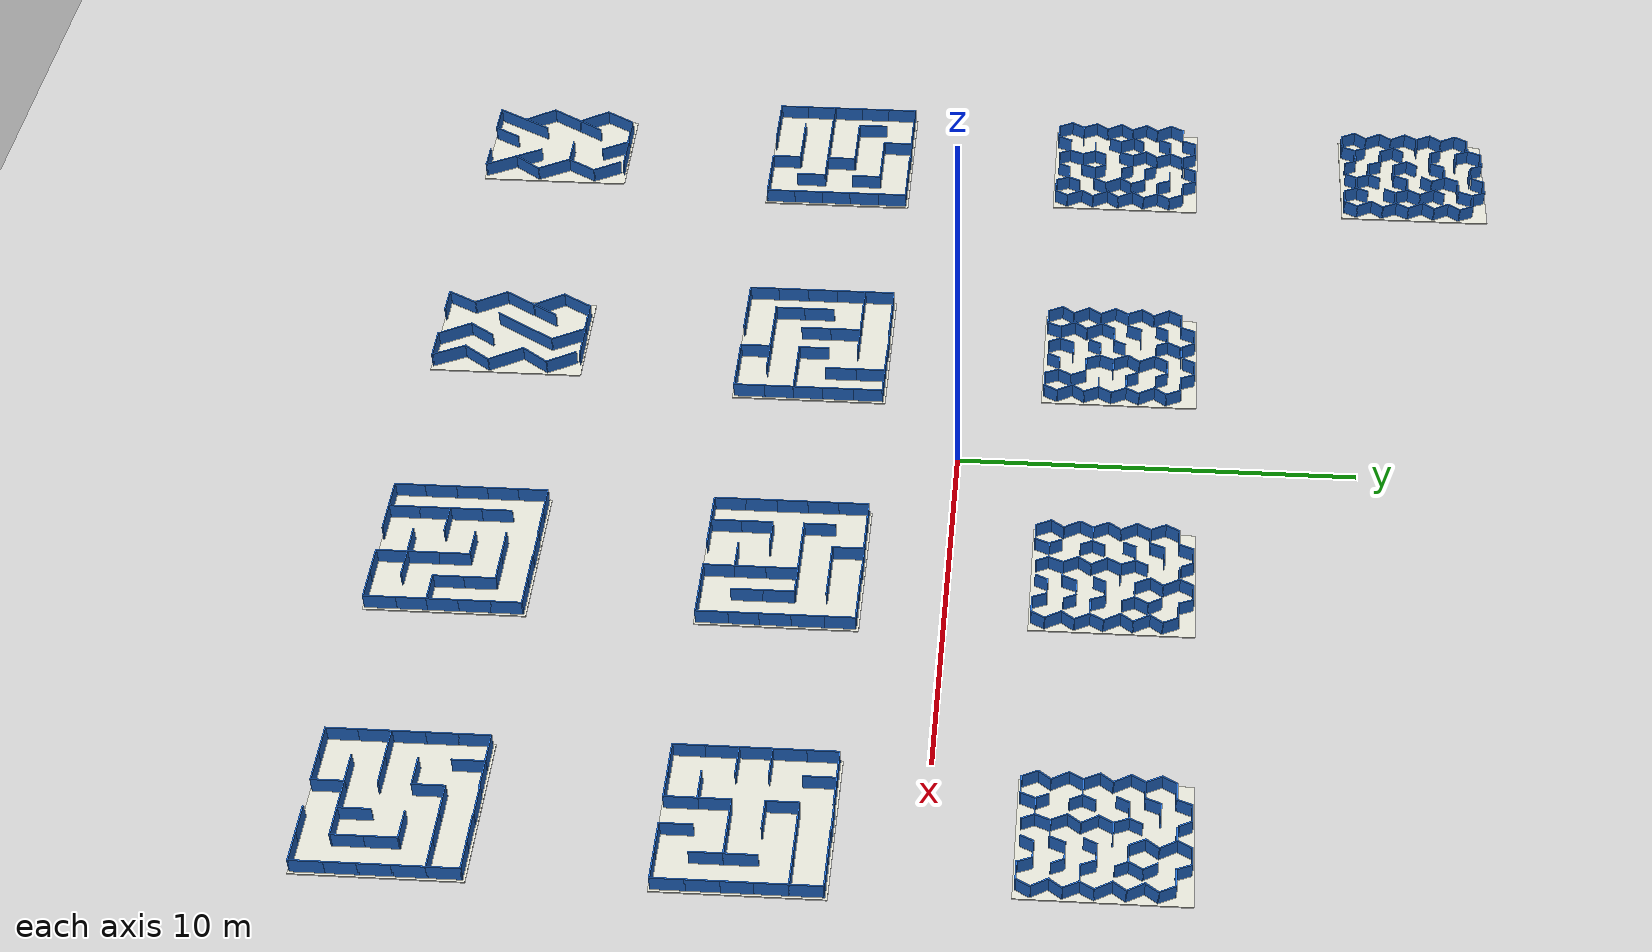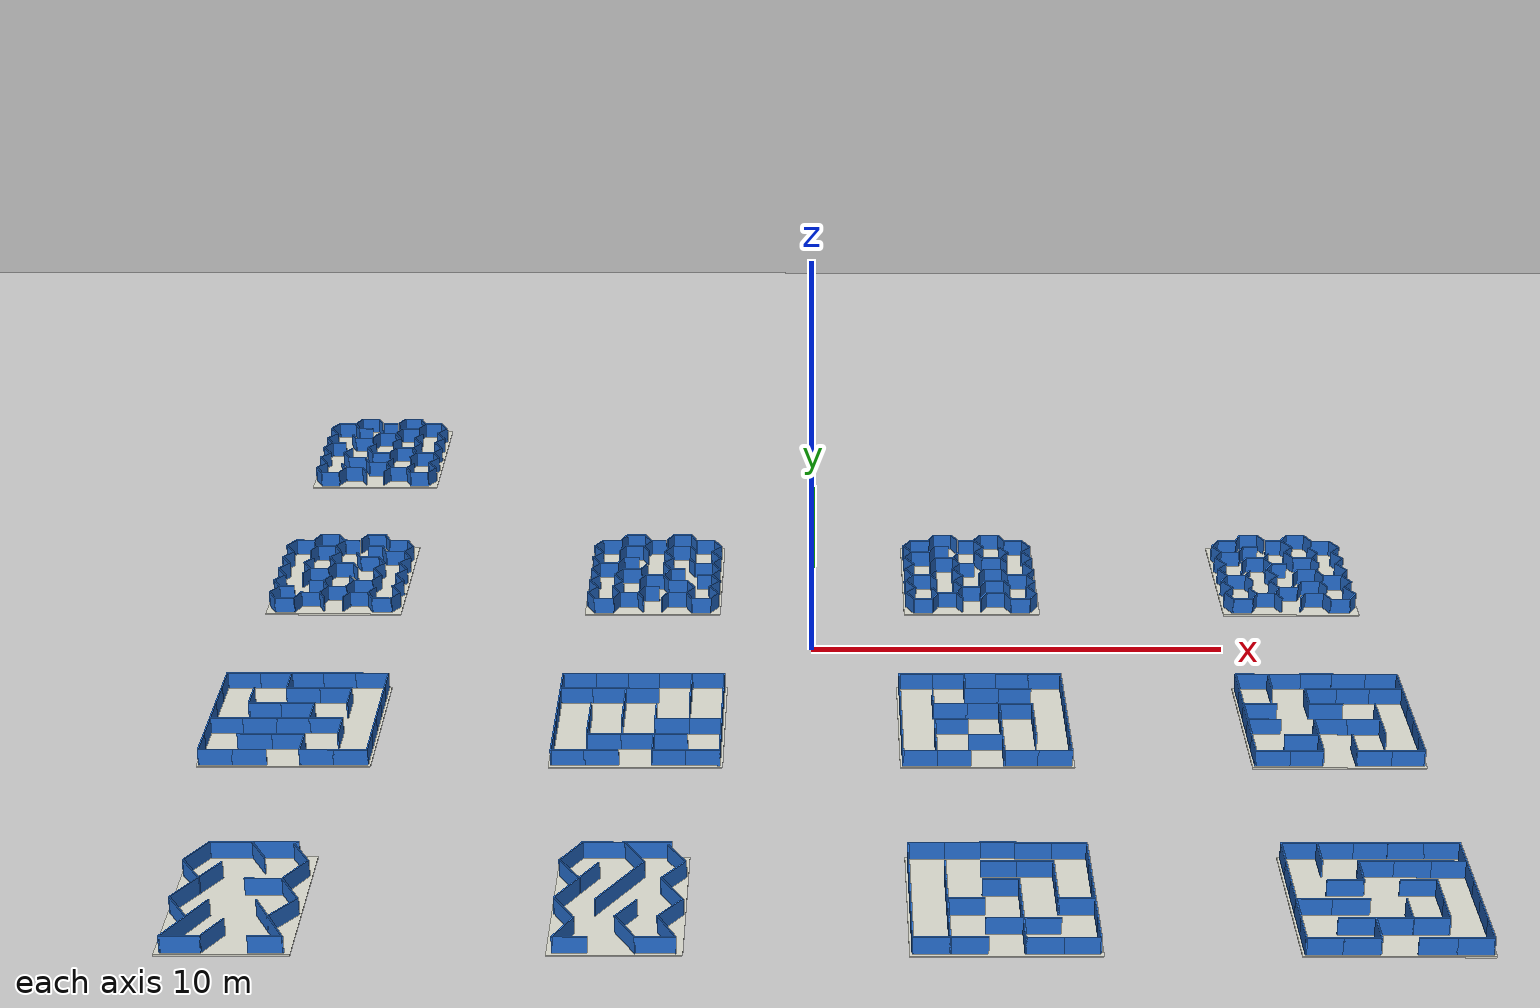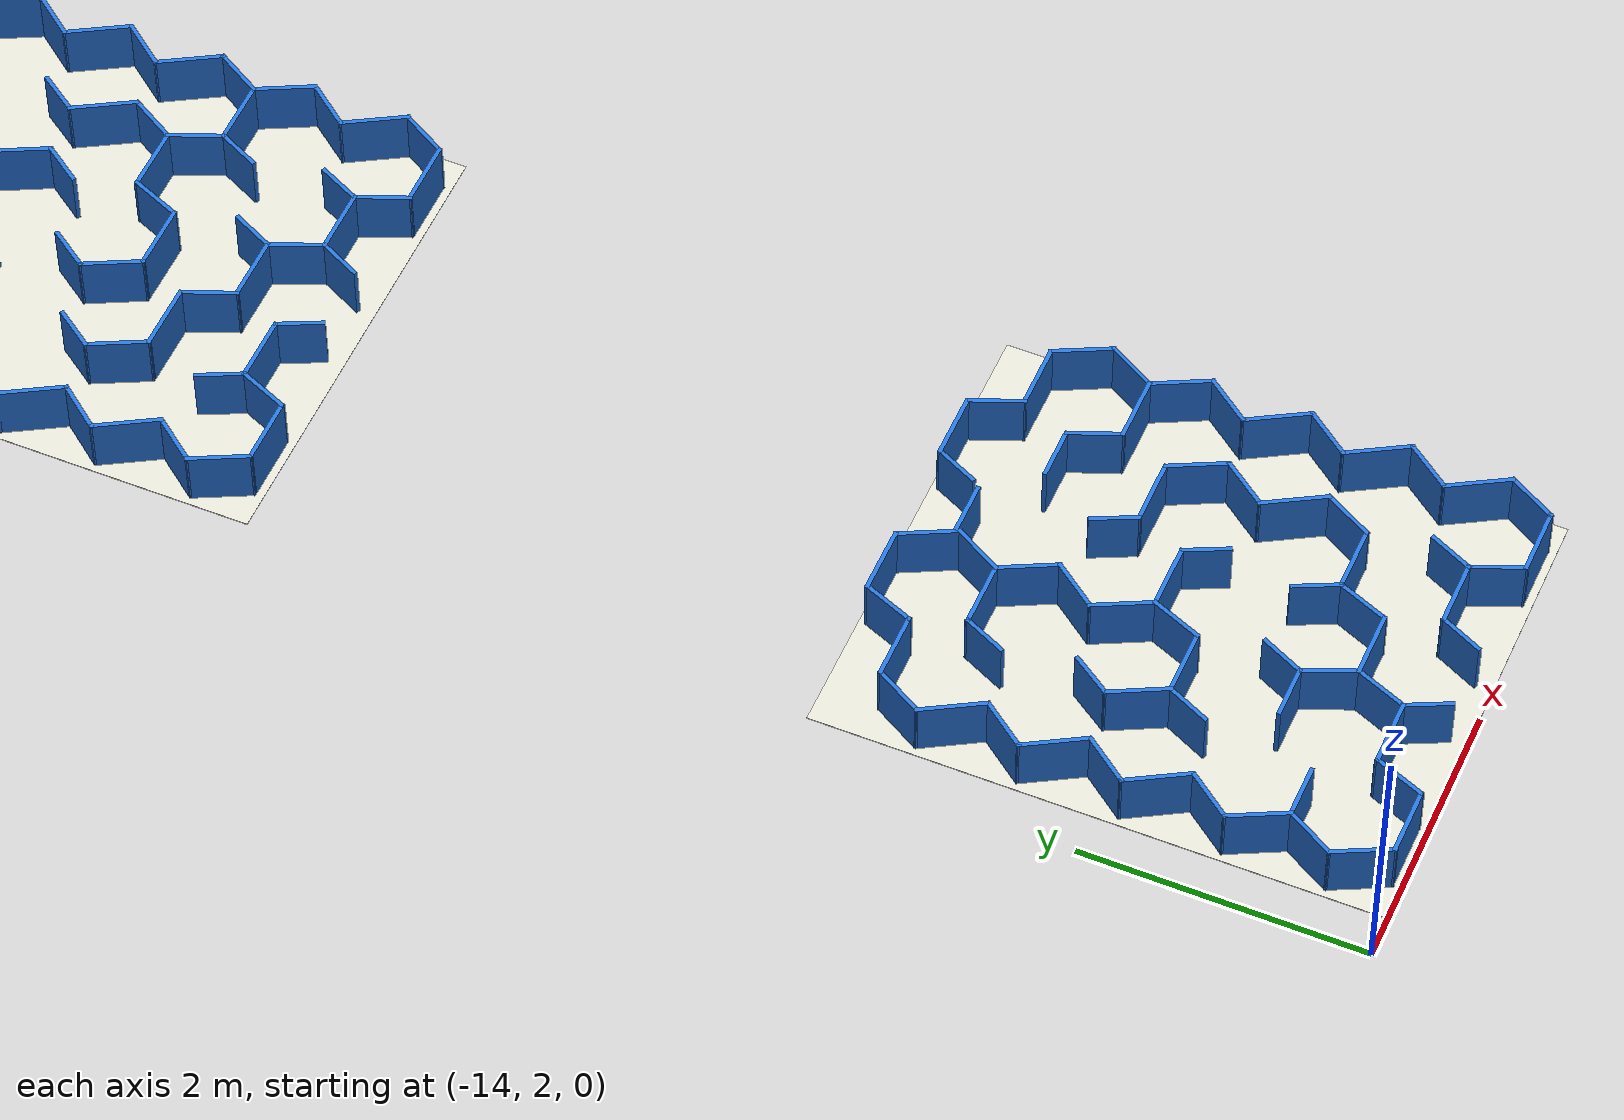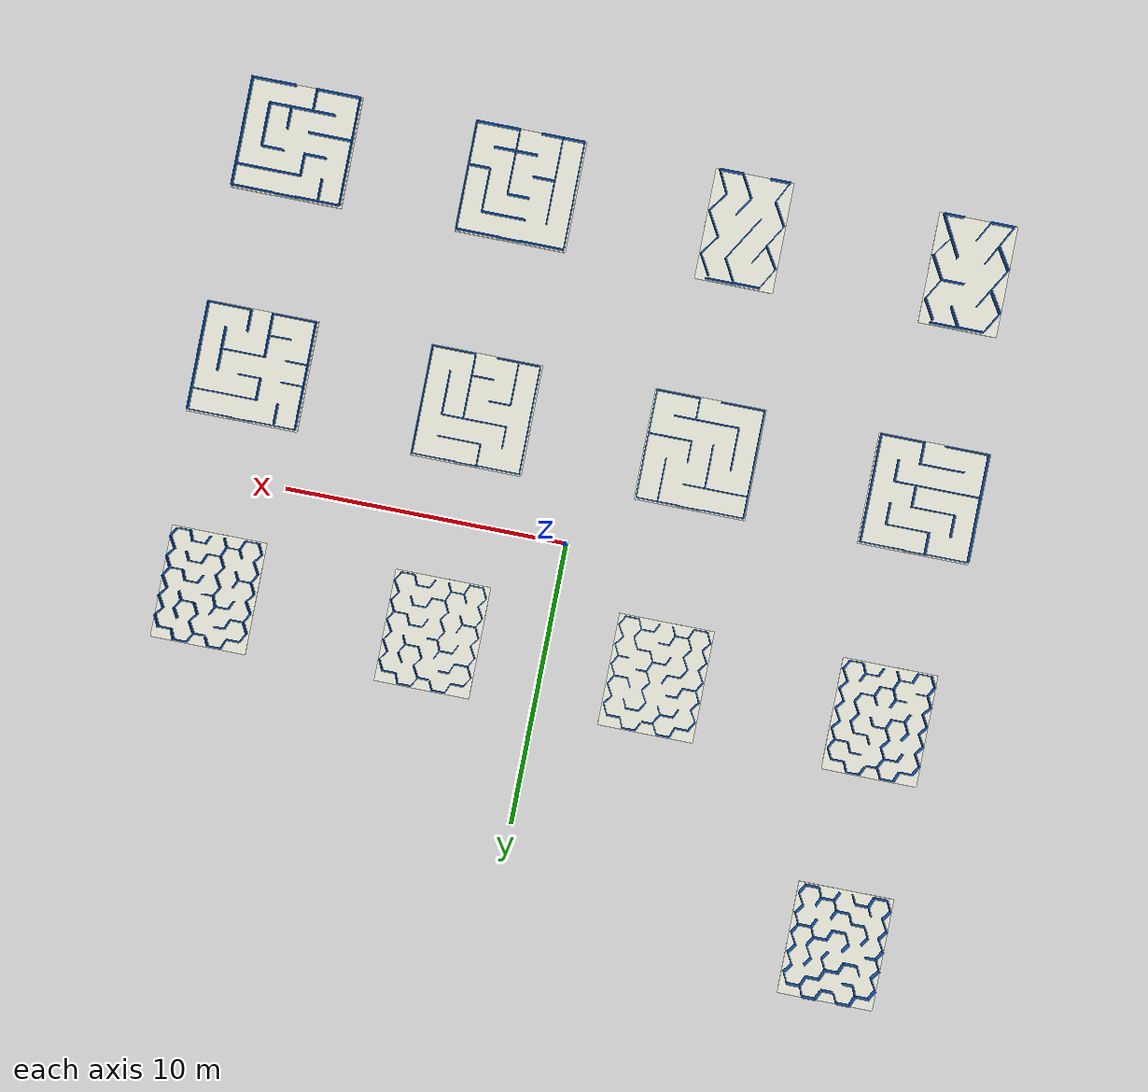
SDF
<?xml version="1.0" ?>
<sdf version="1.10">
<world name="nhom8_maze_multi">
  <physics name="8ms" type="ignored">
    <max_step_size>0.008</max_step_size>
    <real_time_factor>1.0</real_time_factor>
  </physics>
  <plugin filename="gz-sim-physics-system"   name="gz::sim::systems::Physics"/>
  <plugin filename="gz-sim-user-commands-system" name="gz::sim::systems::UserCommands"/>
  <plugin filename="gz-sim-scene-broadcaster-system" name="gz::sim::systems::SceneBroadcaster"/>
  <plugin filename="gz-sim-sensors-system" name="gz::sim::systems::Sensors">
    <render_engine>ogre2</render_engine>
  </plugin>

  <light type="directional" name="sun">
    <cast_shadows>true</cast_shadows>
    <pose>0 0 10 0 0 0</pose>
    <diffuse>1 1 1 1</diffuse>
    <specular>0.5 0.5 0.5 1</specular>
    <attenuation><range>1000</range><constant>0.9</constant>
      <linear>0.01</linear><quadratic>0.001</quadratic></attenuation>
    <direction>-0.5 0.1 -0.9</direction>
  </light>

  <model name="ground_plane">
    <static>true</static>
    <link name="link">
      <collision name="collision">
        <geometry><plane><normal>0 0 1</normal><size>80.0 80.0</size></plane></geometry>
        <surface><friction><ode><mu>40</mu></ode></friction></surface>
      </collision>
      <visual name="visual">
        <geometry><plane><normal>0 0 1</normal><size>80.0 80.0</size></plane></geometry>
        <material>
          <ambient>0.8 0.8 0.8 1</ambient><diffuse>0.8 0.8 0.8 1</diffuse>
          <specular>0.8 0.8 0.8 1</specular>
        </material>
      </visual>
    </link>
  </model>

  <!--  MAZE delta_1 (family delta)                -->
  <!--  walls: 17   wall bbox (local): (-1.3399, -1.9243, 1.3567, 1.9228)   -->
  <!--  openings: entrance=north@(0.495,1.923) hw=0.500  exit=south@(0.053,-1.924) hw=0.470   -->
  <!--  start (local): (0.4782, 1.6497) yaw=-1.8185 rad  -->
  <!--  placement center: (-12.0000, -12.0000)   -->

    <model name="delta_1_wall_000">
      <static>true</static>
      <pose>-12.441500 -10.090300 0.2000 0 0 0.000000</pose>
      <link name="link">
        <collision name="col">
          <geometry><box><size>0.9460 0.0300 0.4000</size></box></geometry>
        </collision>
        <visual name="vis">
          <geometry><box><size>0.9460 0.0300 0.4000</size></box></geometry>
          <material><ambient>0.15 0.45 0.85 1</ambient><diffuse>0.15 0.45 0.85 1</diffuse></material>
        </visual>
      </link>
    </model>

    <model name="delta_1_wall_001">
      <static>true</static>
      <pose>-11.494450 -11.616700 0.2000 0 0 0.000000</pose>
      <link name="link">
        <collision name="col">
          <geometry><box><size>0.8179 0.0300 0.4000</size></box></geometry>
        </collision>
        <visual name="vis">
          <geometry><box><size>0.8179 0.0300 0.4000</size></box></geometry>
          <material><ambient>0.15 0.45 0.85 1</ambient><diffuse>0.15 0.45 0.85 1</diffuse></material>
        </visual>
      </link>
    </model>

    <model name="delta_1_wall_002">
      <static>true</static>
      <pose>-12.841300 -13.911000 0.2000 0 0 0.000000</pose>
      <link name="link">
        <collision name="col">
          <geometry><box><size>0.8626 0.0300 0.4000</size></box></geometry>
        </collision>
        <visual name="vis">
          <geometry><box><size>0.8626 0.0300 0.4000</size></box></geometry>
          <material><ambient>0.15 0.45 0.85 1</ambient><diffuse>0.15 0.45 0.85 1</diffuse></material>
        </visual>
      </link>
    </model>

    <model name="delta_1_wall_003">
      <static>true</static>
      <pose>-11.094650 -13.911000 0.2000 0 0 0.000000</pose>
      <link name="link">
        <collision name="col">
          <geometry><box><size>0.7345 0.0300 0.4000</size></box></geometry>
        </collision>
        <visual name="vis">
          <geometry><box><size>0.7345 0.0300 0.4000</size></box></geometry>
          <material><ambient>0.15 0.45 0.85 1</ambient><diffuse>0.15 0.45 0.85 1</diffuse></material>
        </visual>
      </link>
    </model>

    <model name="delta_1_wall_004">
      <static>true</static>
      <pose>-10.866200 -10.524550 0.2000 0 0 -1.047164</pose>
      <link name="link">
        <collision name="col">
          <geometry><box><size>0.8184 0.0300 0.4000</size></box></geometry>
        </collision>
        <visual name="vis">
          <geometry><box><size>0.8184 0.0300 0.4000</size></box></geometry>
          <material><ambient>0.15 0.45 0.85 1</ambient><diffuse>0.15 0.45 0.85 1</diffuse></material>
        </visual>
      </link>
    </model>

    <model name="delta_1_wall_005">
      <static>true</static>
      <pose>-11.798550 -10.424650 0.2000 0 0 -1.065410</pose>
      <link name="link">
        <collision name="col">
          <geometry><box><size>0.7942 0.0300 0.4000</size></box></geometry>
        </collision>
        <visual name="vis">
          <geometry><box><size>0.7942 0.0300 0.4000</size></box></geometry>
          <material><ambient>0.15 0.45 0.85 1</ambient><diffuse>0.15 0.45 0.85 1</diffuse></material>
        </visual>
      </link>
    </model>

    <model name="delta_1_wall_006">
      <static>true</static>
      <pose>-10.876250 -12.020350 0.2000 0 0 -1.063840</pose>
      <link name="link">
        <collision name="col">
          <geometry><box><size>0.9534 0.0300 0.4000</size></box></geometry>
        </collision>
        <visual name="vis">
          <geometry><box><size>0.9534 0.0300 0.4000</size></box></geometry>
          <material><ambient>0.15 0.45 0.85 1</ambient><diffuse>0.15 0.45 0.85 1</diffuse></material>
        </visual>
      </link>
    </model>

    <model name="delta_1_wall_007">
      <static>true</static>
      <pose>-11.122900 -13.194150 0.2000 0 0 -1.082881</pose>
      <link name="link">
        <collision name="col">
          <geometry><box><size>1.6532 0.0300 0.4000</size></box></geometry>
        </collision>
        <visual name="vis">
          <geometry><box><size>1.6532 0.0300 0.4000</size></box></geometry>
          <material><ambient>0.15 0.45 0.85 1</ambient><diffuse>0.15 0.45 0.85 1</diffuse></material>
        </visual>
      </link>
    </model>

    <model name="delta_1_wall_008">
      <static>true</static>
      <pose>-13.097700 -11.212650 0.2000 0 0 -1.010998</pose>
      <link name="link">
        <collision name="col">
          <geometry><box><size>0.9107 0.0300 0.4000</size></box></geometry>
        </collision>
        <visual name="vis">
          <geometry><box><size>0.9107 0.0300 0.4000</size></box></geometry>
          <material><ambient>0.15 0.45 0.85 1</ambient><diffuse>0.15 0.45 0.85 1</diffuse></material>
        </visual>
      </link>
    </model>

    <model name="delta_1_wall_009">
      <static>true</static>
      <pose>-13.097950 -12.741300 0.2000 0 0 -1.010777</pose>
      <link name="link">
        <collision name="col">
          <geometry><box><size>0.9110 0.0300 0.4000</size></box></geometry>
        </collision>
        <visual name="vis">
          <geometry><box><size>0.9110 0.0300 0.4000</size></box></geometry>
          <material><ambient>0.15 0.45 0.85 1</ambient><diffuse>0.15 0.45 0.85 1</diffuse></material>
        </visual>
      </link>
    </model>

    <model name="delta_1_wall_010">
      <static>true</static>
      <pose>-10.905900 -12.774400 0.2000 0 0 0.944004</pose>
      <link name="link">
        <collision name="col">
          <geometry><box><size>0.8954 0.0300 0.4000</size></box></geometry>
        </collision>
        <visual name="vis">
          <geometry><box><size>0.8954 0.0300 0.4000</size></box></geometry>
          <material><ambient>0.15 0.45 0.85 1</ambient><diffuse>0.15 0.45 0.85 1</diffuse></material>
        </visual>
      </link>
    </model>

    <model name="delta_1_wall_011">
      <static>true</static>
      <pose>-10.884750 -11.241300 0.2000 0 0 1.049310</pose>
      <link name="link">
        <collision name="col">
          <geometry><box><size>0.8959 0.0300 0.4000</size></box></geometry>
        </collision>
        <visual name="vis">
          <geometry><box><size>0.8959 0.0300 0.4000</size></box></geometry>
          <material><ambient>0.15 0.45 0.85 1</ambient><diffuse>0.15 0.45 0.85 1</diffuse></material>
        </visual>
      </link>
    </model>

    <model name="delta_1_wall_012">
      <static>true</static>
      <pose>-12.240150 -13.576000 0.2000 0 0 1.066422</pose>
      <link name="link">
        <collision name="col">
          <geometry><box><size>0.7952 0.0300 0.4000</size></box></geometry>
        </collision>
        <visual name="vis">
          <geometry><box><size>0.7952 0.0300 0.4000</size></box></geometry>
          <material><ambient>0.15 0.45 0.85 1</ambient><diffuse>0.15 0.45 0.85 1</diffuse></material>
        </visual>
      </link>
    </model>

    <model name="delta_1_wall_013">
      <static>true</static>
      <pose>-12.876700 -13.193950 0.2000 0 0 1.082511</pose>
      <link name="link">
        <collision name="col">
          <geometry><box><size>1.6538 0.0300 0.4000</size></box></geometry>
        </collision>
        <visual name="vis">
          <geometry><box><size>1.6538 0.0300 0.4000</size></box></geometry>
          <material><ambient>0.15 0.45 0.85 1</ambient><diffuse>0.15 0.45 0.85 1</diffuse></material>
        </visual>
      </link>
    </model>

    <model name="delta_1_wall_014">
      <static>true</static>
      <pose>-12.913450 -11.657550 0.2000 0 0 1.038568</pose>
      <link name="link">
        <collision name="col">
          <geometry><box><size>1.6792 0.0300 0.4000</size></box></geometry>
        </collision>
        <visual name="vis">
          <geometry><box><size>1.6792 0.0300 0.4000</size></box></geometry>
          <material><ambient>0.15 0.45 0.85 1</ambient><diffuse>0.15 0.45 0.85 1</diffuse></material>
        </visual>
      </link>
    </model>

    <model name="delta_1_wall_015">
      <static>true</static>
      <pose>-13.115550 -10.464900 0.2000 0 0 1.047645</pose>
      <link name="link">
        <collision name="col">
          <geometry><box><size>0.8949 0.0300 0.4000</size></box></geometry>
        </collision>
        <visual name="vis">
          <geometry><box><size>0.8949 0.0300 0.4000</size></box></geometry>
          <material><ambient>0.15 0.45 0.85 1</ambient><diffuse>0.15 0.45 0.85 1</diffuse></material>
        </visual>
      </link>
    </model>

    <model name="delta_1_wall_016">
      <static>true</static>
      <pose>-11.505100 -10.077200 0.2000 0 0 0.000000</pose>
      <link name="link">
        <collision name="col">
          <geometry><box><size>1.0600 0.0300 0.4000</size></box></geometry>
        </collision>
        <visual name="vis">
          <geometry><box><size>1.0600 0.0300 0.4000</size></box></geometry>
          <material><ambient>0.15 0.45 0.85 1</ambient><diffuse>0.15 0.45 0.85 1</diffuse></material>
        </visual>
      </link>
    </model>

    <model name="delta_1_floor">
      <static>true</static>
      <pose>-12.000000 -12.000000 -0.02 0 0 0</pose>
      <link name="link">
        <collision name="col">
          <geometry><box><size>2.7966 3.9471 0.03</size></box></geometry>
        </collision>
        <visual name="vis">
          <geometry><box><size>2.7966 3.9471 0.03</size></box></geometry>
          <material><ambient>0.87 0.87 0.82 1</ambient><diffuse>0.87 0.87 0.82 1</diffuse></material>
        </visual>
      </link>
    </model>

  <!--  MAZE delta_2 (family delta)                -->
  <!--  walls: 18   wall bbox (local): (-1.3396, -1.9244, 1.3565, 1.9228)   -->
  <!--  openings: entrance=north@(0.495,1.923) hw=0.500  exit=south@(-0.049,-1.924) hw=0.470   -->
  <!--  start (local): (0.4785, 1.6496) yaw=-1.8185 rad  -->
  <!--  placement center: (-4.0000, -12.0000)   -->

    <model name="delta_2_wall_000">
      <static>true</static>
      <pose>-4.441500 -10.090300 0.2000 0 0 0.000000</pose>
      <link name="link">
        <collision name="col">
          <geometry><box><size>0.9460 0.0300 0.4000</size></box></geometry>
        </collision>
        <visual name="vis">
          <geometry><box><size>0.9460 0.0300 0.4000</size></box></geometry>
          <material><ambient>0.15 0.45 0.85 1</ambient><diffuse>0.15 0.45 0.85 1</diffuse></material>
        </visual>
      </link>
    </model>

    <model name="delta_2_wall_001">
      <static>true</static>
      <pose>-4.905350 -13.911000 0.2000 0 0 0.000000</pose>
      <link name="link">
        <collision name="col">
          <geometry><box><size>0.7345 0.0300 0.4000</size></box></geometry>
        </collision>
        <visual name="vis">
          <geometry><box><size>0.7345 0.0300 0.4000</size></box></geometry>
          <material><ambient>0.15 0.45 0.85 1</ambient><diffuse>0.15 0.45 0.85 1</diffuse></material>
        </visual>
      </link>
    </model>

    <model name="delta_2_wall_002">
      <static>true</static>
      <pose>-3.158700 -13.911000 0.2000 0 0 0.000000</pose>
      <link name="link">
        <collision name="col">
          <geometry><box><size>0.8626 0.0300 0.4000</size></box></geometry>
        </collision>
        <visual name="vis">
          <geometry><box><size>0.8626 0.0300 0.4000</size></box></geometry>
          <material><ambient>0.15 0.45 0.85 1</ambient><diffuse>0.15 0.45 0.85 1</diffuse></material>
        </visual>
      </link>
    </model>

    <model name="delta_2_wall_003">
      <static>true</static>
      <pose>-2.857750 -10.539200 0.2000 0 0 -1.047182</pose>
      <link name="link">
        <collision name="col">
          <geometry><box><size>0.8522 0.0300 0.4000</size></box></geometry>
        </collision>
        <visual name="vis">
          <geometry><box><size>0.8522 0.0300 0.4000</size></box></geometry>
          <material><ambient>0.15 0.45 0.85 1</ambient><diffuse>0.15 0.45 0.85 1</diffuse></material>
        </visual>
      </link>
    </model>

    <model name="delta_2_wall_004">
      <static>true</static>
      <pose>-3.759150 -10.492700 0.2000 0 0 -1.062197</pose>
      <link name="link">
        <collision name="col">
          <geometry><box><size>0.9514 0.0300 0.4000</size></box></geometry>
        </collision>
        <visual name="vis">
          <geometry><box><size>0.9514 0.0300 0.4000</size></box></geometry>
          <material><ambient>0.15 0.45 0.85 1</ambient><diffuse>0.15 0.45 0.85 1</diffuse></material>
        </visual>
      </link>
    </model>

    <model name="delta_2_wall_005">
      <static>true</static>
      <pose>-2.896850 -12.000400 0.2000 0 0 -1.047181</pose>
      <link name="link">
        <collision name="col">
          <geometry><box><size>1.0074 0.0300 0.4000</size></box></geometry>
        </collision>
        <visual name="vis">
          <geometry><box><size>1.0074 0.0300 0.4000</size></box></geometry>
          <material><ambient>0.15 0.45 0.85 1</ambient><diffuse>0.15 0.45 0.85 1</diffuse></material>
        </visual>
      </link>
    </model>

    <model name="delta_2_wall_006">
      <static>true</static>
      <pose>-2.942050 -13.507150 0.2000 0 0 -1.111713</pose>
      <link name="link">
        <collision name="col">
          <geometry><box><size>0.9309 0.0300 0.4000</size></box></geometry>
        </collision>
        <visual name="vis">
          <geometry><box><size>0.9309 0.0300 0.4000</size></box></geometry>
          <material><ambient>0.15 0.45 0.85 1</ambient><diffuse>0.15 0.45 0.85 1</diffuse></material>
        </visual>
      </link>
    </model>

    <model name="delta_2_wall_007">
      <static>true</static>
      <pose>-5.097150 -11.212150 0.2000 0 0 -1.011161</pose>
      <link name="link">
        <collision name="col">
          <geometry><box><size>0.9104 0.0300 0.4000</size></box></geometry>
        </collision>
        <visual name="vis">
          <geometry><box><size>0.9104 0.0300 0.4000</size></box></geometry>
          <material><ambient>0.15 0.45 0.85 1</ambient><diffuse>0.15 0.45 0.85 1</diffuse></material>
        </visual>
      </link>
    </model>

    <model name="delta_2_wall_008">
      <static>true</static>
      <pose>-3.799050 -13.507750 0.2000 0 0 -1.063616</pose>
      <link name="link">
        <collision name="col">
          <geometry><box><size>0.9526 0.0300 0.4000</size></box></geometry>
        </collision>
        <visual name="vis">
          <geometry><box><size>0.9526 0.0300 0.4000</size></box></geometry>
          <material><ambient>0.15 0.45 0.85 1</ambient><diffuse>0.15 0.45 0.85 1</diffuse></material>
        </visual>
      </link>
    </model>

    <model name="delta_2_wall_009">
      <static>true</static>
      <pose>-5.103450 -12.763950 0.2000 0 0 -1.047197</pose>
      <link name="link">
        <collision name="col">
          <geometry><box><size>0.9442 0.0300 0.4000</size></box></geometry>
        </collision>
        <visual name="vis">
          <geometry><box><size>0.9442 0.0300 0.4000</size></box></geometry>
          <material><ambient>0.15 0.45 0.85 1</ambient><diffuse>0.15 0.45 0.85 1</diffuse></material>
        </visual>
      </link>
    </model>

    <model name="delta_2_wall_010">
      <static>true</static>
      <pose>-2.897050 -12.763500 0.2000 0 0 0.946942</pose>
      <link name="link">
        <collision name="col">
          <geometry><box><size>0.8674 0.0300 0.4000</size></box></geometry>
        </collision>
        <visual name="vis">
          <geometry><box><size>0.8674 0.0300 0.4000</size></box></geometry>
          <material><ambient>0.15 0.45 0.85 1</ambient><diffuse>0.15 0.45 0.85 1</diffuse></material>
        </visual>
      </link>
    </model>

    <model name="delta_2_wall_011">
      <static>true</static>
      <pose>-2.896700 -11.236150 0.2000 0 0 0.948768</pose>
      <link name="link">
        <collision name="col">
          <geometry><box><size>0.8691 0.0300 0.4000</size></box></geometry>
        </collision>
        <visual name="vis">
          <geometry><box><size>0.8691 0.0300 0.4000</size></box></geometry>
          <material><ambient>0.15 0.45 0.85 1</ambient><diffuse>0.15 0.45 0.85 1</diffuse></material>
        </visual>
      </link>
    </model>

    <model name="delta_2_wall_012">
      <static>true</static>
      <pose>-3.817950 -12.790800 0.2000 0 0 0.991507</pose>
      <link name="link">
        <collision name="col">
          <geometry><box><size>0.7798 0.0300 0.4000</size></box></geometry>
        </collision>
        <visual name="vis">
          <geometry><box><size>0.7798 0.0300 0.4000</size></box></geometry>
          <material><ambient>0.15 0.45 0.85 1</ambient><diffuse>0.15 0.45 0.85 1</diffuse></material>
        </visual>
      </link>
    </model>

    <model name="delta_2_wall_013">
      <static>true</static>
      <pose>-4.005450 -11.668350 0.2000 0 0 1.024022</pose>
      <link name="link">
        <collision name="col">
          <geometry><box><size>1.8404 0.0300 0.4000</size></box></geometry>
        </collision>
        <visual name="vis">
          <geometry><box><size>1.8404 0.0300 0.4000</size></box></geometry>
          <material><ambient>0.15 0.45 0.85 1</ambient><diffuse>0.15 0.45 0.85 1</diffuse></material>
        </visual>
      </link>
    </model>

    <model name="delta_2_wall_014">
      <static>true</static>
      <pose>-5.066250 -13.535400 0.2000 0 0 1.099670</pose>
      <link name="link">
        <collision name="col">
          <geometry><box><size>0.8731 0.0300 0.4000</size></box></geometry>
        </collision>
        <visual name="vis">
          <geometry><box><size>0.8731 0.0300 0.4000</size></box></geometry>
          <material><ambient>0.15 0.45 0.85 1</ambient><diffuse>0.15 0.45 0.85 1</diffuse></material>
        </visual>
      </link>
    </model>

    <model name="delta_2_wall_015">
      <static>true</static>
      <pose>-4.913500 -11.657600 0.2000 0 0 1.038547</pose>
      <link name="link">
        <collision name="col">
          <geometry><box><size>1.6793 0.0300 0.4000</size></box></geometry>
        </collision>
        <visual name="vis">
          <geometry><box><size>1.6793 0.0300 0.4000</size></box></geometry>
          <material><ambient>0.15 0.45 0.85 1</ambient><diffuse>0.15 0.45 0.85 1</diffuse></material>
        </visual>
      </link>
    </model>

    <model name="delta_2_wall_016">
      <static>true</static>
      <pose>-5.115150 -10.464750 0.2000 0 0 1.048252</pose>
      <link name="link">
        <collision name="col">
          <geometry><box><size>0.8942 0.0300 0.4000</size></box></geometry>
        </collision>
        <visual name="vis">
          <geometry><box><size>0.8942 0.0300 0.4000</size></box></geometry>
          <material><ambient>0.15 0.45 0.85 1</ambient><diffuse>0.15 0.45 0.85 1</diffuse></material>
        </visual>
      </link>
    </model>

    <model name="delta_2_wall_017">
      <static>true</static>
      <pose>-3.505100 -10.077200 0.2000 0 0 0.000000</pose>
      <link name="link">
        <collision name="col">
          <geometry><box><size>1.0600 0.0300 0.4000</size></box></geometry>
        </collision>
        <visual name="vis">
          <geometry><box><size>1.0600 0.0300 0.4000</size></box></geometry>
          <material><ambient>0.15 0.45 0.85 1</ambient><diffuse>0.15 0.45 0.85 1</diffuse></material>
        </visual>
      </link>
    </model>

    <model name="delta_2_floor">
      <static>true</static>
      <pose>-4.000000 -12.000000 -0.02 0 0 0</pose>
      <link name="link">
        <collision name="col">
          <geometry><box><size>2.7961 3.9472 0.03</size></box></geometry>
        </collision>
        <visual name="vis">
          <geometry><box><size>2.7961 3.9472 0.03</size></box></geometry>
          <material><ambient>0.87 0.87 0.82 1</ambient><diffuse>0.87 0.87 0.82 1</diffuse></material>
        </visual>
      </link>
    </model>

  <!--  MAZE ortho_1 (family ortho)                -->
  <!--  walls: 35   wall bbox (local): (-1.9326, -1.9326, 1.9326, 1.9326)   -->
  <!--  openings: entrance=north@(0.003,1.933) hw=0.367  exit=south@(0.003,-1.933) hw=0.367   -->
  <!--  start (local): (-0.0076, 1.5924) yaw=-1.5725 rad  -->
  <!--  placement center: (4.0000, -12.0000)   -->

    <model name="ortho_1_wall_000">
      <static>true</static>
      <pose>2.082400 -10.465950 0.2000 0 0 1.570796</pose>
      <link name="link">
        <collision name="col">
          <geometry><box><size>0.7971 0.0300 0.4000</size></box></geometry>
        </collision>
        <visual name="vis">
          <geometry><box><size>0.7971 0.0300 0.4000</size></box></geometry>
          <material><ambient>0.15 0.45 0.85 1</ambient><diffuse>0.15 0.45 0.85 1</diffuse></material>
        </visual>
      </link>
    </model>

    <model name="ortho_1_wall_001">
      <static>true</static>
      <pose>2.082400 -11.233000 0.2000 0 0 1.570796</pose>
      <link name="link">
        <collision name="col">
          <geometry><box><size>0.7970 0.0300 0.4000</size></box></geometry>
        </collision>
        <visual name="vis">
          <geometry><box><size>0.7970 0.0300 0.4000</size></box></geometry>
          <material><ambient>0.15 0.45 0.85 1</ambient><diffuse>0.15 0.45 0.85 1</diffuse></material>
        </visual>
      </link>
    </model>

    <model name="ortho_1_wall_002">
      <static>true</static>
      <pose>2.082400 -12.000000 0.2000 0 0 1.570796</pose>
      <link name="link">
        <collision name="col">
          <geometry><box><size>0.7970 0.0300 0.4000</size></box></geometry>
        </collision>
        <visual name="vis">
          <geometry><box><size>0.7970 0.0300 0.4000</size></box></geometry>
          <material><ambient>0.15 0.45 0.85 1</ambient><diffuse>0.15 0.45 0.85 1</diffuse></material>
        </visual>
      </link>
    </model>

    <model name="ortho_1_wall_003">
      <static>true</static>
      <pose>2.082400 -12.767000 0.2000 0 0 1.570796</pose>
      <link name="link">
        <collision name="col">
          <geometry><box><size>0.7970 0.0300 0.4000</size></box></geometry>
        </collision>
        <visual name="vis">
          <geometry><box><size>0.7970 0.0300 0.4000</size></box></geometry>
          <material><ambient>0.15 0.45 0.85 1</ambient><diffuse>0.15 0.45 0.85 1</diffuse></material>
        </visual>
      </link>
    </model>

    <model name="ortho_1_wall_004">
      <static>true</static>
      <pose>2.082400 -13.534050 0.2000 0 0 1.570796</pose>
      <link name="link">
        <collision name="col">
          <geometry><box><size>0.7971 0.0300 0.4000</size></box></geometry>
        </collision>
        <visual name="vis">
          <geometry><box><size>0.7971 0.0300 0.4000</size></box></geometry>
          <material><ambient>0.15 0.45 0.85 1</ambient><diffuse>0.15 0.45 0.85 1</diffuse></material>
        </visual>
      </link>
    </model>

    <model name="ortho_1_wall_005">
      <static>true</static>
      <pose>2.849500 -11.233000 0.2000 0 0 1.570796</pose>
      <link name="link">
        <collision name="col">
          <geometry><box><size>0.7970 0.0300 0.4000</size></box></geometry>
        </collision>
        <visual name="vis">
          <geometry><box><size>0.7970 0.0300 0.4000</size></box></geometry>
          <material><ambient>0.15 0.45 0.85 1</ambient><diffuse>0.15 0.45 0.85 1</diffuse></material>
        </visual>
      </link>
    </model>

    <model name="ortho_1_wall_006">
      <static>true</static>
      <pose>2.849500 -12.000000 0.2000 0 0 1.570796</pose>
      <link name="link">
        <collision name="col">
          <geometry><box><size>0.7970 0.0300 0.4000</size></box></geometry>
        </collision>
        <visual name="vis">
          <geometry><box><size>0.7970 0.0300 0.4000</size></box></geometry>
          <material><ambient>0.15 0.45 0.85 1</ambient><diffuse>0.15 0.45 0.85 1</diffuse></material>
        </visual>
      </link>
    </model>

    <model name="ortho_1_wall_007">
      <static>true</static>
      <pose>2.849500 -12.767000 0.2000 0 0 1.570796</pose>
      <link name="link">
        <collision name="col">
          <geometry><box><size>0.7970 0.0300 0.4000</size></box></geometry>
        </collision>
        <visual name="vis">
          <geometry><box><size>0.7970 0.0300 0.4000</size></box></geometry>
          <material><ambient>0.15 0.45 0.85 1</ambient><diffuse>0.15 0.45 0.85 1</diffuse></material>
        </visual>
      </link>
    </model>

    <model name="ortho_1_wall_008">
      <static>true</static>
      <pose>2.849500 -13.534050 0.2000 0 0 1.570796</pose>
      <link name="link">
        <collision name="col">
          <geometry><box><size>0.7971 0.0300 0.4000</size></box></geometry>
        </collision>
        <visual name="vis">
          <geometry><box><size>0.7971 0.0300 0.4000</size></box></geometry>
          <material><ambient>0.15 0.45 0.85 1</ambient><diffuse>0.15 0.45 0.85 1</diffuse></material>
        </visual>
      </link>
    </model>

    <model name="ortho_1_wall_009">
      <static>true</static>
      <pose>4.383500 -12.000000 0.2000 0 0 1.570796</pose>
      <link name="link">
        <collision name="col">
          <geometry><box><size>0.7970 0.0300 0.4000</size></box></geometry>
        </collision>
        <visual name="vis">
          <geometry><box><size>0.7970 0.0300 0.4000</size></box></geometry>
          <material><ambient>0.15 0.45 0.85 1</ambient><diffuse>0.15 0.45 0.85 1</diffuse></material>
        </visual>
      </link>
    </model>

    <model name="ortho_1_wall_010">
      <static>true</static>
      <pose>4.383500 -12.767000 0.2000 0 0 1.570796</pose>
      <link name="link">
        <collision name="col">
          <geometry><box><size>0.7970 0.0300 0.4000</size></box></geometry>
        </collision>
        <visual name="vis">
          <geometry><box><size>0.7970 0.0300 0.4000</size></box></geometry>
          <material><ambient>0.15 0.45 0.85 1</ambient><diffuse>0.15 0.45 0.85 1</diffuse></material>
        </visual>
      </link>
    </model>

    <model name="ortho_1_wall_011">
      <static>true</static>
      <pose>4.383500 -13.534050 0.2000 0 0 1.570796</pose>
      <link name="link">
        <collision name="col">
          <geometry><box><size>0.7971 0.0300 0.4000</size></box></geometry>
        </collision>
        <visual name="vis">
          <geometry><box><size>0.7971 0.0300 0.4000</size></box></geometry>
          <material><ambient>0.15 0.45 0.85 1</ambient><diffuse>0.15 0.45 0.85 1</diffuse></material>
        </visual>
      </link>
    </model>

    <model name="ortho_1_wall_012">
      <static>true</static>
      <pose>5.150500 -11.233000 0.2000 0 0 1.570796</pose>
      <link name="link">
        <collision name="col">
          <geometry><box><size>0.7970 0.0300 0.4000</size></box></geometry>
        </collision>
        <visual name="vis">
          <geometry><box><size>0.7970 0.0300 0.4000</size></box></geometry>
          <material><ambient>0.15 0.45 0.85 1</ambient><diffuse>0.15 0.45 0.85 1</diffuse></material>
        </visual>
      </link>
    </model>

    <model name="ortho_1_wall_013">
      <static>true</static>
      <pose>5.150500 -12.000000 0.2000 0 0 1.570796</pose>
      <link name="link">
        <collision name="col">
          <geometry><box><size>0.7970 0.0300 0.4000</size></box></geometry>
        </collision>
        <visual name="vis">
          <geometry><box><size>0.7970 0.0300 0.4000</size></box></geometry>
          <material><ambient>0.15 0.45 0.85 1</ambient><diffuse>0.15 0.45 0.85 1</diffuse></material>
        </visual>
      </link>
    </model>

    <model name="ortho_1_wall_014">
      <static>true</static>
      <pose>5.917600 -10.465950 0.2000 0 0 1.570796</pose>
      <link name="link">
        <collision name="col">
          <geometry><box><size>0.7971 0.0300 0.4000</size></box></geometry>
        </collision>
        <visual name="vis">
          <geometry><box><size>0.7971 0.0300 0.4000</size></box></geometry>
          <material><ambient>0.15 0.45 0.85 1</ambient><diffuse>0.15 0.45 0.85 1</diffuse></material>
        </visual>
      </link>
    </model>

    <model name="ortho_1_wall_015">
      <static>true</static>
      <pose>5.917600 -11.233000 0.2000 0 0 1.570796</pose>
      <link name="link">
        <collision name="col">
          <geometry><box><size>0.7970 0.0300 0.4000</size></box></geometry>
        </collision>
        <visual name="vis">
          <geometry><box><size>0.7970 0.0300 0.4000</size></box></geometry>
          <material><ambient>0.15 0.45 0.85 1</ambient><diffuse>0.15 0.45 0.85 1</diffuse></material>
        </visual>
      </link>
    </model>

    <model name="ortho_1_wall_016">
      <static>true</static>
      <pose>5.917600 -12.000000 0.2000 0 0 1.570796</pose>
      <link name="link">
        <collision name="col">
          <geometry><box><size>0.7970 0.0300 0.4000</size></box></geometry>
        </collision>
        <visual name="vis">
          <geometry><box><size>0.7970 0.0300 0.4000</size></box></geometry>
          <material><ambient>0.15 0.45 0.85 1</ambient><diffuse>0.15 0.45 0.85 1</diffuse></material>
        </visual>
      </link>
    </model>

    <model name="ortho_1_wall_017">
      <static>true</static>
      <pose>5.917600 -12.767000 0.2000 0 0 1.570796</pose>
      <link name="link">
        <collision name="col">
          <geometry><box><size>0.7970 0.0300 0.4000</size></box></geometry>
        </collision>
        <visual name="vis">
          <geometry><box><size>0.7970 0.0300 0.4000</size></box></geometry>
          <material><ambient>0.15 0.45 0.85 1</ambient><diffuse>0.15 0.45 0.85 1</diffuse></material>
        </visual>
      </link>
    </model>

    <model name="ortho_1_wall_018">
      <static>true</static>
      <pose>5.917600 -13.534050 0.2000 0 0 1.570796</pose>
      <link name="link">
        <collision name="col">
          <geometry><box><size>0.7971 0.0300 0.4000</size></box></geometry>
        </collision>
        <visual name="vis">
          <geometry><box><size>0.7971 0.0300 0.4000</size></box></geometry>
          <material><ambient>0.15 0.45 0.85 1</ambient><diffuse>0.15 0.45 0.85 1</diffuse></material>
        </visual>
      </link>
    </model>

    <model name="ortho_1_wall_019">
      <static>true</static>
      <pose>2.465950 -10.082400 0.2000 0 0 0.000000</pose>
      <link name="link">
        <collision name="col">
          <geometry><box><size>0.7971 0.0300 0.4000</size></box></geometry>
        </collision>
        <visual name="vis">
          <geometry><box><size>0.7971 0.0300 0.4000</size></box></geometry>
          <material><ambient>0.15 0.45 0.85 1</ambient><diffuse>0.15 0.45 0.85 1</diffuse></material>
        </visual>
      </link>
    </model>

    <model name="ortho_1_wall_020">
      <static>true</static>
      <pose>3.233000 -10.082400 0.2000 0 0 0.000000</pose>
      <link name="link">
        <collision name="col">
          <geometry><box><size>0.7970 0.0300 0.4000</size></box></geometry>
        </collision>
        <visual name="vis">
          <geometry><box><size>0.7970 0.0300 0.4000</size></box></geometry>
          <material><ambient>0.15 0.45 0.85 1</ambient><diffuse>0.15 0.45 0.85 1</diffuse></material>
        </visual>
      </link>
    </model>

    <model name="ortho_1_wall_021">
      <static>true</static>
      <pose>4.767000 -10.082400 0.2000 0 0 0.000000</pose>
      <link name="link">
        <collision name="col">
          <geometry><box><size>0.7970 0.0300 0.4000</size></box></geometry>
        </collision>
        <visual name="vis">
          <geometry><box><size>0.7970 0.0300 0.4000</size></box></geometry>
          <material><ambient>0.15 0.45 0.85 1</ambient><diffuse>0.15 0.45 0.85 1</diffuse></material>
        </visual>
      </link>
    </model>

    <model name="ortho_1_wall_022">
      <static>true</static>
      <pose>5.534050 -10.082400 0.2000 0 0 0.000000</pose>
      <link name="link">
        <collision name="col">
          <geometry><box><size>0.7971 0.0300 0.4000</size></box></geometry>
        </collision>
        <visual name="vis">
          <geometry><box><size>0.7971 0.0300 0.4000</size></box></geometry>
          <material><ambient>0.15 0.45 0.85 1</ambient><diffuse>0.15 0.45 0.85 1</diffuse></material>
        </visual>
      </link>
    </model>

    <model name="ortho_1_wall_023">
      <static>true</static>
      <pose>4.000000 -10.849500 0.2000 0 0 0.000000</pose>
      <link name="link">
        <collision name="col">
          <geometry><box><size>0.7970 0.0300 0.4000</size></box></geometry>
        </collision>
        <visual name="vis">
          <geometry><box><size>0.7970 0.0300 0.4000</size></box></geometry>
          <material><ambient>0.15 0.45 0.85 1</ambient><diffuse>0.15 0.45 0.85 1</diffuse></material>
        </visual>
      </link>
    </model>

    <model name="ortho_1_wall_024">
      <static>true</static>
      <pose>4.767000 -10.849500 0.2000 0 0 0.000000</pose>
      <link name="link">
        <collision name="col">
          <geometry><box><size>0.7970 0.0300 0.4000</size></box></geometry>
        </collision>
        <visual name="vis">
          <geometry><box><size>0.7970 0.0300 0.4000</size></box></geometry>
          <material><ambient>0.15 0.45 0.85 1</ambient><diffuse>0.15 0.45 0.85 1</diffuse></material>
        </visual>
      </link>
    </model>

    <model name="ortho_1_wall_025">
      <static>true</static>
      <pose>4.000000 -11.616500 0.2000 0 0 0.000000</pose>
      <link name="link">
        <collision name="col">
          <geometry><box><size>0.7970 0.0300 0.4000</size></box></geometry>
        </collision>
        <visual name="vis">
          <geometry><box><size>0.7970 0.0300 0.4000</size></box></geometry>
          <material><ambient>0.15 0.45 0.85 1</ambient><diffuse>0.15 0.45 0.85 1</diffuse></material>
        </visual>
      </link>
    </model>

    <model name="ortho_1_wall_026">
      <static>true</static>
      <pose>3.233000 -12.383500 0.2000 0 0 0.000000</pose>
      <link name="link">
        <collision name="col">
          <geometry><box><size>0.7970 0.0300 0.4000</size></box></geometry>
        </collision>
        <visual name="vis">
          <geometry><box><size>0.7970 0.0300 0.4000</size></box></geometry>
          <material><ambient>0.15 0.45 0.85 1</ambient><diffuse>0.15 0.45 0.85 1</diffuse></material>
        </visual>
      </link>
    </model>

    <model name="ortho_1_wall_027">
      <static>true</static>
      <pose>5.534050 -12.383500 0.2000 0 0 0.000000</pose>
      <link name="link">
        <collision name="col">
          <geometry><box><size>0.7971 0.0300 0.4000</size></box></geometry>
        </collision>
        <visual name="vis">
          <geometry><box><size>0.7971 0.0300 0.4000</size></box></geometry>
          <material><ambient>0.15 0.45 0.85 1</ambient><diffuse>0.15 0.45 0.85 1</diffuse></material>
        </visual>
      </link>
    </model>

    <model name="ortho_1_wall_028">
      <static>true</static>
      <pose>4.000000 -13.150500 0.2000 0 0 0.000000</pose>
      <link name="link">
        <collision name="col">
          <geometry><box><size>0.7970 0.0300 0.4000</size></box></geometry>
        </collision>
        <visual name="vis">
          <geometry><box><size>0.7970 0.0300 0.4000</size></box></geometry>
          <material><ambient>0.15 0.45 0.85 1</ambient><diffuse>0.15 0.45 0.85 1</diffuse></material>
        </visual>
      </link>
    </model>

    <model name="ortho_1_wall_029">
      <static>true</static>
      <pose>4.767000 -13.150500 0.2000 0 0 0.000000</pose>
      <link name="link">
        <collision name="col">
          <geometry><box><size>0.7970 0.0300 0.4000</size></box></geometry>
        </collision>
        <visual name="vis">
          <geometry><box><size>0.7970 0.0300 0.4000</size></box></geometry>
          <material><ambient>0.15 0.45 0.85 1</ambient><diffuse>0.15 0.45 0.85 1</diffuse></material>
        </visual>
      </link>
    </model>

    <model name="ortho_1_wall_030">
      <static>true</static>
      <pose>2.465950 -13.917600 0.2000 0 0 0.000000</pose>
      <link name="link">
        <collision name="col">
          <geometry><box><size>0.7971 0.0300 0.4000</size></box></geometry>
        </collision>
        <visual name="vis">
          <geometry><box><size>0.7971 0.0300 0.4000</size></box></geometry>
          <material><ambient>0.15 0.45 0.85 1</ambient><diffuse>0.15 0.45 0.85 1</diffuse></material>
        </visual>
      </link>
    </model>

    <model name="ortho_1_wall_031">
      <static>true</static>
      <pose>3.233000 -13.917600 0.2000 0 0 0.000000</pose>
      <link name="link">
        <collision name="col">
          <geometry><box><size>0.7970 0.0300 0.4000</size></box></geometry>
        </collision>
        <visual name="vis">
          <geometry><box><size>0.7970 0.0300 0.4000</size></box></geometry>
          <material><ambient>0.15 0.45 0.85 1</ambient><diffuse>0.15 0.45 0.85 1</diffuse></material>
        </visual>
      </link>
    </model>

    <model name="ortho_1_wall_032">
      <static>true</static>
      <pose>4.767000 -13.917600 0.2000 0 0 0.000000</pose>
      <link name="link">
        <collision name="col">
          <geometry><box><size>0.7970 0.0300 0.4000</size></box></geometry>
        </collision>
        <visual name="vis">
          <geometry><box><size>0.7970 0.0300 0.4000</size></box></geometry>
          <material><ambient>0.15 0.45 0.85 1</ambient><diffuse>0.15 0.45 0.85 1</diffuse></material>
        </visual>
      </link>
    </model>

    <model name="ortho_1_wall_033">
      <static>true</static>
      <pose>5.534050 -13.917600 0.2000 0 0 0.000000</pose>
      <link name="link">
        <collision name="col">
          <geometry><box><size>0.7971 0.0300 0.4000</size></box></geometry>
        </collision>
        <visual name="vis">
          <geometry><box><size>0.7971 0.0300 0.4000</size></box></geometry>
          <material><ambient>0.15 0.45 0.85 1</ambient><diffuse>0.15 0.45 0.85 1</diffuse></material>
        </visual>
      </link>
    </model>

    <model name="ortho_1_wall_034">
      <static>true</static>
      <pose>4.003400 -10.067400 0.2000 0 0 0.000000</pose>
      <link name="link">
        <collision name="col">
          <geometry><box><size>0.7950 0.0300 0.4000</size></box></geometry>
        </collision>
        <visual name="vis">
          <geometry><box><size>0.7950 0.0300 0.4000</size></box></geometry>
          <material><ambient>0.15 0.45 0.85 1</ambient><diffuse>0.15 0.45 0.85 1</diffuse></material>
        </visual>
      </link>
    </model>

    <model name="ortho_1_floor">
      <static>true</static>
      <pose>4.000000 -12.000000 -0.02 0 0 0</pose>
      <link name="link">
        <collision name="col">
          <geometry><box><size>3.9652 3.9652 0.03</size></box></geometry>
        </collision>
        <visual name="vis">
          <geometry><box><size>3.9652 3.9652 0.03</size></box></geometry>
          <material><ambient>0.87 0.87 0.82 1</ambient><diffuse>0.87 0.87 0.82 1</diffuse></material>
        </visual>
      </link>
    </model>

  <!--  MAZE ortho_2 (family ortho)                -->
  <!--  walls: 35   wall bbox (local): (-1.9326, -1.9326, 1.9326, 1.9326)   -->
  <!--  openings: entrance=north@(0.003,1.933) hw=0.367  exit=south@(0.003,-1.933) hw=0.367   -->
  <!--  start (local): (-0.0076, 1.5924) yaw=-1.5725 rad  -->
  <!--  placement center: (12.0000, -12.0000)   -->

    <model name="ortho_2_wall_000">
      <static>true</static>
      <pose>10.082400 -10.465950 0.2000 0 0 1.570796</pose>
      <link name="link">
        <collision name="col">
          <geometry><box><size>0.7971 0.0300 0.4000</size></box></geometry>
        </collision>
        <visual name="vis">
          <geometry><box><size>0.7971 0.0300 0.4000</size></box></geometry>
          <material><ambient>0.15 0.45 0.85 1</ambient><diffuse>0.15 0.45 0.85 1</diffuse></material>
        </visual>
      </link>
    </model>

    <model name="ortho_2_wall_001">
      <static>true</static>
      <pose>10.082400 -11.233000 0.2000 0 0 1.570796</pose>
      <link name="link">
        <collision name="col">
          <geometry><box><size>0.7970 0.0300 0.4000</size></box></geometry>
        </collision>
        <visual name="vis">
          <geometry><box><size>0.7970 0.0300 0.4000</size></box></geometry>
          <material><ambient>0.15 0.45 0.85 1</ambient><diffuse>0.15 0.45 0.85 1</diffuse></material>
        </visual>
      </link>
    </model>

    <model name="ortho_2_wall_002">
      <static>true</static>
      <pose>10.082400 -12.000000 0.2000 0 0 1.570796</pose>
      <link name="link">
        <collision name="col">
          <geometry><box><size>0.7970 0.0300 0.4000</size></box></geometry>
        </collision>
        <visual name="vis">
          <geometry><box><size>0.7970 0.0300 0.4000</size></box></geometry>
          <material><ambient>0.15 0.45 0.85 1</ambient><diffuse>0.15 0.45 0.85 1</diffuse></material>
        </visual>
      </link>
    </model>

    <model name="ortho_2_wall_003">
      <static>true</static>
      <pose>10.082400 -12.767000 0.2000 0 0 1.570796</pose>
      <link name="link">
        <collision name="col">
          <geometry><box><size>0.7970 0.0300 0.4000</size></box></geometry>
        </collision>
        <visual name="vis">
          <geometry><box><size>0.7970 0.0300 0.4000</size></box></geometry>
          <material><ambient>0.15 0.45 0.85 1</ambient><diffuse>0.15 0.45 0.85 1</diffuse></material>
        </visual>
      </link>
    </model>

    <model name="ortho_2_wall_004">
      <static>true</static>
      <pose>10.082400 -13.534050 0.2000 0 0 1.570796</pose>
      <link name="link">
        <collision name="col">
          <geometry><box><size>0.7971 0.0300 0.4000</size></box></geometry>
        </collision>
        <visual name="vis">
          <geometry><box><size>0.7971 0.0300 0.4000</size></box></geometry>
          <material><ambient>0.15 0.45 0.85 1</ambient><diffuse>0.15 0.45 0.85 1</diffuse></material>
        </visual>
      </link>
    </model>

    <model name="ortho_2_wall_005">
      <static>true</static>
      <pose>10.849500 -10.465950 0.2000 0 0 1.570796</pose>
      <link name="link">
        <collision name="col">
          <geometry><box><size>0.7971 0.0300 0.4000</size></box></geometry>
        </collision>
        <visual name="vis">
          <geometry><box><size>0.7971 0.0300 0.4000</size></box></geometry>
          <material><ambient>0.15 0.45 0.85 1</ambient><diffuse>0.15 0.45 0.85 1</diffuse></material>
        </visual>
      </link>
    </model>

    <model name="ortho_2_wall_006">
      <static>true</static>
      <pose>11.616500 -11.233000 0.2000 0 0 1.570796</pose>
      <link name="link">
        <collision name="col">
          <geometry><box><size>0.7970 0.0300 0.4000</size></box></geometry>
        </collision>
        <visual name="vis">
          <geometry><box><size>0.7970 0.0300 0.4000</size></box></geometry>
          <material><ambient>0.15 0.45 0.85 1</ambient><diffuse>0.15 0.45 0.85 1</diffuse></material>
        </visual>
      </link>
    </model>

    <model name="ortho_2_wall_007">
      <static>true</static>
      <pose>11.616500 -13.534050 0.2000 0 0 1.570796</pose>
      <link name="link">
        <collision name="col">
          <geometry><box><size>0.7971 0.0300 0.4000</size></box></geometry>
        </collision>
        <visual name="vis">
          <geometry><box><size>0.7971 0.0300 0.4000</size></box></geometry>
          <material><ambient>0.15 0.45 0.85 1</ambient><diffuse>0.15 0.45 0.85 1</diffuse></material>
        </visual>
      </link>
    </model>

    <model name="ortho_2_wall_008">
      <static>true</static>
      <pose>12.383500 -12.767000 0.2000 0 0 1.570796</pose>
      <link name="link">
        <collision name="col">
          <geometry><box><size>0.7970 0.0300 0.4000</size></box></geometry>
        </collision>
        <visual name="vis">
          <geometry><box><size>0.7970 0.0300 0.4000</size></box></geometry>
          <material><ambient>0.15 0.45 0.85 1</ambient><diffuse>0.15 0.45 0.85 1</diffuse></material>
        </visual>
      </link>
    </model>

    <model name="ortho_2_wall_009">
      <static>true</static>
      <pose>13.150500 -12.000000 0.2000 0 0 1.570796</pose>
      <link name="link">
        <collision name="col">
          <geometry><box><size>0.7970 0.0300 0.4000</size></box></geometry>
        </collision>
        <visual name="vis">
          <geometry><box><size>0.7970 0.0300 0.4000</size></box></geometry>
          <material><ambient>0.15 0.45 0.85 1</ambient><diffuse>0.15 0.45 0.85 1</diffuse></material>
        </visual>
      </link>
    </model>

    <model name="ortho_2_wall_010">
      <static>true</static>
      <pose>13.150500 -12.767000 0.2000 0 0 1.570796</pose>
      <link name="link">
        <collision name="col">
          <geometry><box><size>0.7970 0.0300 0.4000</size></box></geometry>
        </collision>
        <visual name="vis">
          <geometry><box><size>0.7970 0.0300 0.4000</size></box></geometry>
          <material><ambient>0.15 0.45 0.85 1</ambient><diffuse>0.15 0.45 0.85 1</diffuse></material>
        </visual>
      </link>
    </model>

    <model name="ortho_2_wall_011">
      <static>true</static>
      <pose>13.917600 -10.465950 0.2000 0 0 1.570796</pose>
      <link name="link">
        <collision name="col">
          <geometry><box><size>0.7971 0.0300 0.4000</size></box></geometry>
        </collision>
        <visual name="vis">
          <geometry><box><size>0.7971 0.0300 0.4000</size></box></geometry>
          <material><ambient>0.15 0.45 0.85 1</ambient><diffuse>0.15 0.45 0.85 1</diffuse></material>
        </visual>
      </link>
    </model>

    <model name="ortho_2_wall_012">
      <static>true</static>
      <pose>13.917600 -11.233000 0.2000 0 0 1.570796</pose>
      <link name="link">
        <collision name="col">
          <geometry><box><size>0.7970 0.0300 0.4000</size></box></geometry>
        </collision>
        <visual name="vis">
          <geometry><box><size>0.7970 0.0300 0.4000</size></box></geometry>
          <material><ambient>0.15 0.45 0.85 1</ambient><diffuse>0.15 0.45 0.85 1</diffuse></material>
        </visual>
      </link>
    </model>

    <model name="ortho_2_wall_013">
      <static>true</static>
      <pose>13.917600 -12.000000 0.2000 0 0 1.570796</pose>
      <link name="link">
        <collision name="col">
          <geometry><box><size>0.7970 0.0300 0.4000</size></box></geometry>
        </collision>
        <visual name="vis">
          <geometry><box><size>0.7970 0.0300 0.4000</size></box></geometry>
          <material><ambient>0.15 0.45 0.85 1</ambient><diffuse>0.15 0.45 0.85 1</diffuse></material>
        </visual>
      </link>
    </model>

    <model name="ortho_2_wall_014">
      <static>true</static>
      <pose>13.917600 -12.767000 0.2000 0 0 1.570796</pose>
      <link name="link">
        <collision name="col">
          <geometry><box><size>0.7970 0.0300 0.4000</size></box></geometry>
        </collision>
        <visual name="vis">
          <geometry><box><size>0.7970 0.0300 0.4000</size></box></geometry>
          <material><ambient>0.15 0.45 0.85 1</ambient><diffuse>0.15 0.45 0.85 1</diffuse></material>
        </visual>
      </link>
    </model>

    <model name="ortho_2_wall_015">
      <static>true</static>
      <pose>13.917600 -13.534050 0.2000 0 0 1.570796</pose>
      <link name="link">
        <collision name="col">
          <geometry><box><size>0.7971 0.0300 0.4000</size></box></geometry>
        </collision>
        <visual name="vis">
          <geometry><box><size>0.7971 0.0300 0.4000</size></box></geometry>
          <material><ambient>0.15 0.45 0.85 1</ambient><diffuse>0.15 0.45 0.85 1</diffuse></material>
        </visual>
      </link>
    </model>

    <model name="ortho_2_wall_016">
      <static>true</static>
      <pose>10.465950 -10.082400 0.2000 0 0 0.000000</pose>
      <link name="link">
        <collision name="col">
          <geometry><box><size>0.7971 0.0300 0.4000</size></box></geometry>
        </collision>
        <visual name="vis">
          <geometry><box><size>0.7971 0.0300 0.4000</size></box></geometry>
          <material><ambient>0.15 0.45 0.85 1</ambient><diffuse>0.15 0.45 0.85 1</diffuse></material>
        </visual>
      </link>
    </model>

    <model name="ortho_2_wall_017">
      <static>true</static>
      <pose>11.233000 -10.082400 0.2000 0 0 0.000000</pose>
      <link name="link">
        <collision name="col">
          <geometry><box><size>0.7970 0.0300 0.4000</size></box></geometry>
        </collision>
        <visual name="vis">
          <geometry><box><size>0.7970 0.0300 0.4000</size></box></geometry>
          <material><ambient>0.15 0.45 0.85 1</ambient><diffuse>0.15 0.45 0.85 1</diffuse></material>
        </visual>
      </link>
    </model>

    <model name="ortho_2_wall_018">
      <static>true</static>
      <pose>12.767000 -10.082400 0.2000 0 0 0.000000</pose>
      <link name="link">
        <collision name="col">
          <geometry><box><size>0.7970 0.0300 0.4000</size></box></geometry>
        </collision>
        <visual name="vis">
          <geometry><box><size>0.7970 0.0300 0.4000</size></box></geometry>
          <material><ambient>0.15 0.45 0.85 1</ambient><diffuse>0.15 0.45 0.85 1</diffuse></material>
        </visual>
      </link>
    </model>

    <model name="ortho_2_wall_019">
      <static>true</static>
      <pose>13.534050 -10.082400 0.2000 0 0 0.000000</pose>
      <link name="link">
        <collision name="col">
          <geometry><box><size>0.7971 0.0300 0.4000</size></box></geometry>
        </collision>
        <visual name="vis">
          <geometry><box><size>0.7971 0.0300 0.4000</size></box></geometry>
          <material><ambient>0.15 0.45 0.85 1</ambient><diffuse>0.15 0.45 0.85 1</diffuse></material>
        </visual>
      </link>
    </model>

    <model name="ortho_2_wall_020">
      <static>true</static>
      <pose>12.000000 -10.849500 0.2000 0 0 0.000000</pose>
      <link name="link">
        <collision name="col">
          <geometry><box><size>0.7970 0.0300 0.4000</size></box></geometry>
        </collision>
        <visual name="vis">
          <geometry><box><size>0.7970 0.0300 0.4000</size></box></geometry>
          <material><ambient>0.15 0.45 0.85 1</ambient><diffuse>0.15 0.45 0.85 1</diffuse></material>
        </visual>
      </link>
    </model>

    <model name="ortho_2_wall_021">
      <static>true</static>
      <pose>12.767000 -10.849500 0.2000 0 0 0.000000</pose>
      <link name="link">
        <collision name="col">
          <geometry><box><size>0.7970 0.0300 0.4000</size></box></geometry>
        </collision>
        <visual name="vis">
          <geometry><box><size>0.7970 0.0300 0.4000</size></box></geometry>
          <material><ambient>0.15 0.45 0.85 1</ambient><diffuse>0.15 0.45 0.85 1</diffuse></material>
        </visual>
      </link>
    </model>

    <model name="ortho_2_wall_022">
      <static>true</static>
      <pose>13.534050 -10.849500 0.2000 0 0 0.000000</pose>
      <link name="link">
        <collision name="col">
          <geometry><box><size>0.7971 0.0300 0.4000</size></box></geometry>
        </collision>
        <visual name="vis">
          <geometry><box><size>0.7971 0.0300 0.4000</size></box></geometry>
          <material><ambient>0.15 0.45 0.85 1</ambient><diffuse>0.15 0.45 0.85 1</diffuse></material>
        </visual>
      </link>
    </model>

    <model name="ortho_2_wall_023">
      <static>true</static>
      <pose>11.233000 -11.616500 0.2000 0 0 0.000000</pose>
      <link name="link">
        <collision name="col">
          <geometry><box><size>0.7970 0.0300 0.4000</size></box></geometry>
        </collision>
        <visual name="vis">
          <geometry><box><size>0.7970 0.0300 0.4000</size></box></geometry>
          <material><ambient>0.15 0.45 0.85 1</ambient><diffuse>0.15 0.45 0.85 1</diffuse></material>
        </visual>
      </link>
    </model>

    <model name="ortho_2_wall_024">
      <static>true</static>
      <pose>12.767000 -11.616500 0.2000 0 0 0.000000</pose>
      <link name="link">
        <collision name="col">
          <geometry><box><size>0.7970 0.0300 0.4000</size></box></geometry>
        </collision>
        <visual name="vis">
          <geometry><box><size>0.7970 0.0300 0.4000</size></box></geometry>
          <material><ambient>0.15 0.45 0.85 1</ambient><diffuse>0.15 0.45 0.85 1</diffuse></material>
        </visual>
      </link>
    </model>

    <model name="ortho_2_wall_025">
      <static>true</static>
      <pose>10.465950 -12.383500 0.2000 0 0 0.000000</pose>
      <link name="link">
        <collision name="col">
          <geometry><box><size>0.7971 0.0300 0.4000</size></box></geometry>
        </collision>
        <visual name="vis">
          <geometry><box><size>0.7971 0.0300 0.4000</size></box></geometry>
          <material><ambient>0.15 0.45 0.85 1</ambient><diffuse>0.15 0.45 0.85 1</diffuse></material>
        </visual>
      </link>
    </model>

    <model name="ortho_2_wall_026">
      <static>true</static>
      <pose>11.233000 -12.383500 0.2000 0 0 0.000000</pose>
      <link name="link">
        <collision name="col">
          <geometry><box><size>0.7970 0.0300 0.4000</size></box></geometry>
        </collision>
        <visual name="vis">
          <geometry><box><size>0.7970 0.0300 0.4000</size></box></geometry>
          <material><ambient>0.15 0.45 0.85 1</ambient><diffuse>0.15 0.45 0.85 1</diffuse></material>
        </visual>
      </link>
    </model>

    <model name="ortho_2_wall_027">
      <static>true</static>
      <pose>11.233000 -13.150500 0.2000 0 0 0.000000</pose>
      <link name="link">
        <collision name="col">
          <geometry><box><size>0.7970 0.0300 0.4000</size></box></geometry>
        </collision>
        <visual name="vis">
          <geometry><box><size>0.7970 0.0300 0.4000</size></box></geometry>
          <material><ambient>0.15 0.45 0.85 1</ambient><diffuse>0.15 0.45 0.85 1</diffuse></material>
        </visual>
      </link>
    </model>

    <model name="ortho_2_wall_028">
      <static>true</static>
      <pose>12.000000 -13.150500 0.2000 0 0 0.000000</pose>
      <link name="link">
        <collision name="col">
          <geometry><box><size>0.7970 0.0300 0.4000</size></box></geometry>
        </collision>
        <visual name="vis">
          <geometry><box><size>0.7970 0.0300 0.4000</size></box></geometry>
          <material><ambient>0.15 0.45 0.85 1</ambient><diffuse>0.15 0.45 0.85 1</diffuse></material>
        </visual>
      </link>
    </model>

    <model name="ortho_2_wall_029">
      <static>true</static>
      <pose>12.767000 -13.150500 0.2000 0 0 0.000000</pose>
      <link name="link">
        <collision name="col">
          <geometry><box><size>0.7970 0.0300 0.4000</size></box></geometry>
        </collision>
        <visual name="vis">
          <geometry><box><size>0.7970 0.0300 0.4000</size></box></geometry>
          <material><ambient>0.15 0.45 0.85 1</ambient><diffuse>0.15 0.45 0.85 1</diffuse></material>
        </visual>
      </link>
    </model>

    <model name="ortho_2_wall_030">
      <static>true</static>
      <pose>10.465950 -13.917600 0.2000 0 0 0.000000</pose>
      <link name="link">
        <collision name="col">
          <geometry><box><size>0.7971 0.0300 0.4000</size></box></geometry>
        </collision>
        <visual name="vis">
          <geometry><box><size>0.7971 0.0300 0.4000</size></box></geometry>
          <material><ambient>0.15 0.45 0.85 1</ambient><diffuse>0.15 0.45 0.85 1</diffuse></material>
        </visual>
      </link>
    </model>

    <model name="ortho_2_wall_031">
      <static>true</static>
      <pose>11.233000 -13.917600 0.2000 0 0 0.000000</pose>
      <link name="link">
        <collision name="col">
          <geometry><box><size>0.7970 0.0300 0.4000</size></box></geometry>
        </collision>
        <visual name="vis">
          <geometry><box><size>0.7970 0.0300 0.4000</size></box></geometry>
          <material><ambient>0.15 0.45 0.85 1</ambient><diffuse>0.15 0.45 0.85 1</diffuse></material>
        </visual>
      </link>
    </model>

    <model name="ortho_2_wall_032">
      <static>true</static>
      <pose>12.767000 -13.917600 0.2000 0 0 0.000000</pose>
      <link name="link">
        <collision name="col">
          <geometry><box><size>0.7970 0.0300 0.4000</size></box></geometry>
        </collision>
        <visual name="vis">
          <geometry><box><size>0.7970 0.0300 0.4000</size></box></geometry>
          <material><ambient>0.15 0.45 0.85 1</ambient><diffuse>0.15 0.45 0.85 1</diffuse></material>
        </visual>
      </link>
    </model>

    <model name="ortho_2_wall_033">
      <static>true</static>
      <pose>13.534050 -13.917600 0.2000 0 0 0.000000</pose>
      <link name="link">
        <collision name="col">
          <geometry><box><size>0.7971 0.0300 0.4000</size></box></geometry>
        </collision>
        <visual name="vis">
          <geometry><box><size>0.7971 0.0300 0.4000</size></box></geometry>
          <material><ambient>0.15 0.45 0.85 1</ambient><diffuse>0.15 0.45 0.85 1</diffuse></material>
        </visual>
      </link>
    </model>

    <model name="ortho_2_wall_034">
      <static>true</static>
      <pose>12.003400 -10.067400 0.2000 0 0 0.000000</pose>
      <link name="link">
        <collision name="col">
          <geometry><box><size>0.7950 0.0300 0.4000</size></box></geometry>
        </collision>
        <visual name="vis">
          <geometry><box><size>0.7950 0.0300 0.4000</size></box></geometry>
          <material><ambient>0.15 0.45 0.85 1</ambient><diffuse>0.15 0.45 0.85 1</diffuse></material>
        </visual>
      </link>
    </model>

    <model name="ortho_2_floor">
      <static>true</static>
      <pose>12.000000 -12.000000 -0.02 0 0 0</pose>
      <link name="link">
        <collision name="col">
          <geometry><box><size>3.9652 3.9652 0.03</size></box></geometry>
        </collision>
        <visual name="vis">
          <geometry><box><size>3.9652 3.9652 0.03</size></box></geometry>
          <material><ambient>0.87 0.87 0.82 1</ambient><diffuse>0.87 0.87 0.82 1</diffuse></material>
        </visual>
      </link>
    </model>

  <!--  MAZE ortho_3 (family ortho)                -->
  <!--  walls: 35   wall bbox (local): (-1.9326, -1.9326, 1.9326, 1.9326)   -->
  <!--  openings: entrance=north@(0.003,1.933) hw=0.367  exit=south@(0.003,-1.933) hw=0.367   -->
  <!--  start (local): (-0.0076, 1.5924) yaw=-1.5725 rad  -->
  <!--  placement center: (-12.0000, -4.0000)   -->

    <model name="ortho_3_wall_000">
      <static>true</static>
      <pose>-13.917600 -2.465950 0.2000 0 0 1.570796</pose>
      <link name="link">
        <collision name="col">
          <geometry><box><size>0.7971 0.0300 0.4000</size></box></geometry>
        </collision>
        <visual name="vis">
          <geometry><box><size>0.7971 0.0300 0.4000</size></box></geometry>
          <material><ambient>0.15 0.45 0.85 1</ambient><diffuse>0.15 0.45 0.85 1</diffuse></material>
        </visual>
      </link>
    </model>

    <model name="ortho_3_wall_001">
      <static>true</static>
      <pose>-13.917600 -3.233000 0.2000 0 0 1.570796</pose>
      <link name="link">
        <collision name="col">
          <geometry><box><size>0.7970 0.0300 0.4000</size></box></geometry>
        </collision>
        <visual name="vis">
          <geometry><box><size>0.7970 0.0300 0.4000</size></box></geometry>
          <material><ambient>0.15 0.45 0.85 1</ambient><diffuse>0.15 0.45 0.85 1</diffuse></material>
        </visual>
      </link>
    </model>

    <model name="ortho_3_wall_002">
      <static>true</static>
      <pose>-13.917600 -4.000000 0.2000 0 0 1.570796</pose>
      <link name="link">
        <collision name="col">
          <geometry><box><size>0.7970 0.0300 0.4000</size></box></geometry>
        </collision>
        <visual name="vis">
          <geometry><box><size>0.7970 0.0300 0.4000</size></box></geometry>
          <material><ambient>0.15 0.45 0.85 1</ambient><diffuse>0.15 0.45 0.85 1</diffuse></material>
        </visual>
      </link>
    </model>

    <model name="ortho_3_wall_003">
      <static>true</static>
      <pose>-13.917600 -4.767000 0.2000 0 0 1.570796</pose>
      <link name="link">
        <collision name="col">
          <geometry><box><size>0.7970 0.0300 0.4000</size></box></geometry>
        </collision>
        <visual name="vis">
          <geometry><box><size>0.7970 0.0300 0.4000</size></box></geometry>
          <material><ambient>0.15 0.45 0.85 1</ambient><diffuse>0.15 0.45 0.85 1</diffuse></material>
        </visual>
      </link>
    </model>

    <model name="ortho_3_wall_004">
      <static>true</static>
      <pose>-13.917600 -5.534050 0.2000 0 0 1.570796</pose>
      <link name="link">
        <collision name="col">
          <geometry><box><size>0.7971 0.0300 0.4000</size></box></geometry>
        </collision>
        <visual name="vis">
          <geometry><box><size>0.7971 0.0300 0.4000</size></box></geometry>
          <material><ambient>0.15 0.45 0.85 1</ambient><diffuse>0.15 0.45 0.85 1</diffuse></material>
        </visual>
      </link>
    </model>

    <model name="ortho_3_wall_005">
      <static>true</static>
      <pose>-13.150500 -3.233000 0.2000 0 0 1.570796</pose>
      <link name="link">
        <collision name="col">
          <geometry><box><size>0.7970 0.0300 0.4000</size></box></geometry>
        </collision>
        <visual name="vis">
          <geometry><box><size>0.7970 0.0300 0.4000</size></box></geometry>
          <material><ambient>0.15 0.45 0.85 1</ambient><diffuse>0.15 0.45 0.85 1</diffuse></material>
        </visual>
      </link>
    </model>

    <model name="ortho_3_wall_006">
      <static>true</static>
      <pose>-12.383500 -2.465950 0.2000 0 0 1.570796</pose>
      <link name="link">
        <collision name="col">
          <geometry><box><size>0.7971 0.0300 0.4000</size></box></geometry>
        </collision>
        <visual name="vis">
          <geometry><box><size>0.7971 0.0300 0.4000</size></box></geometry>
          <material><ambient>0.15 0.45 0.85 1</ambient><diffuse>0.15 0.45 0.85 1</diffuse></material>
        </visual>
      </link>
    </model>

    <model name="ortho_3_wall_007">
      <static>true</static>
      <pose>-11.616500 -4.000000 0.2000 0 0 1.570796</pose>
      <link name="link">
        <collision name="col">
          <geometry><box><size>0.7970 0.0300 0.4000</size></box></geometry>
        </collision>
        <visual name="vis">
          <geometry><box><size>0.7970 0.0300 0.4000</size></box></geometry>
          <material><ambient>0.15 0.45 0.85 1</ambient><diffuse>0.15 0.45 0.85 1</diffuse></material>
        </visual>
      </link>
    </model>

    <model name="ortho_3_wall_008">
      <static>true</static>
      <pose>-11.616500 -5.534050 0.2000 0 0 1.570796</pose>
      <link name="link">
        <collision name="col">
          <geometry><box><size>0.7971 0.0300 0.4000</size></box></geometry>
        </collision>
        <visual name="vis">
          <geometry><box><size>0.7971 0.0300 0.4000</size></box></geometry>
          <material><ambient>0.15 0.45 0.85 1</ambient><diffuse>0.15 0.45 0.85 1</diffuse></material>
        </visual>
      </link>
    </model>

    <model name="ortho_3_wall_009">
      <static>true</static>
      <pose>-10.849500 -3.233000 0.2000 0 0 1.570796</pose>
      <link name="link">
        <collision name="col">
          <geometry><box><size>0.7970 0.0300 0.4000</size></box></geometry>
        </collision>
        <visual name="vis">
          <geometry><box><size>0.7970 0.0300 0.4000</size></box></geometry>
          <material><ambient>0.15 0.45 0.85 1</ambient><diffuse>0.15 0.45 0.85 1</diffuse></material>
        </visual>
      </link>
    </model>

    <model name="ortho_3_wall_010">
      <static>true</static>
      <pose>-10.849500 -4.767000 0.2000 0 0 1.570796</pose>
      <link name="link">
        <collision name="col">
          <geometry><box><size>0.7970 0.0300 0.4000</size></box></geometry>
        </collision>
        <visual name="vis">
          <geometry><box><size>0.7970 0.0300 0.4000</size></box></geometry>
          <material><ambient>0.15 0.45 0.85 1</ambient><diffuse>0.15 0.45 0.85 1</diffuse></material>
        </visual>
      </link>
    </model>

    <model name="ortho_3_wall_011">
      <static>true</static>
      <pose>-10.082400 -2.465950 0.2000 0 0 1.570796</pose>
      <link name="link">
        <collision name="col">
          <geometry><box><size>0.7971 0.0300 0.4000</size></box></geometry>
        </collision>
        <visual name="vis">
          <geometry><box><size>0.7971 0.0300 0.4000</size></box></geometry>
          <material><ambient>0.15 0.45 0.85 1</ambient><diffuse>0.15 0.45 0.85 1</diffuse></material>
        </visual>
      </link>
    </model>

    <model name="ortho_3_wall_012">
      <static>true</static>
      <pose>-10.082400 -3.233000 0.2000 0 0 1.570796</pose>
      <link name="link">
        <collision name="col">
          <geometry><box><size>0.7970 0.0300 0.4000</size></box></geometry>
        </collision>
        <visual name="vis">
          <geometry><box><size>0.7970 0.0300 0.4000</size></box></geometry>
          <material><ambient>0.15 0.45 0.85 1</ambient><diffuse>0.15 0.45 0.85 1</diffuse></material>
        </visual>
      </link>
    </model>

    <model name="ortho_3_wall_013">
      <static>true</static>
      <pose>-10.082400 -4.000000 0.2000 0 0 1.570796</pose>
      <link name="link">
        <collision name="col">
          <geometry><box><size>0.7970 0.0300 0.4000</size></box></geometry>
        </collision>
        <visual name="vis">
          <geometry><box><size>0.7970 0.0300 0.4000</size></box></geometry>
          <material><ambient>0.15 0.45 0.85 1</ambient><diffuse>0.15 0.45 0.85 1</diffuse></material>
        </visual>
      </link>
    </model>

    <model name="ortho_3_wall_014">
      <static>true</static>
      <pose>-10.082400 -4.767000 0.2000 0 0 1.570796</pose>
      <link name="link">
        <collision name="col">
          <geometry><box><size>0.7970 0.0300 0.4000</size></box></geometry>
        </collision>
        <visual name="vis">
          <geometry><box><size>0.7970 0.0300 0.4000</size></box></geometry>
          <material><ambient>0.15 0.45 0.85 1</ambient><diffuse>0.15 0.45 0.85 1</diffuse></material>
        </visual>
      </link>
    </model>

    <model name="ortho_3_wall_015">
      <static>true</static>
      <pose>-10.082400 -5.534050 0.2000 0 0 1.570796</pose>
      <link name="link">
        <collision name="col">
          <geometry><box><size>0.7971 0.0300 0.4000</size></box></geometry>
        </collision>
        <visual name="vis">
          <geometry><box><size>0.7971 0.0300 0.4000</size></box></geometry>
          <material><ambient>0.15 0.45 0.85 1</ambient><diffuse>0.15 0.45 0.85 1</diffuse></material>
        </visual>
      </link>
    </model>

    <model name="ortho_3_wall_016">
      <static>true</static>
      <pose>-13.534050 -2.082400 0.2000 0 0 0.000000</pose>
      <link name="link">
        <collision name="col">
          <geometry><box><size>0.7971 0.0300 0.4000</size></box></geometry>
        </collision>
        <visual name="vis">
          <geometry><box><size>0.7971 0.0300 0.4000</size></box></geometry>
          <material><ambient>0.15 0.45 0.85 1</ambient><diffuse>0.15 0.45 0.85 1</diffuse></material>
        </visual>
      </link>
    </model>

    <model name="ortho_3_wall_017">
      <static>true</static>
      <pose>-12.767000 -2.082400 0.2000 0 0 0.000000</pose>
      <link name="link">
        <collision name="col">
          <geometry><box><size>0.7970 0.0300 0.4000</size></box></geometry>
        </collision>
        <visual name="vis">
          <geometry><box><size>0.7970 0.0300 0.4000</size></box></geometry>
          <material><ambient>0.15 0.45 0.85 1</ambient><diffuse>0.15 0.45 0.85 1</diffuse></material>
        </visual>
      </link>
    </model>

    <model name="ortho_3_wall_018">
      <static>true</static>
      <pose>-11.233000 -2.082400 0.2000 0 0 0.000000</pose>
      <link name="link">
        <collision name="col">
          <geometry><box><size>0.7970 0.0300 0.4000</size></box></geometry>
        </collision>
        <visual name="vis">
          <geometry><box><size>0.7970 0.0300 0.4000</size></box></geometry>
          <material><ambient>0.15 0.45 0.85 1</ambient><diffuse>0.15 0.45 0.85 1</diffuse></material>
        </visual>
      </link>
    </model>

    <model name="ortho_3_wall_019">
      <static>true</static>
      <pose>-10.465950 -2.082400 0.2000 0 0 0.000000</pose>
      <link name="link">
        <collision name="col">
          <geometry><box><size>0.7971 0.0300 0.4000</size></box></geometry>
        </collision>
        <visual name="vis">
          <geometry><box><size>0.7971 0.0300 0.4000</size></box></geometry>
          <material><ambient>0.15 0.45 0.85 1</ambient><diffuse>0.15 0.45 0.85 1</diffuse></material>
        </visual>
      </link>
    </model>

    <model name="ortho_3_wall_020">
      <static>true</static>
      <pose>-12.000000 -2.849500 0.2000 0 0 0.000000</pose>
      <link name="link">
        <collision name="col">
          <geometry><box><size>0.7970 0.0300 0.4000</size></box></geometry>
        </collision>
        <visual name="vis">
          <geometry><box><size>0.7970 0.0300 0.4000</size></box></geometry>
          <material><ambient>0.15 0.45 0.85 1</ambient><diffuse>0.15 0.45 0.85 1</diffuse></material>
        </visual>
      </link>
    </model>

    <model name="ortho_3_wall_021">
      <static>true</static>
      <pose>-11.233000 -2.849500 0.2000 0 0 0.000000</pose>
      <link name="link">
        <collision name="col">
          <geometry><box><size>0.7970 0.0300 0.4000</size></box></geometry>
        </collision>
        <visual name="vis">
          <geometry><box><size>0.7970 0.0300 0.4000</size></box></geometry>
          <material><ambient>0.15 0.45 0.85 1</ambient><diffuse>0.15 0.45 0.85 1</diffuse></material>
        </visual>
      </link>
    </model>

    <model name="ortho_3_wall_022">
      <static>true</static>
      <pose>-12.767000 -3.616500 0.2000 0 0 0.000000</pose>
      <link name="link">
        <collision name="col">
          <geometry><box><size>0.7970 0.0300 0.4000</size></box></geometry>
        </collision>
        <visual name="vis">
          <geometry><box><size>0.7970 0.0300 0.4000</size></box></geometry>
          <material><ambient>0.15 0.45 0.85 1</ambient><diffuse>0.15 0.45 0.85 1</diffuse></material>
        </visual>
      </link>
    </model>

    <model name="ortho_3_wall_023">
      <static>true</static>
      <pose>-12.000000 -3.616500 0.2000 0 0 0.000000</pose>
      <link name="link">
        <collision name="col">
          <geometry><box><size>0.7970 0.0300 0.4000</size></box></geometry>
        </collision>
        <visual name="vis">
          <geometry><box><size>0.7970 0.0300 0.4000</size></box></geometry>
          <material><ambient>0.15 0.45 0.85 1</ambient><diffuse>0.15 0.45 0.85 1</diffuse></material>
        </visual>
      </link>
    </model>

    <model name="ortho_3_wall_024">
      <static>true</static>
      <pose>-13.534050 -4.383500 0.2000 0 0 0.000000</pose>
      <link name="link">
        <collision name="col">
          <geometry><box><size>0.7971 0.0300 0.4000</size></box></geometry>
        </collision>
        <visual name="vis">
          <geometry><box><size>0.7971 0.0300 0.4000</size></box></geometry>
          <material><ambient>0.15 0.45 0.85 1</ambient><diffuse>0.15 0.45 0.85 1</diffuse></material>
        </visual>
      </link>
    </model>

    <model name="ortho_3_wall_025">
      <static>true</static>
      <pose>-12.767000 -4.383500 0.2000 0 0 0.000000</pose>
      <link name="link">
        <collision name="col">
          <geometry><box><size>0.7970 0.0300 0.4000</size></box></geometry>
        </collision>
        <visual name="vis">
          <geometry><box><size>0.7970 0.0300 0.4000</size></box></geometry>
          <material><ambient>0.15 0.45 0.85 1</ambient><diffuse>0.15 0.45 0.85 1</diffuse></material>
        </visual>
      </link>
    </model>

    <model name="ortho_3_wall_026">
      <static>true</static>
      <pose>-12.000000 -4.383500 0.2000 0 0 0.000000</pose>
      <link name="link">
        <collision name="col">
          <geometry><box><size>0.7970 0.0300 0.4000</size></box></geometry>
        </collision>
        <visual name="vis">
          <geometry><box><size>0.7970 0.0300 0.4000</size></box></geometry>
          <material><ambient>0.15 0.45 0.85 1</ambient><diffuse>0.15 0.45 0.85 1</diffuse></material>
        </visual>
      </link>
    </model>

    <model name="ortho_3_wall_027">
      <static>true</static>
      <pose>-11.233000 -4.383500 0.2000 0 0 0.000000</pose>
      <link name="link">
        <collision name="col">
          <geometry><box><size>0.7970 0.0300 0.4000</size></box></geometry>
        </collision>
        <visual name="vis">
          <geometry><box><size>0.7970 0.0300 0.4000</size></box></geometry>
          <material><ambient>0.15 0.45 0.85 1</ambient><diffuse>0.15 0.45 0.85 1</diffuse></material>
        </visual>
      </link>
    </model>

    <model name="ortho_3_wall_028">
      <static>true</static>
      <pose>-12.767000 -5.150500 0.2000 0 0 0.000000</pose>
      <link name="link">
        <collision name="col">
          <geometry><box><size>0.7970 0.0300 0.4000</size></box></geometry>
        </collision>
        <visual name="vis">
          <geometry><box><size>0.7970 0.0300 0.4000</size></box></geometry>
          <material><ambient>0.15 0.45 0.85 1</ambient><diffuse>0.15 0.45 0.85 1</diffuse></material>
        </visual>
      </link>
    </model>

    <model name="ortho_3_wall_029">
      <static>true</static>
      <pose>-12.000000 -5.150500 0.2000 0 0 0.000000</pose>
      <link name="link">
        <collision name="col">
          <geometry><box><size>0.7970 0.0300 0.4000</size></box></geometry>
        </collision>
        <visual name="vis">
          <geometry><box><size>0.7970 0.0300 0.4000</size></box></geometry>
          <material><ambient>0.15 0.45 0.85 1</ambient><diffuse>0.15 0.45 0.85 1</diffuse></material>
        </visual>
      </link>
    </model>

    <model name="ortho_3_wall_030">
      <static>true</static>
      <pose>-13.534050 -5.917600 0.2000 0 0 0.000000</pose>
      <link name="link">
        <collision name="col">
          <geometry><box><size>0.7971 0.0300 0.4000</size></box></geometry>
        </collision>
        <visual name="vis">
          <geometry><box><size>0.7971 0.0300 0.4000</size></box></geometry>
          <material><ambient>0.15 0.45 0.85 1</ambient><diffuse>0.15 0.45 0.85 1</diffuse></material>
        </visual>
      </link>
    </model>

    <model name="ortho_3_wall_031">
      <static>true</static>
      <pose>-12.767000 -5.917600 0.2000 0 0 0.000000</pose>
      <link name="link">
        <collision name="col">
          <geometry><box><size>0.7970 0.0300 0.4000</size></box></geometry>
        </collision>
        <visual name="vis">
          <geometry><box><size>0.7970 0.0300 0.4000</size></box></geometry>
          <material><ambient>0.15 0.45 0.85 1</ambient><diffuse>0.15 0.45 0.85 1</diffuse></material>
        </visual>
      </link>
    </model>

    <model name="ortho_3_wall_032">
      <static>true</static>
      <pose>-11.233000 -5.917600 0.2000 0 0 0.000000</pose>
      <link name="link">
        <collision name="col">
          <geometry><box><size>0.7970 0.0300 0.4000</size></box></geometry>
        </collision>
        <visual name="vis">
          <geometry><box><size>0.7970 0.0300 0.4000</size></box></geometry>
          <material><ambient>0.15 0.45 0.85 1</ambient><diffuse>0.15 0.45 0.85 1</diffuse></material>
        </visual>
      </link>
    </model>

    <model name="ortho_3_wall_033">
      <static>true</static>
      <pose>-10.465950 -5.917600 0.2000 0 0 0.000000</pose>
      <link name="link">
        <collision name="col">
          <geometry><box><size>0.7971 0.0300 0.4000</size></box></geometry>
        </collision>
        <visual name="vis">
          <geometry><box><size>0.7971 0.0300 0.4000</size></box></geometry>
          <material><ambient>0.15 0.45 0.85 1</ambient><diffuse>0.15 0.45 0.85 1</diffuse></material>
        </visual>
      </link>
    </model>

    <model name="ortho_3_wall_034">
      <static>true</static>
      <pose>-11.996600 -2.067400 0.2000 0 0 0.000000</pose>
      <link name="link">
        <collision name="col">
          <geometry><box><size>0.7950 0.0300 0.4000</size></box></geometry>
        </collision>
        <visual name="vis">
          <geometry><box><size>0.7950 0.0300 0.4000</size></box></geometry>
          <material><ambient>0.15 0.45 0.85 1</ambient><diffuse>0.15 0.45 0.85 1</diffuse></material>
        </visual>
      </link>
    </model>

    <model name="ortho_3_floor">
      <static>true</static>
      <pose>-12.000000 -4.000000 -0.02 0 0 0</pose>
      <link name="link">
        <collision name="col">
          <geometry><box><size>3.9652 3.9652 0.03</size></box></geometry>
        </collision>
        <visual name="vis">
          <geometry><box><size>3.9652 3.9652 0.03</size></box></geometry>
          <material><ambient>0.87 0.87 0.82 1</ambient><diffuse>0.87 0.87 0.82 1</diffuse></material>
        </visual>
      </link>
    </model>

  <!--  MAZE ortho_4 (family ortho)                -->
  <!--  walls: 35   wall bbox (local): (-1.9326, -1.9326, 1.9326, 1.9326)   -->
  <!--  openings: entrance=north@(0.003,1.933) hw=0.367  exit=south@(0.003,-1.933) hw=0.367   -->
  <!--  start (local): (-0.0076, 1.5924) yaw=-1.5725 rad  -->
  <!--  placement center: (-4.0000, -4.0000)   -->

    <model name="ortho_4_wall_000">
      <static>true</static>
      <pose>-5.917600 -2.465950 0.2000 0 0 1.570796</pose>
      <link name="link">
        <collision name="col">
          <geometry><box><size>0.7971 0.0300 0.4000</size></box></geometry>
        </collision>
        <visual name="vis">
          <geometry><box><size>0.7971 0.0300 0.4000</size></box></geometry>
          <material><ambient>0.15 0.45 0.85 1</ambient><diffuse>0.15 0.45 0.85 1</diffuse></material>
        </visual>
      </link>
    </model>

    <model name="ortho_4_wall_001">
      <static>true</static>
      <pose>-5.917600 -3.233000 0.2000 0 0 1.570796</pose>
      <link name="link">
        <collision name="col">
          <geometry><box><size>0.7970 0.0300 0.4000</size></box></geometry>
        </collision>
        <visual name="vis">
          <geometry><box><size>0.7970 0.0300 0.4000</size></box></geometry>
          <material><ambient>0.15 0.45 0.85 1</ambient><diffuse>0.15 0.45 0.85 1</diffuse></material>
        </visual>
      </link>
    </model>

    <model name="ortho_4_wall_002">
      <static>true</static>
      <pose>-5.917600 -4.000000 0.2000 0 0 1.570796</pose>
      <link name="link">
        <collision name="col">
          <geometry><box><size>0.7970 0.0300 0.4000</size></box></geometry>
        </collision>
        <visual name="vis">
          <geometry><box><size>0.7970 0.0300 0.4000</size></box></geometry>
          <material><ambient>0.15 0.45 0.85 1</ambient><diffuse>0.15 0.45 0.85 1</diffuse></material>
        </visual>
      </link>
    </model>

    <model name="ortho_4_wall_003">
      <static>true</static>
      <pose>-5.917600 -4.767000 0.2000 0 0 1.570796</pose>
      <link name="link">
        <collision name="col">
          <geometry><box><size>0.7970 0.0300 0.4000</size></box></geometry>
        </collision>
        <visual name="vis">
          <geometry><box><size>0.7970 0.0300 0.4000</size></box></geometry>
          <material><ambient>0.15 0.45 0.85 1</ambient><diffuse>0.15 0.45 0.85 1</diffuse></material>
        </visual>
      </link>
    </model>

    <model name="ortho_4_wall_004">
      <static>true</static>
      <pose>-5.917600 -5.534050 0.2000 0 0 1.570796</pose>
      <link name="link">
        <collision name="col">
          <geometry><box><size>0.7971 0.0300 0.4000</size></box></geometry>
        </collision>
        <visual name="vis">
          <geometry><box><size>0.7971 0.0300 0.4000</size></box></geometry>
          <material><ambient>0.15 0.45 0.85 1</ambient><diffuse>0.15 0.45 0.85 1</diffuse></material>
        </visual>
      </link>
    </model>

    <model name="ortho_4_wall_005">
      <static>true</static>
      <pose>-5.150500 -4.000000 0.2000 0 0 1.570796</pose>
      <link name="link">
        <collision name="col">
          <geometry><box><size>0.7970 0.0300 0.4000</size></box></geometry>
        </collision>
        <visual name="vis">
          <geometry><box><size>0.7970 0.0300 0.4000</size></box></geometry>
          <material><ambient>0.15 0.45 0.85 1</ambient><diffuse>0.15 0.45 0.85 1</diffuse></material>
        </visual>
      </link>
    </model>

    <model name="ortho_4_wall_006">
      <static>true</static>
      <pose>-5.150500 -4.767000 0.2000 0 0 1.570796</pose>
      <link name="link">
        <collision name="col">
          <geometry><box><size>0.7970 0.0300 0.4000</size></box></geometry>
        </collision>
        <visual name="vis">
          <geometry><box><size>0.7970 0.0300 0.4000</size></box></geometry>
          <material><ambient>0.15 0.45 0.85 1</ambient><diffuse>0.15 0.45 0.85 1</diffuse></material>
        </visual>
      </link>
    </model>

    <model name="ortho_4_wall_007">
      <static>true</static>
      <pose>-4.383500 -3.233000 0.2000 0 0 1.570796</pose>
      <link name="link">
        <collision name="col">
          <geometry><box><size>0.7970 0.0300 0.4000</size></box></geometry>
        </collision>
        <visual name="vis">
          <geometry><box><size>0.7970 0.0300 0.4000</size></box></geometry>
          <material><ambient>0.15 0.45 0.85 1</ambient><diffuse>0.15 0.45 0.85 1</diffuse></material>
        </visual>
      </link>
    </model>

    <model name="ortho_4_wall_008">
      <static>true</static>
      <pose>-4.383500 -4.000000 0.2000 0 0 1.570796</pose>
      <link name="link">
        <collision name="col">
          <geometry><box><size>0.7970 0.0300 0.4000</size></box></geometry>
        </collision>
        <visual name="vis">
          <geometry><box><size>0.7970 0.0300 0.4000</size></box></geometry>
          <material><ambient>0.15 0.45 0.85 1</ambient><diffuse>0.15 0.45 0.85 1</diffuse></material>
        </visual>
      </link>
    </model>

    <model name="ortho_4_wall_009">
      <static>true</static>
      <pose>-3.616500 -4.000000 0.2000 0 0 1.570796</pose>
      <link name="link">
        <collision name="col">
          <geometry><box><size>0.7970 0.0300 0.4000</size></box></geometry>
        </collision>
        <visual name="vis">
          <geometry><box><size>0.7970 0.0300 0.4000</size></box></geometry>
          <material><ambient>0.15 0.45 0.85 1</ambient><diffuse>0.15 0.45 0.85 1</diffuse></material>
        </visual>
      </link>
    </model>

    <model name="ortho_4_wall_010">
      <static>true</static>
      <pose>-3.616500 -5.534050 0.2000 0 0 1.570796</pose>
      <link name="link">
        <collision name="col">
          <geometry><box><size>0.7971 0.0300 0.4000</size></box></geometry>
        </collision>
        <visual name="vis">
          <geometry><box><size>0.7971 0.0300 0.4000</size></box></geometry>
          <material><ambient>0.15 0.45 0.85 1</ambient><diffuse>0.15 0.45 0.85 1</diffuse></material>
        </visual>
      </link>
    </model>

    <model name="ortho_4_wall_011">
      <static>true</static>
      <pose>-2.849500 -2.465950 0.2000 0 0 1.570796</pose>
      <link name="link">
        <collision name="col">
          <geometry><box><size>0.7971 0.0300 0.4000</size></box></geometry>
        </collision>
        <visual name="vis">
          <geometry><box><size>0.7971 0.0300 0.4000</size></box></geometry>
          <material><ambient>0.15 0.45 0.85 1</ambient><diffuse>0.15 0.45 0.85 1</diffuse></material>
        </visual>
      </link>
    </model>

    <model name="ortho_4_wall_012">
      <static>true</static>
      <pose>-2.849500 -3.233000 0.2000 0 0 1.570796</pose>
      <link name="link">
        <collision name="col">
          <geometry><box><size>0.7970 0.0300 0.4000</size></box></geometry>
        </collision>
        <visual name="vis">
          <geometry><box><size>0.7970 0.0300 0.4000</size></box></geometry>
          <material><ambient>0.15 0.45 0.85 1</ambient><diffuse>0.15 0.45 0.85 1</diffuse></material>
        </visual>
      </link>
    </model>

    <model name="ortho_4_wall_013">
      <static>true</static>
      <pose>-2.082400 -2.465950 0.2000 0 0 1.570796</pose>
      <link name="link">
        <collision name="col">
          <geometry><box><size>0.7971 0.0300 0.4000</size></box></geometry>
        </collision>
        <visual name="vis">
          <geometry><box><size>0.7971 0.0300 0.4000</size></box></geometry>
          <material><ambient>0.15 0.45 0.85 1</ambient><diffuse>0.15 0.45 0.85 1</diffuse></material>
        </visual>
      </link>
    </model>

    <model name="ortho_4_wall_014">
      <static>true</static>
      <pose>-2.082400 -3.233000 0.2000 0 0 1.570796</pose>
      <link name="link">
        <collision name="col">
          <geometry><box><size>0.7970 0.0300 0.4000</size></box></geometry>
        </collision>
        <visual name="vis">
          <geometry><box><size>0.7970 0.0300 0.4000</size></box></geometry>
          <material><ambient>0.15 0.45 0.85 1</ambient><diffuse>0.15 0.45 0.85 1</diffuse></material>
        </visual>
      </link>
    </model>

    <model name="ortho_4_wall_015">
      <static>true</static>
      <pose>-2.082400 -4.000000 0.2000 0 0 1.570796</pose>
      <link name="link">
        <collision name="col">
          <geometry><box><size>0.7970 0.0300 0.4000</size></box></geometry>
        </collision>
        <visual name="vis">
          <geometry><box><size>0.7970 0.0300 0.4000</size></box></geometry>
          <material><ambient>0.15 0.45 0.85 1</ambient><diffuse>0.15 0.45 0.85 1</diffuse></material>
        </visual>
      </link>
    </model>

    <model name="ortho_4_wall_016">
      <static>true</static>
      <pose>-2.082400 -4.767000 0.2000 0 0 1.570796</pose>
      <link name="link">
        <collision name="col">
          <geometry><box><size>0.7970 0.0300 0.4000</size></box></geometry>
        </collision>
        <visual name="vis">
          <geometry><box><size>0.7970 0.0300 0.4000</size></box></geometry>
          <material><ambient>0.15 0.45 0.85 1</ambient><diffuse>0.15 0.45 0.85 1</diffuse></material>
        </visual>
      </link>
    </model>

    <model name="ortho_4_wall_017">
      <static>true</static>
      <pose>-2.082400 -5.534050 0.2000 0 0 1.570796</pose>
      <link name="link">
        <collision name="col">
          <geometry><box><size>0.7971 0.0300 0.4000</size></box></geometry>
        </collision>
        <visual name="vis">
          <geometry><box><size>0.7971 0.0300 0.4000</size></box></geometry>
          <material><ambient>0.15 0.45 0.85 1</ambient><diffuse>0.15 0.45 0.85 1</diffuse></material>
        </visual>
      </link>
    </model>

    <model name="ortho_4_wall_018">
      <static>true</static>
      <pose>-5.534050 -2.082400 0.2000 0 0 0.000000</pose>
      <link name="link">
        <collision name="col">
          <geometry><box><size>0.7971 0.0300 0.4000</size></box></geometry>
        </collision>
        <visual name="vis">
          <geometry><box><size>0.7971 0.0300 0.4000</size></box></geometry>
          <material><ambient>0.15 0.45 0.85 1</ambient><diffuse>0.15 0.45 0.85 1</diffuse></material>
        </visual>
      </link>
    </model>

    <model name="ortho_4_wall_019">
      <static>true</static>
      <pose>-4.767000 -2.082400 0.2000 0 0 0.000000</pose>
      <link name="link">
        <collision name="col">
          <geometry><box><size>0.7970 0.0300 0.4000</size></box></geometry>
        </collision>
        <visual name="vis">
          <geometry><box><size>0.7970 0.0300 0.4000</size></box></geometry>
          <material><ambient>0.15 0.45 0.85 1</ambient><diffuse>0.15 0.45 0.85 1</diffuse></material>
        </visual>
      </link>
    </model>

    <model name="ortho_4_wall_020">
      <static>true</static>
      <pose>-3.233000 -2.082400 0.2000 0 0 0.000000</pose>
      <link name="link">
        <collision name="col">
          <geometry><box><size>0.7970 0.0300 0.4000</size></box></geometry>
        </collision>
        <visual name="vis">
          <geometry><box><size>0.7970 0.0300 0.4000</size></box></geometry>
          <material><ambient>0.15 0.45 0.85 1</ambient><diffuse>0.15 0.45 0.85 1</diffuse></material>
        </visual>
      </link>
    </model>

    <model name="ortho_4_wall_021">
      <static>true</static>
      <pose>-2.465950 -2.082400 0.2000 0 0 0.000000</pose>
      <link name="link">
        <collision name="col">
          <geometry><box><size>0.7971 0.0300 0.4000</size></box></geometry>
        </collision>
        <visual name="vis">
          <geometry><box><size>0.7971 0.0300 0.4000</size></box></geometry>
          <material><ambient>0.15 0.45 0.85 1</ambient><diffuse>0.15 0.45 0.85 1</diffuse></material>
        </visual>
      </link>
    </model>

    <model name="ortho_4_wall_022">
      <static>true</static>
      <pose>-5.534050 -2.849500 0.2000 0 0 0.000000</pose>
      <link name="link">
        <collision name="col">
          <geometry><box><size>0.7971 0.0300 0.4000</size></box></geometry>
        </collision>
        <visual name="vis">
          <geometry><box><size>0.7971 0.0300 0.4000</size></box></geometry>
          <material><ambient>0.15 0.45 0.85 1</ambient><diffuse>0.15 0.45 0.85 1</diffuse></material>
        </visual>
      </link>
    </model>

    <model name="ortho_4_wall_023">
      <static>true</static>
      <pose>-4.767000 -2.849500 0.2000 0 0 0.000000</pose>
      <link name="link">
        <collision name="col">
          <geometry><box><size>0.7970 0.0300 0.4000</size></box></geometry>
        </collision>
        <visual name="vis">
          <geometry><box><size>0.7970 0.0300 0.4000</size></box></geometry>
          <material><ambient>0.15 0.45 0.85 1</ambient><diffuse>0.15 0.45 0.85 1</diffuse></material>
        </visual>
      </link>
    </model>

    <model name="ortho_4_wall_024">
      <static>true</static>
      <pose>-4.000000 -2.849500 0.2000 0 0 0.000000</pose>
      <link name="link">
        <collision name="col">
          <geometry><box><size>0.7970 0.0300 0.4000</size></box></geometry>
        </collision>
        <visual name="vis">
          <geometry><box><size>0.7970 0.0300 0.4000</size></box></geometry>
          <material><ambient>0.15 0.45 0.85 1</ambient><diffuse>0.15 0.45 0.85 1</diffuse></material>
        </visual>
      </link>
    </model>

    <model name="ortho_4_wall_025">
      <static>true</static>
      <pose>-3.233000 -4.383500 0.2000 0 0 0.000000</pose>
      <link name="link">
        <collision name="col">
          <geometry><box><size>0.7970 0.0300 0.4000</size></box></geometry>
        </collision>
        <visual name="vis">
          <geometry><box><size>0.7970 0.0300 0.4000</size></box></geometry>
          <material><ambient>0.15 0.45 0.85 1</ambient><diffuse>0.15 0.45 0.85 1</diffuse></material>
        </visual>
      </link>
    </model>

    <model name="ortho_4_wall_026">
      <static>true</static>
      <pose>-2.465950 -4.383500 0.2000 0 0 0.000000</pose>
      <link name="link">
        <collision name="col">
          <geometry><box><size>0.7971 0.0300 0.4000</size></box></geometry>
        </collision>
        <visual name="vis">
          <geometry><box><size>0.7971 0.0300 0.4000</size></box></geometry>
          <material><ambient>0.15 0.45 0.85 1</ambient><diffuse>0.15 0.45 0.85 1</diffuse></material>
        </visual>
      </link>
    </model>

    <model name="ortho_4_wall_027">
      <static>true</static>
      <pose>-4.767000 -5.150500 0.2000 0 0 0.000000</pose>
      <link name="link">
        <collision name="col">
          <geometry><box><size>0.7970 0.0300 0.4000</size></box></geometry>
        </collision>
        <visual name="vis">
          <geometry><box><size>0.7970 0.0300 0.4000</size></box></geometry>
          <material><ambient>0.15 0.45 0.85 1</ambient><diffuse>0.15 0.45 0.85 1</diffuse></material>
        </visual>
      </link>
    </model>

    <model name="ortho_4_wall_028">
      <static>true</static>
      <pose>-4.000000 -5.150500 0.2000 0 0 0.000000</pose>
      <link name="link">
        <collision name="col">
          <geometry><box><size>0.7970 0.0300 0.4000</size></box></geometry>
        </collision>
        <visual name="vis">
          <geometry><box><size>0.7970 0.0300 0.4000</size></box></geometry>
          <material><ambient>0.15 0.45 0.85 1</ambient><diffuse>0.15 0.45 0.85 1</diffuse></material>
        </visual>
      </link>
    </model>

    <model name="ortho_4_wall_029">
      <static>true</static>
      <pose>-3.233000 -5.150500 0.2000 0 0 0.000000</pose>
      <link name="link">
        <collision name="col">
          <geometry><box><size>0.7970 0.0300 0.4000</size></box></geometry>
        </collision>
        <visual name="vis">
          <geometry><box><size>0.7970 0.0300 0.4000</size></box></geometry>
          <material><ambient>0.15 0.45 0.85 1</ambient><diffuse>0.15 0.45 0.85 1</diffuse></material>
        </visual>
      </link>
    </model>

    <model name="ortho_4_wall_030">
      <static>true</static>
      <pose>-5.534050 -5.917600 0.2000 0 0 0.000000</pose>
      <link name="link">
        <collision name="col">
          <geometry><box><size>0.7971 0.0300 0.4000</size></box></geometry>
        </collision>
        <visual name="vis">
          <geometry><box><size>0.7971 0.0300 0.4000</size></box></geometry>
          <material><ambient>0.15 0.45 0.85 1</ambient><diffuse>0.15 0.45 0.85 1</diffuse></material>
        </visual>
      </link>
    </model>

    <model name="ortho_4_wall_031">
      <static>true</static>
      <pose>-4.767000 -5.917600 0.2000 0 0 0.000000</pose>
      <link name="link">
        <collision name="col">
          <geometry><box><size>0.7970 0.0300 0.4000</size></box></geometry>
        </collision>
        <visual name="vis">
          <geometry><box><size>0.7970 0.0300 0.4000</size></box></geometry>
          <material><ambient>0.15 0.45 0.85 1</ambient><diffuse>0.15 0.45 0.85 1</diffuse></material>
        </visual>
      </link>
    </model>

    <model name="ortho_4_wall_032">
      <static>true</static>
      <pose>-3.233000 -5.917600 0.2000 0 0 0.000000</pose>
      <link name="link">
        <collision name="col">
          <geometry><box><size>0.7970 0.0300 0.4000</size></box></geometry>
        </collision>
        <visual name="vis">
          <geometry><box><size>0.7970 0.0300 0.4000</size></box></geometry>
          <material><ambient>0.15 0.45 0.85 1</ambient><diffuse>0.15 0.45 0.85 1</diffuse></material>
        </visual>
      </link>
    </model>

    <model name="ortho_4_wall_033">
      <static>true</static>
      <pose>-2.465950 -5.917600 0.2000 0 0 0.000000</pose>
      <link name="link">
        <collision name="col">
          <geometry><box><size>0.7971 0.0300 0.4000</size></box></geometry>
        </collision>
        <visual name="vis">
          <geometry><box><size>0.7971 0.0300 0.4000</size></box></geometry>
          <material><ambient>0.15 0.45 0.85 1</ambient><diffuse>0.15 0.45 0.85 1</diffuse></material>
        </visual>
      </link>
    </model>

    <model name="ortho_4_wall_034">
      <static>true</static>
      <pose>-3.996600 -2.067400 0.2000 0 0 0.000000</pose>
      <link name="link">
        <collision name="col">
          <geometry><box><size>0.7950 0.0300 0.4000</size></box></geometry>
        </collision>
        <visual name="vis">
          <geometry><box><size>0.7950 0.0300 0.4000</size></box></geometry>
          <material><ambient>0.15 0.45 0.85 1</ambient><diffuse>0.15 0.45 0.85 1</diffuse></material>
        </visual>
      </link>
    </model>

    <model name="ortho_4_floor">
      <static>true</static>
      <pose>-4.000000 -4.000000 -0.02 0 0 0</pose>
      <link name="link">
        <collision name="col">
          <geometry><box><size>3.9652 3.9652 0.03</size></box></geometry>
        </collision>
        <visual name="vis">
          <geometry><box><size>3.9652 3.9652 0.03</size></box></geometry>
          <material><ambient>0.87 0.87 0.82 1</ambient><diffuse>0.87 0.87 0.82 1</diffuse></material>
        </visual>
      </link>
    </model>

  <!--  MAZE ortho_5 (family ortho)                -->
  <!--  walls: 35   wall bbox (local): (-1.9326, -1.9326, 1.9326, 1.9326)   -->
  <!--  openings: entrance=north@(0.003,1.933) hw=0.367  exit=south@(0.003,-1.933) hw=0.367   -->
  <!--  start (local): (-0.0076, 1.5924) yaw=-1.5725 rad  -->
  <!--  placement center: (4.0000, -4.0000)   -->

    <model name="ortho_5_wall_000">
      <static>true</static>
      <pose>2.082400 -2.465950 0.2000 0 0 1.570796</pose>
      <link name="link">
        <collision name="col">
          <geometry><box><size>0.7971 0.0300 0.4000</size></box></geometry>
        </collision>
        <visual name="vis">
          <geometry><box><size>0.7971 0.0300 0.4000</size></box></geometry>
          <material><ambient>0.15 0.45 0.85 1</ambient><diffuse>0.15 0.45 0.85 1</diffuse></material>
        </visual>
      </link>
    </model>

    <model name="ortho_5_wall_001">
      <static>true</static>
      <pose>2.082400 -3.233000 0.2000 0 0 1.570796</pose>
      <link name="link">
        <collision name="col">
          <geometry><box><size>0.7970 0.0300 0.4000</size></box></geometry>
        </collision>
        <visual name="vis">
          <geometry><box><size>0.7970 0.0300 0.4000</size></box></geometry>
          <material><ambient>0.15 0.45 0.85 1</ambient><diffuse>0.15 0.45 0.85 1</diffuse></material>
        </visual>
      </link>
    </model>

    <model name="ortho_5_wall_002">
      <static>true</static>
      <pose>2.082400 -4.000000 0.2000 0 0 1.570796</pose>
      <link name="link">
        <collision name="col">
          <geometry><box><size>0.7970 0.0300 0.4000</size></box></geometry>
        </collision>
        <visual name="vis">
          <geometry><box><size>0.7970 0.0300 0.4000</size></box></geometry>
          <material><ambient>0.15 0.45 0.85 1</ambient><diffuse>0.15 0.45 0.85 1</diffuse></material>
        </visual>
      </link>
    </model>

    <model name="ortho_5_wall_003">
      <static>true</static>
      <pose>2.082400 -4.767000 0.2000 0 0 1.570796</pose>
      <link name="link">
        <collision name="col">
          <geometry><box><size>0.7970 0.0300 0.4000</size></box></geometry>
        </collision>
        <visual name="vis">
          <geometry><box><size>0.7970 0.0300 0.4000</size></box></geometry>
          <material><ambient>0.15 0.45 0.85 1</ambient><diffuse>0.15 0.45 0.85 1</diffuse></material>
        </visual>
      </link>
    </model>

    <model name="ortho_5_wall_004">
      <static>true</static>
      <pose>2.082400 -5.534050 0.2000 0 0 1.570796</pose>
      <link name="link">
        <collision name="col">
          <geometry><box><size>0.7971 0.0300 0.4000</size></box></geometry>
        </collision>
        <visual name="vis">
          <geometry><box><size>0.7971 0.0300 0.4000</size></box></geometry>
          <material><ambient>0.15 0.45 0.85 1</ambient><diffuse>0.15 0.45 0.85 1</diffuse></material>
        </visual>
      </link>
    </model>

    <model name="ortho_5_wall_005">
      <static>true</static>
      <pose>2.849500 -3.233000 0.2000 0 0 1.570796</pose>
      <link name="link">
        <collision name="col">
          <geometry><box><size>0.7970 0.0300 0.4000</size></box></geometry>
        </collision>
        <visual name="vis">
          <geometry><box><size>0.7970 0.0300 0.4000</size></box></geometry>
          <material><ambient>0.15 0.45 0.85 1</ambient><diffuse>0.15 0.45 0.85 1</diffuse></material>
        </visual>
      </link>
    </model>

    <model name="ortho_5_wall_006">
      <static>true</static>
      <pose>2.849500 -4.767000 0.2000 0 0 1.570796</pose>
      <link name="link">
        <collision name="col">
          <geometry><box><size>0.7970 0.0300 0.4000</size></box></geometry>
        </collision>
        <visual name="vis">
          <geometry><box><size>0.7970 0.0300 0.4000</size></box></geometry>
          <material><ambient>0.15 0.45 0.85 1</ambient><diffuse>0.15 0.45 0.85 1</diffuse></material>
        </visual>
      </link>
    </model>

    <model name="ortho_5_wall_007">
      <static>true</static>
      <pose>2.849500 -5.534050 0.2000 0 0 1.570796</pose>
      <link name="link">
        <collision name="col">
          <geometry><box><size>0.7971 0.0300 0.4000</size></box></geometry>
        </collision>
        <visual name="vis">
          <geometry><box><size>0.7971 0.0300 0.4000</size></box></geometry>
          <material><ambient>0.15 0.45 0.85 1</ambient><diffuse>0.15 0.45 0.85 1</diffuse></material>
        </visual>
      </link>
    </model>

    <model name="ortho_5_wall_008">
      <static>true</static>
      <pose>3.616500 -2.465950 0.2000 0 0 1.570796</pose>
      <link name="link">
        <collision name="col">
          <geometry><box><size>0.7971 0.0300 0.4000</size></box></geometry>
        </collision>
        <visual name="vis">
          <geometry><box><size>0.7971 0.0300 0.4000</size></box></geometry>
          <material><ambient>0.15 0.45 0.85 1</ambient><diffuse>0.15 0.45 0.85 1</diffuse></material>
        </visual>
      </link>
    </model>

    <model name="ortho_5_wall_009">
      <static>true</static>
      <pose>4.383500 -4.000000 0.2000 0 0 1.570796</pose>
      <link name="link">
        <collision name="col">
          <geometry><box><size>0.7970 0.0300 0.4000</size></box></geometry>
        </collision>
        <visual name="vis">
          <geometry><box><size>0.7970 0.0300 0.4000</size></box></geometry>
          <material><ambient>0.15 0.45 0.85 1</ambient><diffuse>0.15 0.45 0.85 1</diffuse></material>
        </visual>
      </link>
    </model>

    <model name="ortho_5_wall_010">
      <static>true</static>
      <pose>4.383500 -4.767000 0.2000 0 0 1.570796</pose>
      <link name="link">
        <collision name="col">
          <geometry><box><size>0.7970 0.0300 0.4000</size></box></geometry>
        </collision>
        <visual name="vis">
          <geometry><box><size>0.7970 0.0300 0.4000</size></box></geometry>
          <material><ambient>0.15 0.45 0.85 1</ambient><diffuse>0.15 0.45 0.85 1</diffuse></material>
        </visual>
      </link>
    </model>

    <model name="ortho_5_wall_011">
      <static>true</static>
      <pose>4.383500 -5.534050 0.2000 0 0 1.570796</pose>
      <link name="link">
        <collision name="col">
          <geometry><box><size>0.7971 0.0300 0.4000</size></box></geometry>
        </collision>
        <visual name="vis">
          <geometry><box><size>0.7971 0.0300 0.4000</size></box></geometry>
          <material><ambient>0.15 0.45 0.85 1</ambient><diffuse>0.15 0.45 0.85 1</diffuse></material>
        </visual>
      </link>
    </model>

    <model name="ortho_5_wall_012">
      <static>true</static>
      <pose>5.150500 -4.000000 0.2000 0 0 1.570796</pose>
      <link name="link">
        <collision name="col">
          <geometry><box><size>0.7970 0.0300 0.4000</size></box></geometry>
        </collision>
        <visual name="vis">
          <geometry><box><size>0.7970 0.0300 0.4000</size></box></geometry>
          <material><ambient>0.15 0.45 0.85 1</ambient><diffuse>0.15 0.45 0.85 1</diffuse></material>
        </visual>
      </link>
    </model>

    <model name="ortho_5_wall_013">
      <static>true</static>
      <pose>5.150500 -4.767000 0.2000 0 0 1.570796</pose>
      <link name="link">
        <collision name="col">
          <geometry><box><size>0.7970 0.0300 0.4000</size></box></geometry>
        </collision>
        <visual name="vis">
          <geometry><box><size>0.7970 0.0300 0.4000</size></box></geometry>
          <material><ambient>0.15 0.45 0.85 1</ambient><diffuse>0.15 0.45 0.85 1</diffuse></material>
        </visual>
      </link>
    </model>

    <model name="ortho_5_wall_014">
      <static>true</static>
      <pose>5.917600 -2.465950 0.2000 0 0 1.570796</pose>
      <link name="link">
        <collision name="col">
          <geometry><box><size>0.7971 0.0300 0.4000</size></box></geometry>
        </collision>
        <visual name="vis">
          <geometry><box><size>0.7971 0.0300 0.4000</size></box></geometry>
          <material><ambient>0.15 0.45 0.85 1</ambient><diffuse>0.15 0.45 0.85 1</diffuse></material>
        </visual>
      </link>
    </model>

    <model name="ortho_5_wall_015">
      <static>true</static>
      <pose>5.917600 -3.233000 0.2000 0 0 1.570796</pose>
      <link name="link">
        <collision name="col">
          <geometry><box><size>0.7970 0.0300 0.4000</size></box></geometry>
        </collision>
        <visual name="vis">
          <geometry><box><size>0.7970 0.0300 0.4000</size></box></geometry>
          <material><ambient>0.15 0.45 0.85 1</ambient><diffuse>0.15 0.45 0.85 1</diffuse></material>
        </visual>
      </link>
    </model>

    <model name="ortho_5_wall_016">
      <static>true</static>
      <pose>5.917600 -4.000000 0.2000 0 0 1.570796</pose>
      <link name="link">
        <collision name="col">
          <geometry><box><size>0.7970 0.0300 0.4000</size></box></geometry>
        </collision>
        <visual name="vis">
          <geometry><box><size>0.7970 0.0300 0.4000</size></box></geometry>
          <material><ambient>0.15 0.45 0.85 1</ambient><diffuse>0.15 0.45 0.85 1</diffuse></material>
        </visual>
      </link>
    </model>

    <model name="ortho_5_wall_017">
      <static>true</static>
      <pose>5.917600 -4.767000 0.2000 0 0 1.570796</pose>
      <link name="link">
        <collision name="col">
          <geometry><box><size>0.7970 0.0300 0.4000</size></box></geometry>
        </collision>
        <visual name="vis">
          <geometry><box><size>0.7970 0.0300 0.4000</size></box></geometry>
          <material><ambient>0.15 0.45 0.85 1</ambient><diffuse>0.15 0.45 0.85 1</diffuse></material>
        </visual>
      </link>
    </model>

    <model name="ortho_5_wall_018">
      <static>true</static>
      <pose>5.917600 -5.534050 0.2000 0 0 1.570796</pose>
      <link name="link">
        <collision name="col">
          <geometry><box><size>0.7971 0.0300 0.4000</size></box></geometry>
        </collision>
        <visual name="vis">
          <geometry><box><size>0.7971 0.0300 0.4000</size></box></geometry>
          <material><ambient>0.15 0.45 0.85 1</ambient><diffuse>0.15 0.45 0.85 1</diffuse></material>
        </visual>
      </link>
    </model>

    <model name="ortho_5_wall_019">
      <static>true</static>
      <pose>2.465950 -2.082400 0.2000 0 0 0.000000</pose>
      <link name="link">
        <collision name="col">
          <geometry><box><size>0.7971 0.0300 0.4000</size></box></geometry>
        </collision>
        <visual name="vis">
          <geometry><box><size>0.7971 0.0300 0.4000</size></box></geometry>
          <material><ambient>0.15 0.45 0.85 1</ambient><diffuse>0.15 0.45 0.85 1</diffuse></material>
        </visual>
      </link>
    </model>

    <model name="ortho_5_wall_020">
      <static>true</static>
      <pose>3.233000 -2.082400 0.2000 0 0 0.000000</pose>
      <link name="link">
        <collision name="col">
          <geometry><box><size>0.7970 0.0300 0.4000</size></box></geometry>
        </collision>
        <visual name="vis">
          <geometry><box><size>0.7970 0.0300 0.4000</size></box></geometry>
          <material><ambient>0.15 0.45 0.85 1</ambient><diffuse>0.15 0.45 0.85 1</diffuse></material>
        </visual>
      </link>
    </model>

    <model name="ortho_5_wall_021">
      <static>true</static>
      <pose>4.767000 -2.082400 0.2000 0 0 0.000000</pose>
      <link name="link">
        <collision name="col">
          <geometry><box><size>0.7970 0.0300 0.4000</size></box></geometry>
        </collision>
        <visual name="vis">
          <geometry><box><size>0.7970 0.0300 0.4000</size></box></geometry>
          <material><ambient>0.15 0.45 0.85 1</ambient><diffuse>0.15 0.45 0.85 1</diffuse></material>
        </visual>
      </link>
    </model>

    <model name="ortho_5_wall_022">
      <static>true</static>
      <pose>5.534050 -2.082400 0.2000 0 0 0.000000</pose>
      <link name="link">
        <collision name="col">
          <geometry><box><size>0.7971 0.0300 0.4000</size></box></geometry>
        </collision>
        <visual name="vis">
          <geometry><box><size>0.7971 0.0300 0.4000</size></box></geometry>
          <material><ambient>0.15 0.45 0.85 1</ambient><diffuse>0.15 0.45 0.85 1</diffuse></material>
        </visual>
      </link>
    </model>

    <model name="ortho_5_wall_023">
      <static>true</static>
      <pose>4.000000 -2.849500 0.2000 0 0 0.000000</pose>
      <link name="link">
        <collision name="col">
          <geometry><box><size>0.7970 0.0300 0.4000</size></box></geometry>
        </collision>
        <visual name="vis">
          <geometry><box><size>0.7970 0.0300 0.4000</size></box></geometry>
          <material><ambient>0.15 0.45 0.85 1</ambient><diffuse>0.15 0.45 0.85 1</diffuse></material>
        </visual>
      </link>
    </model>

    <model name="ortho_5_wall_024">
      <static>true</static>
      <pose>4.767000 -2.849500 0.2000 0 0 0.000000</pose>
      <link name="link">
        <collision name="col">
          <geometry><box><size>0.7970 0.0300 0.4000</size></box></geometry>
        </collision>
        <visual name="vis">
          <geometry><box><size>0.7970 0.0300 0.4000</size></box></geometry>
          <material><ambient>0.15 0.45 0.85 1</ambient><diffuse>0.15 0.45 0.85 1</diffuse></material>
        </visual>
      </link>
    </model>

    <model name="ortho_5_wall_025">
      <static>true</static>
      <pose>3.233000 -3.616500 0.2000 0 0 0.000000</pose>
      <link name="link">
        <collision name="col">
          <geometry><box><size>0.7970 0.0300 0.4000</size></box></geometry>
        </collision>
        <visual name="vis">
          <geometry><box><size>0.7970 0.0300 0.4000</size></box></geometry>
          <material><ambient>0.15 0.45 0.85 1</ambient><diffuse>0.15 0.45 0.85 1</diffuse></material>
        </visual>
      </link>
    </model>

    <model name="ortho_5_wall_026">
      <static>true</static>
      <pose>4.000000 -3.616500 0.2000 0 0 0.000000</pose>
      <link name="link">
        <collision name="col">
          <geometry><box><size>0.7970 0.0300 0.4000</size></box></geometry>
        </collision>
        <visual name="vis">
          <geometry><box><size>0.7970 0.0300 0.4000</size></box></geometry>
          <material><ambient>0.15 0.45 0.85 1</ambient><diffuse>0.15 0.45 0.85 1</diffuse></material>
        </visual>
      </link>
    </model>

    <model name="ortho_5_wall_027">
      <static>true</static>
      <pose>4.767000 -3.616500 0.2000 0 0 0.000000</pose>
      <link name="link">
        <collision name="col">
          <geometry><box><size>0.7970 0.0300 0.4000</size></box></geometry>
        </collision>
        <visual name="vis">
          <geometry><box><size>0.7970 0.0300 0.4000</size></box></geometry>
          <material><ambient>0.15 0.45 0.85 1</ambient><diffuse>0.15 0.45 0.85 1</diffuse></material>
        </visual>
      </link>
    </model>

    <model name="ortho_5_wall_028">
      <static>true</static>
      <pose>3.233000 -4.383500 0.2000 0 0 0.000000</pose>
      <link name="link">
        <collision name="col">
          <geometry><box><size>0.7970 0.0300 0.4000</size></box></geometry>
        </collision>
        <visual name="vis">
          <geometry><box><size>0.7970 0.0300 0.4000</size></box></geometry>
          <material><ambient>0.15 0.45 0.85 1</ambient><diffuse>0.15 0.45 0.85 1</diffuse></material>
        </visual>
      </link>
    </model>

    <model name="ortho_5_wall_029">
      <static>true</static>
      <pose>4.000000 -5.150500 0.2000 0 0 0.000000</pose>
      <link name="link">
        <collision name="col">
          <geometry><box><size>0.7970 0.0300 0.4000</size></box></geometry>
        </collision>
        <visual name="vis">
          <geometry><box><size>0.7970 0.0300 0.4000</size></box></geometry>
          <material><ambient>0.15 0.45 0.85 1</ambient><diffuse>0.15 0.45 0.85 1</diffuse></material>
        </visual>
      </link>
    </model>

    <model name="ortho_5_wall_030">
      <static>true</static>
      <pose>2.465950 -5.917600 0.2000 0 0 0.000000</pose>
      <link name="link">
        <collision name="col">
          <geometry><box><size>0.7971 0.0300 0.4000</size></box></geometry>
        </collision>
        <visual name="vis">
          <geometry><box><size>0.7971 0.0300 0.4000</size></box></geometry>
          <material><ambient>0.15 0.45 0.85 1</ambient><diffuse>0.15 0.45 0.85 1</diffuse></material>
        </visual>
      </link>
    </model>

    <model name="ortho_5_wall_031">
      <static>true</static>
      <pose>3.233000 -5.917600 0.2000 0 0 0.000000</pose>
      <link name="link">
        <collision name="col">
          <geometry><box><size>0.7970 0.0300 0.4000</size></box></geometry>
        </collision>
        <visual name="vis">
          <geometry><box><size>0.7970 0.0300 0.4000</size></box></geometry>
          <material><ambient>0.15 0.45 0.85 1</ambient><diffuse>0.15 0.45 0.85 1</diffuse></material>
        </visual>
      </link>
    </model>

    <model name="ortho_5_wall_032">
      <static>true</static>
      <pose>4.767000 -5.917600 0.2000 0 0 0.000000</pose>
      <link name="link">
        <collision name="col">
          <geometry><box><size>0.7970 0.0300 0.4000</size></box></geometry>
        </collision>
        <visual name="vis">
          <geometry><box><size>0.7970 0.0300 0.4000</size></box></geometry>
          <material><ambient>0.15 0.45 0.85 1</ambient><diffuse>0.15 0.45 0.85 1</diffuse></material>
        </visual>
      </link>
    </model>

    <model name="ortho_5_wall_033">
      <static>true</static>
      <pose>5.534050 -5.917600 0.2000 0 0 0.000000</pose>
      <link name="link">
        <collision name="col">
          <geometry><box><size>0.7971 0.0300 0.4000</size></box></geometry>
        </collision>
        <visual name="vis">
          <geometry><box><size>0.7971 0.0300 0.4000</size></box></geometry>
          <material><ambient>0.15 0.45 0.85 1</ambient><diffuse>0.15 0.45 0.85 1</diffuse></material>
        </visual>
      </link>
    </model>

    <model name="ortho_5_wall_034">
      <static>true</static>
      <pose>4.003400 -2.067400 0.2000 0 0 0.000000</pose>
      <link name="link">
        <collision name="col">
          <geometry><box><size>0.7950 0.0300 0.4000</size></box></geometry>
        </collision>
        <visual name="vis">
          <geometry><box><size>0.7950 0.0300 0.4000</size></box></geometry>
          <material><ambient>0.15 0.45 0.85 1</ambient><diffuse>0.15 0.45 0.85 1</diffuse></material>
        </visual>
      </link>
    </model>

    <model name="ortho_5_floor">
      <static>true</static>
      <pose>4.000000 -4.000000 -0.02 0 0 0</pose>
      <link name="link">
        <collision name="col">
          <geometry><box><size>3.9652 3.9652 0.03</size></box></geometry>
        </collision>
        <visual name="vis">
          <geometry><box><size>3.9652 3.9652 0.03</size></box></geometry>
          <material><ambient>0.87 0.87 0.82 1</ambient><diffuse>0.87 0.87 0.82 1</diffuse></material>
        </visual>
      </link>
    </model>

  <!--  MAZE ortho_6 (family ortho)                -->
  <!--  walls: 35   wall bbox (local): (-1.9326, -1.9326, 1.9326, 1.9326)   -->
  <!--  openings: entrance=north@(0.003,1.933) hw=0.367  exit=south@(0.003,-1.933) hw=0.367   -->
  <!--  start (local): (-0.0076, 1.5924) yaw=-1.5725 rad  -->
  <!--  placement center: (12.0000, -4.0000)   -->

    <model name="ortho_6_wall_000">
      <static>true</static>
      <pose>10.082400 -2.465950 0.2000 0 0 1.570796</pose>
      <link name="link">
        <collision name="col">
          <geometry><box><size>0.7971 0.0300 0.4000</size></box></geometry>
        </collision>
        <visual name="vis">
          <geometry><box><size>0.7971 0.0300 0.4000</size></box></geometry>
          <material><ambient>0.15 0.45 0.85 1</ambient><diffuse>0.15 0.45 0.85 1</diffuse></material>
        </visual>
      </link>
    </model>

    <model name="ortho_6_wall_001">
      <static>true</static>
      <pose>10.082400 -3.233000 0.2000 0 0 1.570796</pose>
      <link name="link">
        <collision name="col">
          <geometry><box><size>0.7970 0.0300 0.4000</size></box></geometry>
        </collision>
        <visual name="vis">
          <geometry><box><size>0.7970 0.0300 0.4000</size></box></geometry>
          <material><ambient>0.15 0.45 0.85 1</ambient><diffuse>0.15 0.45 0.85 1</diffuse></material>
        </visual>
      </link>
    </model>

    <model name="ortho_6_wall_002">
      <static>true</static>
      <pose>10.082400 -4.000000 0.2000 0 0 1.570796</pose>
      <link name="link">
        <collision name="col">
          <geometry><box><size>0.7970 0.0300 0.4000</size></box></geometry>
        </collision>
        <visual name="vis">
          <geometry><box><size>0.7970 0.0300 0.4000</size></box></geometry>
          <material><ambient>0.15 0.45 0.85 1</ambient><diffuse>0.15 0.45 0.85 1</diffuse></material>
        </visual>
      </link>
    </model>

    <model name="ortho_6_wall_003">
      <static>true</static>
      <pose>10.082400 -4.767000 0.2000 0 0 1.570796</pose>
      <link name="link">
        <collision name="col">
          <geometry><box><size>0.7970 0.0300 0.4000</size></box></geometry>
        </collision>
        <visual name="vis">
          <geometry><box><size>0.7970 0.0300 0.4000</size></box></geometry>
          <material><ambient>0.15 0.45 0.85 1</ambient><diffuse>0.15 0.45 0.85 1</diffuse></material>
        </visual>
      </link>
    </model>

    <model name="ortho_6_wall_004">
      <static>true</static>
      <pose>10.082400 -5.534050 0.2000 0 0 1.570796</pose>
      <link name="link">
        <collision name="col">
          <geometry><box><size>0.7971 0.0300 0.4000</size></box></geometry>
        </collision>
        <visual name="vis">
          <geometry><box><size>0.7971 0.0300 0.4000</size></box></geometry>
          <material><ambient>0.15 0.45 0.85 1</ambient><diffuse>0.15 0.45 0.85 1</diffuse></material>
        </visual>
      </link>
    </model>

    <model name="ortho_6_wall_005">
      <static>true</static>
      <pose>10.849500 -2.465950 0.2000 0 0 1.570796</pose>
      <link name="link">
        <collision name="col">
          <geometry><box><size>0.7971 0.0300 0.4000</size></box></geometry>
        </collision>
        <visual name="vis">
          <geometry><box><size>0.7971 0.0300 0.4000</size></box></geometry>
          <material><ambient>0.15 0.45 0.85 1</ambient><diffuse>0.15 0.45 0.85 1</diffuse></material>
        </visual>
      </link>
    </model>

    <model name="ortho_6_wall_006">
      <static>true</static>
      <pose>11.616500 -3.233000 0.2000 0 0 1.570796</pose>
      <link name="link">
        <collision name="col">
          <geometry><box><size>0.7970 0.0300 0.4000</size></box></geometry>
        </collision>
        <visual name="vis">
          <geometry><box><size>0.7970 0.0300 0.4000</size></box></geometry>
          <material><ambient>0.15 0.45 0.85 1</ambient><diffuse>0.15 0.45 0.85 1</diffuse></material>
        </visual>
      </link>
    </model>

    <model name="ortho_6_wall_007">
      <static>true</static>
      <pose>11.616500 -4.767000 0.2000 0 0 1.570796</pose>
      <link name="link">
        <collision name="col">
          <geometry><box><size>0.7970 0.0300 0.4000</size></box></geometry>
        </collision>
        <visual name="vis">
          <geometry><box><size>0.7970 0.0300 0.4000</size></box></geometry>
          <material><ambient>0.15 0.45 0.85 1</ambient><diffuse>0.15 0.45 0.85 1</diffuse></material>
        </visual>
      </link>
    </model>

    <model name="ortho_6_wall_008">
      <static>true</static>
      <pose>11.616500 -5.534050 0.2000 0 0 1.570796</pose>
      <link name="link">
        <collision name="col">
          <geometry><box><size>0.7971 0.0300 0.4000</size></box></geometry>
        </collision>
        <visual name="vis">
          <geometry><box><size>0.7971 0.0300 0.4000</size></box></geometry>
          <material><ambient>0.15 0.45 0.85 1</ambient><diffuse>0.15 0.45 0.85 1</diffuse></material>
        </visual>
      </link>
    </model>

    <model name="ortho_6_wall_009">
      <static>true</static>
      <pose>12.383500 -5.534050 0.2000 0 0 1.570796</pose>
      <link name="link">
        <collision name="col">
          <geometry><box><size>0.7971 0.0300 0.4000</size></box></geometry>
        </collision>
        <visual name="vis">
          <geometry><box><size>0.7971 0.0300 0.4000</size></box></geometry>
          <material><ambient>0.15 0.45 0.85 1</ambient><diffuse>0.15 0.45 0.85 1</diffuse></material>
        </visual>
      </link>
    </model>

    <model name="ortho_6_wall_010">
      <static>true</static>
      <pose>13.150500 -4.000000 0.2000 0 0 1.570796</pose>
      <link name="link">
        <collision name="col">
          <geometry><box><size>0.7970 0.0300 0.4000</size></box></geometry>
        </collision>
        <visual name="vis">
          <geometry><box><size>0.7970 0.0300 0.4000</size></box></geometry>
          <material><ambient>0.15 0.45 0.85 1</ambient><diffuse>0.15 0.45 0.85 1</diffuse></material>
        </visual>
      </link>
    </model>

    <model name="ortho_6_wall_011">
      <static>true</static>
      <pose>13.150500 -4.767000 0.2000 0 0 1.570796</pose>
      <link name="link">
        <collision name="col">
          <geometry><box><size>0.7970 0.0300 0.4000</size></box></geometry>
        </collision>
        <visual name="vis">
          <geometry><box><size>0.7970 0.0300 0.4000</size></box></geometry>
          <material><ambient>0.15 0.45 0.85 1</ambient><diffuse>0.15 0.45 0.85 1</diffuse></material>
        </visual>
      </link>
    </model>

    <model name="ortho_6_wall_012">
      <static>true</static>
      <pose>13.917600 -2.465950 0.2000 0 0 1.570796</pose>
      <link name="link">
        <collision name="col">
          <geometry><box><size>0.7971 0.0300 0.4000</size></box></geometry>
        </collision>
        <visual name="vis">
          <geometry><box><size>0.7971 0.0300 0.4000</size></box></geometry>
          <material><ambient>0.15 0.45 0.85 1</ambient><diffuse>0.15 0.45 0.85 1</diffuse></material>
        </visual>
      </link>
    </model>

    <model name="ortho_6_wall_013">
      <static>true</static>
      <pose>13.917600 -3.233000 0.2000 0 0 1.570796</pose>
      <link name="link">
        <collision name="col">
          <geometry><box><size>0.7970 0.0300 0.4000</size></box></geometry>
        </collision>
        <visual name="vis">
          <geometry><box><size>0.7970 0.0300 0.4000</size></box></geometry>
          <material><ambient>0.15 0.45 0.85 1</ambient><diffuse>0.15 0.45 0.85 1</diffuse></material>
        </visual>
      </link>
    </model>

    <model name="ortho_6_wall_014">
      <static>true</static>
      <pose>13.917600 -4.000000 0.2000 0 0 1.570796</pose>
      <link name="link">
        <collision name="col">
          <geometry><box><size>0.7970 0.0300 0.4000</size></box></geometry>
        </collision>
        <visual name="vis">
          <geometry><box><size>0.7970 0.0300 0.4000</size></box></geometry>
          <material><ambient>0.15 0.45 0.85 1</ambient><diffuse>0.15 0.45 0.85 1</diffuse></material>
        </visual>
      </link>
    </model>

    <model name="ortho_6_wall_015">
      <static>true</static>
      <pose>13.917600 -4.767000 0.2000 0 0 1.570796</pose>
      <link name="link">
        <collision name="col">
          <geometry><box><size>0.7970 0.0300 0.4000</size></box></geometry>
        </collision>
        <visual name="vis">
          <geometry><box><size>0.7970 0.0300 0.4000</size></box></geometry>
          <material><ambient>0.15 0.45 0.85 1</ambient><diffuse>0.15 0.45 0.85 1</diffuse></material>
        </visual>
      </link>
    </model>

    <model name="ortho_6_wall_016">
      <static>true</static>
      <pose>13.917600 -5.534050 0.2000 0 0 1.570796</pose>
      <link name="link">
        <collision name="col">
          <geometry><box><size>0.7971 0.0300 0.4000</size></box></geometry>
        </collision>
        <visual name="vis">
          <geometry><box><size>0.7971 0.0300 0.4000</size></box></geometry>
          <material><ambient>0.15 0.45 0.85 1</ambient><diffuse>0.15 0.45 0.85 1</diffuse></material>
        </visual>
      </link>
    </model>

    <model name="ortho_6_wall_017">
      <static>true</static>
      <pose>10.465950 -2.082400 0.2000 0 0 0.000000</pose>
      <link name="link">
        <collision name="col">
          <geometry><box><size>0.7971 0.0300 0.4000</size></box></geometry>
        </collision>
        <visual name="vis">
          <geometry><box><size>0.7971 0.0300 0.4000</size></box></geometry>
          <material><ambient>0.15 0.45 0.85 1</ambient><diffuse>0.15 0.45 0.85 1</diffuse></material>
        </visual>
      </link>
    </model>

    <model name="ortho_6_wall_018">
      <static>true</static>
      <pose>11.233000 -2.082400 0.2000 0 0 0.000000</pose>
      <link name="link">
        <collision name="col">
          <geometry><box><size>0.7970 0.0300 0.4000</size></box></geometry>
        </collision>
        <visual name="vis">
          <geometry><box><size>0.7970 0.0300 0.4000</size></box></geometry>
          <material><ambient>0.15 0.45 0.85 1</ambient><diffuse>0.15 0.45 0.85 1</diffuse></material>
        </visual>
      </link>
    </model>

    <model name="ortho_6_wall_019">
      <static>true</static>
      <pose>12.767000 -2.082400 0.2000 0 0 0.000000</pose>
      <link name="link">
        <collision name="col">
          <geometry><box><size>0.7970 0.0300 0.4000</size></box></geometry>
        </collision>
        <visual name="vis">
          <geometry><box><size>0.7970 0.0300 0.4000</size></box></geometry>
          <material><ambient>0.15 0.45 0.85 1</ambient><diffuse>0.15 0.45 0.85 1</diffuse></material>
        </visual>
      </link>
    </model>

    <model name="ortho_6_wall_020">
      <static>true</static>
      <pose>13.534050 -2.082400 0.2000 0 0 0.000000</pose>
      <link name="link">
        <collision name="col">
          <geometry><box><size>0.7971 0.0300 0.4000</size></box></geometry>
        </collision>
        <visual name="vis">
          <geometry><box><size>0.7971 0.0300 0.4000</size></box></geometry>
          <material><ambient>0.15 0.45 0.85 1</ambient><diffuse>0.15 0.45 0.85 1</diffuse></material>
        </visual>
      </link>
    </model>

    <model name="ortho_6_wall_021">
      <static>true</static>
      <pose>12.000000 -2.849500 0.2000 0 0 0.000000</pose>
      <link name="link">
        <collision name="col">
          <geometry><box><size>0.7970 0.0300 0.4000</size></box></geometry>
        </collision>
        <visual name="vis">
          <geometry><box><size>0.7970 0.0300 0.4000</size></box></geometry>
          <material><ambient>0.15 0.45 0.85 1</ambient><diffuse>0.15 0.45 0.85 1</diffuse></material>
        </visual>
      </link>
    </model>

    <model name="ortho_6_wall_022">
      <static>true</static>
      <pose>12.767000 -2.849500 0.2000 0 0 0.000000</pose>
      <link name="link">
        <collision name="col">
          <geometry><box><size>0.7970 0.0300 0.4000</size></box></geometry>
        </collision>
        <visual name="vis">
          <geometry><box><size>0.7970 0.0300 0.4000</size></box></geometry>
          <material><ambient>0.15 0.45 0.85 1</ambient><diffuse>0.15 0.45 0.85 1</diffuse></material>
        </visual>
      </link>
    </model>

    <model name="ortho_6_wall_023">
      <static>true</static>
      <pose>13.534050 -2.849500 0.2000 0 0 0.000000</pose>
      <link name="link">
        <collision name="col">
          <geometry><box><size>0.7971 0.0300 0.4000</size></box></geometry>
        </collision>
        <visual name="vis">
          <geometry><box><size>0.7971 0.0300 0.4000</size></box></geometry>
          <material><ambient>0.15 0.45 0.85 1</ambient><diffuse>0.15 0.45 0.85 1</diffuse></material>
        </visual>
      </link>
    </model>

    <model name="ortho_6_wall_024">
      <static>true</static>
      <pose>10.465950 -3.616500 0.2000 0 0 0.000000</pose>
      <link name="link">
        <collision name="col">
          <geometry><box><size>0.7971 0.0300 0.4000</size></box></geometry>
        </collision>
        <visual name="vis">
          <geometry><box><size>0.7971 0.0300 0.4000</size></box></geometry>
          <material><ambient>0.15 0.45 0.85 1</ambient><diffuse>0.15 0.45 0.85 1</diffuse></material>
        </visual>
      </link>
    </model>

    <model name="ortho_6_wall_025">
      <static>true</static>
      <pose>12.000000 -3.616500 0.2000 0 0 0.000000</pose>
      <link name="link">
        <collision name="col">
          <geometry><box><size>0.7970 0.0300 0.4000</size></box></geometry>
        </collision>
        <visual name="vis">
          <geometry><box><size>0.7970 0.0300 0.4000</size></box></geometry>
          <material><ambient>0.15 0.45 0.85 1</ambient><diffuse>0.15 0.45 0.85 1</diffuse></material>
        </visual>
      </link>
    </model>

    <model name="ortho_6_wall_026">
      <static>true</static>
      <pose>10.465950 -4.383500 0.2000 0 0 0.000000</pose>
      <link name="link">
        <collision name="col">
          <geometry><box><size>0.7971 0.0300 0.4000</size></box></geometry>
        </collision>
        <visual name="vis">
          <geometry><box><size>0.7971 0.0300 0.4000</size></box></geometry>
          <material><ambient>0.15 0.45 0.85 1</ambient><diffuse>0.15 0.45 0.85 1</diffuse></material>
        </visual>
      </link>
    </model>

    <model name="ortho_6_wall_027">
      <static>true</static>
      <pose>12.000000 -4.383500 0.2000 0 0 0.000000</pose>
      <link name="link">
        <collision name="col">
          <geometry><box><size>0.7970 0.0300 0.4000</size></box></geometry>
        </collision>
        <visual name="vis">
          <geometry><box><size>0.7970 0.0300 0.4000</size></box></geometry>
          <material><ambient>0.15 0.45 0.85 1</ambient><diffuse>0.15 0.45 0.85 1</diffuse></material>
        </visual>
      </link>
    </model>

    <model name="ortho_6_wall_028">
      <static>true</static>
      <pose>12.767000 -4.383500 0.2000 0 0 0.000000</pose>
      <link name="link">
        <collision name="col">
          <geometry><box><size>0.7970 0.0300 0.4000</size></box></geometry>
        </collision>
        <visual name="vis">
          <geometry><box><size>0.7970 0.0300 0.4000</size></box></geometry>
          <material><ambient>0.15 0.45 0.85 1</ambient><diffuse>0.15 0.45 0.85 1</diffuse></material>
        </visual>
      </link>
    </model>

    <model name="ortho_6_wall_029">
      <static>true</static>
      <pose>11.233000 -5.150500 0.2000 0 0 0.000000</pose>
      <link name="link">
        <collision name="col">
          <geometry><box><size>0.7970 0.0300 0.4000</size></box></geometry>
        </collision>
        <visual name="vis">
          <geometry><box><size>0.7970 0.0300 0.4000</size></box></geometry>
          <material><ambient>0.15 0.45 0.85 1</ambient><diffuse>0.15 0.45 0.85 1</diffuse></material>
        </visual>
      </link>
    </model>

    <model name="ortho_6_wall_030">
      <static>true</static>
      <pose>10.465950 -5.917600 0.2000 0 0 0.000000</pose>
      <link name="link">
        <collision name="col">
          <geometry><box><size>0.7971 0.0300 0.4000</size></box></geometry>
        </collision>
        <visual name="vis">
          <geometry><box><size>0.7971 0.0300 0.4000</size></box></geometry>
          <material><ambient>0.15 0.45 0.85 1</ambient><diffuse>0.15 0.45 0.85 1</diffuse></material>
        </visual>
      </link>
    </model>

    <model name="ortho_6_wall_031">
      <static>true</static>
      <pose>11.233000 -5.917600 0.2000 0 0 0.000000</pose>
      <link name="link">
        <collision name="col">
          <geometry><box><size>0.7970 0.0300 0.4000</size></box></geometry>
        </collision>
        <visual name="vis">
          <geometry><box><size>0.7970 0.0300 0.4000</size></box></geometry>
          <material><ambient>0.15 0.45 0.85 1</ambient><diffuse>0.15 0.45 0.85 1</diffuse></material>
        </visual>
      </link>
    </model>

    <model name="ortho_6_wall_032">
      <static>true</static>
      <pose>12.767000 -5.917600 0.2000 0 0 0.000000</pose>
      <link name="link">
        <collision name="col">
          <geometry><box><size>0.7970 0.0300 0.4000</size></box></geometry>
        </collision>
        <visual name="vis">
          <geometry><box><size>0.7970 0.0300 0.4000</size></box></geometry>
          <material><ambient>0.15 0.45 0.85 1</ambient><diffuse>0.15 0.45 0.85 1</diffuse></material>
        </visual>
      </link>
    </model>

    <model name="ortho_6_wall_033">
      <static>true</static>
      <pose>13.534050 -5.917600 0.2000 0 0 0.000000</pose>
      <link name="link">
        <collision name="col">
          <geometry><box><size>0.7971 0.0300 0.4000</size></box></geometry>
        </collision>
        <visual name="vis">
          <geometry><box><size>0.7971 0.0300 0.4000</size></box></geometry>
          <material><ambient>0.15 0.45 0.85 1</ambient><diffuse>0.15 0.45 0.85 1</diffuse></material>
        </visual>
      </link>
    </model>

    <model name="ortho_6_wall_034">
      <static>true</static>
      <pose>12.003400 -2.067400 0.2000 0 0 0.000000</pose>
      <link name="link">
        <collision name="col">
          <geometry><box><size>0.7950 0.0300 0.4000</size></box></geometry>
        </collision>
        <visual name="vis">
          <geometry><box><size>0.7950 0.0300 0.4000</size></box></geometry>
          <material><ambient>0.15 0.45 0.85 1</ambient><diffuse>0.15 0.45 0.85 1</diffuse></material>
        </visual>
      </link>
    </model>

    <model name="ortho_6_floor">
      <static>true</static>
      <pose>12.000000 -4.000000 -0.02 0 0 0</pose>
      <link name="link">
        <collision name="col">
          <geometry><box><size>3.9652 3.9652 0.03</size></box></geometry>
        </collision>
        <visual name="vis">
          <geometry><box><size>3.9652 3.9652 0.03</size></box></geometry>
          <material><ambient>0.87 0.87 0.82 1</ambient><diffuse>0.87 0.87 0.82 1</diffuse></material>
        </visual>
      </link>
    </model>

  <!--  MAZE sigma_1 (family sigma)                -->
  <!--  walls: 69   wall bbox (local): (-1.6468, -1.9402, 1.6477, 1.9489)   -->
  <!--  openings: entrance=north@(0.003,1.589) hw=0.168  exit=south@(0.003,-1.937) hw=0.168   -->
  <!--  start (local): (0.1032, 1.3098) yaw=-1.5724 rad  -->
  <!--  placement center: (-12.0000, 4.0000)   -->

    <model name="sigma_1_wall_000">
      <static>true</static>
      <pose>-12.609300 5.935000 0.2000 0 0 0.000000</pose>
      <link name="link">
        <collision name="col">
          <geometry><box><size>0.4974 0.0300 0.4000</size></box></geometry>
        </collision>
        <visual name="vis">
          <geometry><box><size>0.4974 0.0300 0.4000</size></box></geometry>
          <material><ambient>0.15 0.45 0.85 1</ambient><diffuse>0.15 0.45 0.85 1</diffuse></material>
        </visual>
      </link>
    </model>

    <model name="sigma_1_wall_001">
      <static>true</static>
      <pose>-11.390150 5.935000 0.2000 0 0 0.000000</pose>
      <link name="link">
        <collision name="col">
          <geometry><box><size>0.4965 0.0300 0.4000</size></box></geometry>
        </collision>
        <visual name="vis">
          <geometry><box><size>0.4965 0.0300 0.4000</size></box></geometry>
          <material><ambient>0.15 0.45 0.85 1</ambient><diffuse>0.15 0.45 0.85 1</diffuse></material>
        </visual>
      </link>
    </model>

    <model name="sigma_1_wall_002">
      <static>true</static>
      <pose>-13.215300 5.585700 0.2000 0 0 0.000000</pose>
      <link name="link">
        <collision name="col">
          <geometry><box><size>0.4950 0.0300 0.4000</size></box></geometry>
        </collision>
        <visual name="vis">
          <geometry><box><size>0.4950 0.0300 0.4000</size></box></geometry>
          <material><ambient>0.15 0.45 0.85 1</ambient><diffuse>0.15 0.45 0.85 1</diffuse></material>
        </visual>
      </link>
    </model>

    <model name="sigma_1_wall_003">
      <static>true</static>
      <pose>-10.782750 5.585700 0.2000 0 0 0.000000</pose>
      <link name="link">
        <collision name="col">
          <geometry><box><size>0.4973 0.0300 0.4000</size></box></geometry>
        </collision>
        <visual name="vis">
          <geometry><box><size>0.4973 0.0300 0.4000</size></box></geometry>
          <material><ambient>0.15 0.45 0.85 1</ambient><diffuse>0.15 0.45 0.85 1</diffuse></material>
        </visual>
      </link>
    </model>

    <model name="sigma_1_wall_004">
      <static>true</static>
      <pose>-12.609450 5.231200 0.2000 0 0 0.000000</pose>
      <link name="link">
        <collision name="col">
          <geometry><box><size>0.4963 0.0300 0.4000</size></box></geometry>
        </collision>
        <visual name="vis">
          <geometry><box><size>0.4963 0.0300 0.4000</size></box></geometry>
          <material><ambient>0.15 0.45 0.85 1</ambient><diffuse>0.15 0.45 0.85 1</diffuse></material>
        </visual>
      </link>
    </model>

    <model name="sigma_1_wall_005">
      <static>true</static>
      <pose>-11.339000 5.231200 0.2000 0 0 0.000000</pose>
      <link name="link">
        <collision name="col">
          <geometry><box><size>0.3938 0.0300 0.4000</size></box></geometry>
        </collision>
        <visual name="vis">
          <geometry><box><size>0.3938 0.0300 0.4000</size></box></geometry>
          <material><ambient>0.15 0.45 0.85 1</ambient><diffuse>0.15 0.45 0.85 1</diffuse></material>
        </visual>
      </link>
    </model>

    <model name="sigma_1_wall_006">
      <static>true</static>
      <pose>-10.784100 4.885000 0.2000 0 0 0.000000</pose>
      <link name="link">
        <collision name="col">
          <geometry><box><size>0.4964 0.0300 0.4000</size></box></geometry>
        </collision>
        <visual name="vis">
          <geometry><box><size>0.4964 0.0300 0.4000</size></box></geometry>
          <material><ambient>0.15 0.45 0.85 1</ambient><diffuse>0.15 0.45 0.85 1</diffuse></material>
        </visual>
      </link>
    </model>

    <model name="sigma_1_wall_007">
      <static>true</static>
      <pose>-11.390350 4.530300 0.2000 0 0 0.000000</pose>
      <link name="link">
        <collision name="col">
          <geometry><box><size>0.4953 0.0300 0.4000</size></box></geometry>
        </collision>
        <visual name="vis">
          <geometry><box><size>0.4953 0.0300 0.4000</size></box></geometry>
          <material><ambient>0.15 0.45 0.85 1</ambient><diffuse>0.15 0.45 0.85 1</diffuse></material>
        </visual>
      </link>
    </model>

    <model name="sigma_1_wall_008">
      <static>true</static>
      <pose>-11.998950 4.175900 0.2000 0 0 0.000000</pose>
      <link name="link">
        <collision name="col">
          <geometry><box><size>0.4941 0.0300 0.4000</size></box></geometry>
        </collision>
        <visual name="vis">
          <geometry><box><size>0.4941 0.0300 0.4000</size></box></geometry>
          <material><ambient>0.15 0.45 0.85 1</ambient><diffuse>0.15 0.45 0.85 1</diffuse></material>
        </visual>
      </link>
    </model>

    <model name="sigma_1_wall_009">
      <static>true</static>
      <pose>-12.606650 3.829700 0.2000 0 0 0.000000</pose>
      <link name="link">
        <collision name="col">
          <geometry><box><size>0.4953 0.0300 0.4000</size></box></geometry>
        </collision>
        <visual name="vis">
          <geometry><box><size>0.4953 0.0300 0.4000</size></box></geometry>
          <material><ambient>0.15 0.45 0.85 1</ambient><diffuse>0.15 0.45 0.85 1</diffuse></material>
        </visual>
      </link>
    </model>

    <model name="sigma_1_wall_010">
      <static>true</static>
      <pose>-12.559800 3.124800 0.2000 0 0 0.000000</pose>
      <link name="link">
        <collision name="col">
          <geometry><box><size>0.3934 0.0300 0.4000</size></box></geometry>
        </collision>
        <visual name="vis">
          <geometry><box><size>0.3934 0.0300 0.4000</size></box></geometry>
          <material><ambient>0.15 0.45 0.85 1</ambient><diffuse>0.15 0.45 0.85 1</diffuse></material>
        </visual>
      </link>
    </model>

    <model name="sigma_1_wall_011">
      <static>true</static>
      <pose>-11.389500 3.124800 0.2000 0 0 0.000000</pose>
      <link name="link">
        <collision name="col">
          <geometry><box><size>0.4954 0.0300 0.4000</size></box></geometry>
        </collision>
        <visual name="vis">
          <geometry><box><size>0.4954 0.0300 0.4000</size></box></geometry>
          <material><ambient>0.15 0.45 0.85 1</ambient><diffuse>0.15 0.45 0.85 1</diffuse></material>
        </visual>
      </link>
    </model>

    <model name="sigma_1_wall_012">
      <static>true</static>
      <pose>-13.266550 2.774100 0.2000 0 0 0.000000</pose>
      <link name="link">
        <collision name="col">
          <geometry><box><size>0.3957 0.0300 0.4000</size></box></geometry>
        </collision>
        <visual name="vis">
          <geometry><box><size>0.3957 0.0300 0.4000</size></box></geometry>
          <material><ambient>0.15 0.45 0.85 1</ambient><diffuse>0.15 0.45 0.85 1</diffuse></material>
        </visual>
      </link>
    </model>

    <model name="sigma_1_wall_013">
      <static>true</static>
      <pose>-11.999000 2.774100 0.2000 0 0 0.000000</pose>
      <link name="link">
        <collision name="col">
          <geometry><box><size>0.4938 0.0300 0.4000</size></box></geometry>
        </collision>
        <visual name="vis">
          <geometry><box><size>0.4938 0.0300 0.4000</size></box></geometry>
          <material><ambient>0.15 0.45 0.85 1</ambient><diffuse>0.15 0.45 0.85 1</diffuse></material>
        </visual>
      </link>
    </model>

    <model name="sigma_1_wall_014">
      <static>true</static>
      <pose>-12.609400 2.419200 0.2000 0 0 0.000000</pose>
      <link name="link">
        <collision name="col">
          <geometry><box><size>0.4966 0.0300 0.4000</size></box></geometry>
        </collision>
        <visual name="vis">
          <geometry><box><size>0.4966 0.0300 0.4000</size></box></geometry>
          <material><ambient>0.15 0.45 0.85 1</ambient><diffuse>0.15 0.45 0.85 1</diffuse></material>
        </visual>
      </link>
    </model>

    <model name="sigma_1_wall_015">
      <static>true</static>
      <pose>-11.391600 2.419200 0.2000 0 0 0.000000</pose>
      <link name="link">
        <collision name="col">
          <geometry><box><size>0.4934 0.0300 0.4000</size></box></geometry>
        </collision>
        <visual name="vis">
          <geometry><box><size>0.4934 0.0300 0.4000</size></box></geometry>
          <material><ambient>0.15 0.45 0.85 1</ambient><diffuse>0.15 0.45 0.85 1</diffuse></material>
        </visual>
      </link>
    </model>

    <model name="sigma_1_wall_016">
      <static>true</static>
      <pose>-13.217250 2.073700 0.2000 0 0 0.000000</pose>
      <link name="link">
        <collision name="col">
          <geometry><box><size>0.4995 0.0300 0.4000</size></box></geometry>
        </collision>
        <visual name="vis">
          <geometry><box><size>0.4995 0.0300 0.4000</size></box></geometry>
          <material><ambient>0.15 0.45 0.85 1</ambient><diffuse>0.15 0.45 0.85 1</diffuse></material>
        </visual>
      </link>
    </model>

    <model name="sigma_1_wall_017">
      <static>true</static>
      <pose>-10.782350 2.073700 0.2000 0 0 0.000000</pose>
      <link name="link">
        <collision name="col">
          <geometry><box><size>0.4993 0.0300 0.4000</size></box></geometry>
        </collision>
        <visual name="vis">
          <geometry><box><size>0.4993 0.0300 0.4000</size></box></geometry>
          <material><ambient>0.15 0.45 0.85 1</ambient><diffuse>0.15 0.45 0.85 1</diffuse></material>
        </visual>
      </link>
    </model>

    <model name="sigma_1_wall_018">
      <static>true</static>
      <pose>-10.456050 5.396800 0.2000 0 0 -1.113098</pose>
      <link name="link">
        <collision name="col">
          <geometry><box><size>0.4510 0.0300 0.4000</size></box></geometry>
        </collision>
        <visual name="vis">
          <geometry><box><size>0.4510 0.0300 0.4000</size></box></geometry>
          <material><ambient>0.15 0.45 0.85 1</ambient><diffuse>0.15 0.45 0.85 1</diffuse></material>
        </visual>
      </link>
    </model>

    <model name="sigma_1_wall_019">
      <static>true</static>
      <pose>-11.086650 5.760300 0.2000 0 0 -1.188417</pose>
      <link name="link">
        <collision name="col">
          <geometry><box><size>0.4066 0.0300 0.4000</size></box></geometry>
        </collision>
        <visual name="vis">
          <geometry><box><size>0.4066 0.0300 0.4000</size></box></geometry>
          <material><ambient>0.15 0.45 0.85 1</ambient><diffuse>0.15 0.45 0.85 1</diffuse></material>
        </visual>
      </link>
    </model>

    <model name="sigma_1_wall_020">
      <static>true</static>
      <pose>-10.456400 4.695000 0.2000 0 0 -1.109117</pose>
      <link name="link">
        <collision name="col">
          <geometry><box><size>0.4544 0.0300 0.4000</size></box></geometry>
        </collision>
        <visual name="vis">
          <geometry><box><size>0.4544 0.0300 0.4000</size></box></geometry>
          <material><ambient>0.15 0.45 0.85 1</ambient><diffuse>0.15 0.45 0.85 1</diffuse></material>
        </visual>
      </link>
    </model>

    <model name="sigma_1_wall_021">
      <static>true</static>
      <pose>-11.087150 5.058100 0.2000 0 0 -1.186837</pose>
      <link name="link">
        <collision name="col">
          <geometry><box><size>0.4034 0.0300 0.4000</size></box></geometry>
        </collision>
        <visual name="vis">
          <geometry><box><size>0.4034 0.0300 0.4000</size></box></geometry>
          <material><ambient>0.15 0.45 0.85 1</ambient><diffuse>0.15 0.45 0.85 1</diffuse></material>
        </visual>
      </link>
    </model>

    <model name="sigma_1_wall_022">
      <static>true</static>
      <pose>-10.477650 4.002950 0.2000 0 0 -1.047161</pose>
      <link name="link">
        <collision name="col">
          <geometry><box><size>0.4946 0.0300 0.4000</size></box></geometry>
        </collision>
        <visual name="vis">
          <geometry><box><size>0.4946 0.0300 0.4000</size></box></geometry>
          <material><ambient>0.15 0.45 0.85 1</ambient><diffuse>0.15 0.45 0.85 1</diffuse></material>
        </visual>
      </link>
    </model>

    <model name="sigma_1_wall_023">
      <static>true</static>
      <pose>-11.064350 4.341900 0.2000 0 0 -1.111119</pose>
      <link name="link">
        <collision name="col">
          <geometry><box><size>0.4506 0.0300 0.4000</size></box></geometry>
        </collision>
        <visual name="vis">
          <geometry><box><size>0.4506 0.0300 0.4000</size></box></geometry>
          <material><ambient>0.15 0.45 0.85 1</ambient><diffuse>0.15 0.45 0.85 1</diffuse></material>
        </visual>
      </link>
    </model>

    <model name="sigma_1_wall_024">
      <static>true</static>
      <pose>-10.478650 3.300350 0.2000 0 0 -1.047161</pose>
      <link name="link">
        <collision name="col">
          <geometry><box><size>0.4946 0.0300 0.4000</size></box></geometry>
        </collision>
        <visual name="vis">
          <geometry><box><size>0.4946 0.0300 0.4000</size></box></geometry>
          <material><ambient>0.15 0.45 0.85 1</ambient><diffuse>0.15 0.45 0.85 1</diffuse></material>
        </visual>
      </link>
    </model>

    <model name="sigma_1_wall_025">
      <static>true</static>
      <pose>-12.281950 5.747350 0.2000 0 0 -1.107845</pose>
      <link name="link">
        <collision name="col">
          <geometry><box><size>0.4494 0.0300 0.4000</size></box></geometry>
        </collision>
        <visual name="vis">
          <geometry><box><size>0.4494 0.0300 0.4000</size></box></geometry>
          <material><ambient>0.15 0.45 0.85 1</ambient><diffuse>0.15 0.45 0.85 1</diffuse></material>
        </visual>
      </link>
    </model>

    <model name="sigma_1_wall_026">
      <static>true</static>
      <pose>-11.691750 4.674450 0.2000 0 0 -1.125971</pose>
      <link name="link">
        <collision name="col">
          <geometry><box><size>0.3493 0.0300 0.4000</size></box></geometry>
        </collision>
        <visual name="vis">
          <geometry><box><size>0.3493 0.0300 0.4000</size></box></geometry>
          <material><ambient>0.15 0.45 0.85 1</ambient><diffuse>0.15 0.45 0.85 1</diffuse></material>
        </visual>
      </link>
    </model>

    <model name="sigma_1_wall_027">
      <static>true</static>
      <pose>-11.086900 3.652000 0.2000 0 0 -1.047355</pose>
      <link name="link">
        <collision name="col">
          <geometry><box><size>0.4909 0.0300 0.4000</size></box></geometry>
        </collision>
        <visual name="vis">
          <geometry><box><size>0.4909 0.0300 0.4000</size></box></geometry>
          <material><ambient>0.15 0.45 0.85 1</ambient><diffuse>0.15 0.45 0.85 1</diffuse></material>
        </visual>
      </link>
    </model>

    <model name="sigma_1_wall_028">
      <static>true</static>
      <pose>-10.477850 2.597050 0.2000 0 0 -1.047171</pose>
      <link name="link">
        <collision name="col">
          <geometry><box><size>0.4902 0.0300 0.4000</size></box></geometry>
        </collision>
        <visual name="vis">
          <geometry><box><size>0.4902 0.0300 0.4000</size></box></geometry>
          <material><ambient>0.15 0.45 0.85 1</ambient><diffuse>0.15 0.45 0.85 1</diffuse></material>
        </visual>
      </link>
    </model>

    <model name="sigma_1_wall_029">
      <static>true</static>
      <pose>-12.282700 5.044250 0.2000 0 0 -1.106650</pose>
      <link name="link">
        <collision name="col">
          <geometry><box><size>0.4481 0.0300 0.4000</size></box></geometry>
        </collision>
        <visual name="vis">
          <geometry><box><size>0.4481 0.0300 0.4000</size></box></geometry>
          <material><ambient>0.15 0.45 0.85 1</ambient><diffuse>0.15 0.45 0.85 1</diffuse></material>
        </visual>
      </link>
    </model>

    <model name="sigma_1_wall_030">
      <static>true</static>
      <pose>-11.698850 4.033100 0.2000 0 0 -1.126514</pose>
      <link name="link">
        <collision name="col">
          <geometry><box><size>0.3464 0.0300 0.4000</size></box></geometry>
        </collision>
        <visual name="vis">
          <geometry><box><size>0.3464 0.0300 0.4000</size></box></geometry>
          <material><ambient>0.15 0.45 0.85 1</ambient><diffuse>0.15 0.45 0.85 1</diffuse></material>
        </visual>
      </link>
    </model>

    <model name="sigma_1_wall_031">
      <static>true</static>
      <pose>-12.325350 4.365800 0.2000 0 0 -1.109907</pose>
      <link name="link">
        <collision name="col">
          <geometry><box><size>0.4540 0.0300 0.4000</size></box></geometry>
        </collision>
        <visual name="vis">
          <geometry><box><size>0.4540 0.0300 0.4000</size></box></geometry>
          <material><ambient>0.15 0.45 0.85 1</ambient><diffuse>0.15 0.45 0.85 1</diffuse></material>
        </visual>
      </link>
    </model>

    <model name="sigma_1_wall_032">
      <static>true</static>
      <pose>-11.691100 3.269000 0.2000 0 0 -1.124803</pose>
      <link name="link">
        <collision name="col">
          <geometry><box><size>0.3496 0.0300 0.4000</size></box></geometry>
        </collision>
        <visual name="vis">
          <geometry><box><size>0.3496 0.0300 0.4000</size></box></geometry>
          <material><ambient>0.15 0.45 0.85 1</ambient><diffuse>0.15 0.45 0.85 1</diffuse></material>
        </visual>
      </link>
    </model>

    <model name="sigma_1_wall_033">
      <static>true</static>
      <pose>-11.088500 2.246500 0.2000 0 0 -1.178519</pose>
      <link name="link">
        <collision name="col">
          <geometry><box><size>0.4039 0.0300 0.4000</size></box></geometry>
        </collision>
        <visual name="vis">
          <geometry><box><size>0.4039 0.0300 0.4000</size></box></geometry>
          <material><ambient>0.15 0.45 0.85 1</ambient><diffuse>0.15 0.45 0.85 1</diffuse></material>
        </visual>
      </link>
    </model>

    <model name="sigma_1_wall_034">
      <static>true</static>
      <pose>-13.520950 5.056800 0.2000 0 0 -1.047233</pose>
      <link name="link">
        <collision name="col">
          <geometry><box><size>0.4914 0.0300 0.4000</size></box></geometry>
        </collision>
        <visual name="vis">
          <geometry><box><size>0.4914 0.0300 0.4000</size></box></geometry>
          <material><ambient>0.15 0.45 0.85 1</ambient><diffuse>0.15 0.45 0.85 1</diffuse></material>
        </visual>
      </link>
    </model>

    <model name="sigma_1_wall_035">
      <static>true</static>
      <pose>-12.934300 4.017350 0.2000 0 0 -1.102088</pose>
      <link name="link">
        <collision name="col">
          <geometry><box><size>0.4507 0.0300 0.4000</size></box></geometry>
        </collision>
        <visual name="vis">
          <geometry><box><size>0.4507 0.0300 0.4000</size></box></geometry>
          <material><ambient>0.15 0.45 0.85 1</ambient><diffuse>0.15 0.45 0.85 1</diffuse></material>
        </visual>
      </link>
    </model>

    <model name="sigma_1_wall_036">
      <static>true</static>
      <pose>-12.304450 2.949450 0.2000 0 0 -1.173137</pose>
      <link name="link">
        <collision name="col">
          <geometry><box><size>0.4103 0.0300 0.4000</size></box></geometry>
        </collision>
        <visual name="vis">
          <geometry><box><size>0.4103 0.0300 0.4000</size></box></geometry>
          <material><ambient>0.15 0.45 0.85 1</ambient><diffuse>0.15 0.45 0.85 1</diffuse></material>
        </visual>
      </link>
    </model>

    <model name="sigma_1_wall_037">
      <static>true</static>
      <pose>-13.521650 4.354750 0.2000 0 0 -1.047241</pose>
      <link name="link">
        <collision name="col">
          <geometry><box><size>0.4922 0.0300 0.4000</size></box></geometry>
        </collision>
        <visual name="vis">
          <geometry><box><size>0.4922 0.0300 0.4000</size></box></geometry>
          <material><ambient>0.15 0.45 0.85 1</ambient><diffuse>0.15 0.45 0.85 1</diffuse></material>
        </visual>
      </link>
    </model>

    <model name="sigma_1_wall_038">
      <static>true</static>
      <pose>-12.307350 2.275850 0.2000 0 0 -1.123473</pose>
      <link name="link">
        <collision name="col">
          <geometry><box><size>0.3479 0.0300 0.4000</size></box></geometry>
        </collision>
        <visual name="vis">
          <geometry><box><size>0.3479 0.0300 0.4000</size></box></geometry>
          <material><ambient>0.15 0.45 0.85 1</ambient><diffuse>0.15 0.45 0.85 1</diffuse></material>
        </visual>
      </link>
    </model>

    <model name="sigma_1_wall_039">
      <static>true</static>
      <pose>-13.521800 3.652050 0.2000 0 0 -1.047173</pose>
      <link name="link">
        <collision name="col">
          <geometry><box><size>0.4932 0.0300 0.4000</size></box></geometry>
        </collision>
        <visual name="vis">
          <geometry><box><size>0.4932 0.0300 0.4000</size></box></geometry>
          <material><ambient>0.15 0.45 0.85 1</ambient><diffuse>0.15 0.45 0.85 1</diffuse></material>
        </visual>
      </link>
    </model>

    <model name="sigma_1_wall_040">
      <static>true</static>
      <pose>-13.543500 2.962350 0.2000 0 0 -1.107248</pose>
      <link name="link">
        <collision name="col">
          <geometry><box><size>0.4509 0.0300 0.4000</size></box></geometry>
        </collision>
        <visual name="vis">
          <geometry><box><size>0.4509 0.0300 0.4000</size></box></geometry>
          <material><ambient>0.15 0.45 0.85 1</ambient><diffuse>0.15 0.45 0.85 1</diffuse></material>
        </visual>
      </link>
    </model>

    <model name="sigma_1_wall_041">
      <static>true</static>
      <pose>-13.544100 2.260150 0.2000 0 0 -1.112064</pose>
      <link name="link">
        <collision name="col">
          <geometry><box><size>0.4458 0.0300 0.4000</size></box></geometry>
        </collision>
        <visual name="vis">
          <geometry><box><size>0.4458 0.0300 0.4000</size></box></geometry>
          <material><ambient>0.15 0.45 0.85 1</ambient><diffuse>0.15 0.45 0.85 1</diffuse></material>
        </visual>
      </link>
    </model>

    <model name="sigma_1_wall_042">
      <static>true</static>
      <pose>-10.455250 2.235750 0.2000 0 0 1.052420</pose>
      <link name="link">
        <collision name="col">
          <geometry><box><size>0.4031 0.0300 0.4000</size></box></geometry>
        </collision>
        <visual name="vis">
          <geometry><box><size>0.4031 0.0300 0.4000</size></box></geometry>
          <material><ambient>0.15 0.45 0.85 1</ambient><diffuse>0.15 0.45 0.85 1</diffuse></material>
        </visual>
      </link>
    </model>

    <model name="sigma_1_wall_043">
      <static>true</static>
      <pose>-10.477700 2.947750 0.2000 0 0 0.920329</pose>
      <link name="link">
        <collision name="col">
          <geometry><box><size>0.4105 0.0300 0.4000</size></box></geometry>
        </collision>
        <visual name="vis">
          <geometry><box><size>0.4105 0.0300 0.4000</size></box></geometry>
          <material><ambient>0.15 0.45 0.85 1</ambient><diffuse>0.15 0.45 0.85 1</diffuse></material>
        </visual>
      </link>
    </model>

    <model name="sigma_1_wall_044">
      <static>true</static>
      <pose>-10.478150 3.651650 0.2000 0 0 0.910181</pose>
      <link name="link">
        <collision name="col">
          <geometry><box><size>0.4102 0.0300 0.4000</size></box></geometry>
        </collision>
        <visual name="vis">
          <geometry><box><size>0.4102 0.0300 0.4000</size></box></geometry>
          <material><ambient>0.15 0.45 0.85 1</ambient><diffuse>0.15 0.45 0.85 1</diffuse></material>
        </visual>
      </link>
    </model>

    <model name="sigma_1_wall_045">
      <static>true</static>
      <pose>-11.090800 2.564400 0.2000 0 0 1.126475</pose>
      <link name="link">
        <collision name="col">
          <geometry><box><size>0.3518 0.0300 0.4000</size></box></geometry>
        </collision>
        <visual name="vis">
          <geometry><box><size>0.3518 0.0300 0.4000</size></box></geometry>
          <material><ambient>0.15 0.45 0.85 1</ambient><diffuse>0.15 0.45 0.85 1</diffuse></material>
        </visual>
      </link>
    </model>

    <model name="sigma_1_wall_046">
      <static>true</static>
      <pose>-10.477800 4.354550 0.2000 0 0 0.914268</pose>
      <link name="link">
        <collision name="col">
          <geometry><box><size>0.4099 0.0300 0.4000</size></box></geometry>
        </collision>
        <visual name="vis">
          <geometry><box><size>0.4099 0.0300 0.4000</size></box></geometry>
          <material><ambient>0.15 0.45 0.85 1</ambient><diffuse>0.15 0.45 0.85 1</diffuse></material>
        </visual>
      </link>
    </model>

    <model name="sigma_1_wall_047">
      <static>true</static>
      <pose>-11.064250 3.288650 0.2000 0 0 1.056382</pose>
      <link name="link">
        <collision name="col">
          <geometry><box><size>0.4063 0.0300 0.4000</size></box></geometry>
        </collision>
        <visual name="vis">
          <geometry><box><size>0.4063 0.0300 0.4000</size></box></geometry>
          <material><ambient>0.15 0.45 0.85 1</ambient><diffuse>0.15 0.45 0.85 1</diffuse></material>
        </visual>
      </link>
    </model>

    <model name="sigma_1_wall_048">
      <static>true</static>
      <pose>-11.692200 2.275750 0.2000 0 0 1.123463</pose>
      <link name="link">
        <collision name="col">
          <geometry><box><size>0.3482 0.0300 0.4000</size></box></geometry>
        </collision>
        <visual name="vis">
          <geometry><box><size>0.3482 0.0300 0.4000</size></box></geometry>
          <material><ambient>0.15 0.45 0.85 1</ambient><diffuse>0.15 0.45 0.85 1</diffuse></material>
        </visual>
      </link>
    </model>

    <model name="sigma_1_wall_049">
      <static>true</static>
      <pose>-10.456950 5.046450 0.2000 0 0 1.044059</pose>
      <link name="link">
        <collision name="col">
          <geometry><box><size>0.4036 0.0300 0.4000</size></box></geometry>
        </collision>
        <visual name="vis">
          <geometry><box><size>0.4036 0.0300 0.4000</size></box></geometry>
          <material><ambient>0.15 0.45 0.85 1</ambient><diffuse>0.15 0.45 0.85 1</diffuse></material>
        </visual>
      </link>
    </model>

    <model name="sigma_1_wall_050">
      <static>true</static>
      <pose>-11.086650 4.002550 0.2000 0 0 0.917494</pose>
      <link name="link">
        <collision name="col">
          <geometry><box><size>0.4102 0.0300 0.4000</size></box></geometry>
        </collision>
        <visual name="vis">
          <geometry><box><size>0.4102 0.0300 0.4000</size></box></geometry>
          <material><ambient>0.15 0.45 0.85 1</ambient><diffuse>0.15 0.45 0.85 1</diffuse></material>
        </visual>
      </link>
    </model>

    <model name="sigma_1_wall_051">
      <static>true</static>
      <pose>-11.694650 2.949500 0.2000 0 0 1.179087</pose>
      <link name="link">
        <collision name="col">
          <geometry><box><size>0.4094 0.0300 0.4000</size></box></geometry>
        </collision>
        <visual name="vis">
          <geometry><box><size>0.4094 0.0300 0.4000</size></box></geometry>
          <material><ambient>0.15 0.45 0.85 1</ambient><diffuse>0.15 0.45 0.85 1</diffuse></material>
        </visual>
      </link>
    </model>

    <model name="sigma_1_wall_052">
      <static>true</static>
      <pose>-12.303500 2.596650 0.2000 0 0 1.182386</pose>
      <link name="link">
        <collision name="col">
          <geometry><box><size>0.4135 0.0300 0.4000</size></box></geometry>
        </collision>
        <visual name="vis">
          <geometry><box><size>0.4135 0.0300 0.4000</size></box></geometry>
          <material><ambient>0.15 0.45 0.85 1</ambient><diffuse>0.15 0.45 0.85 1</diffuse></material>
        </visual>
      </link>
    </model>

    <model name="sigma_1_wall_053">
      <static>true</static>
      <pose>-12.308550 3.268700 0.2000 0 0 1.120708</pose>
      <link name="link">
        <collision name="col">
          <geometry><box><size>0.3496 0.0300 0.4000</size></box></geometry>
        </collision>
        <visual name="vis">
          <geometry><box><size>0.3496 0.0300 0.4000</size></box></geometry>
          <material><ambient>0.15 0.45 0.85 1</ambient><diffuse>0.15 0.45 0.85 1</diffuse></material>
        </visual>
      </link>
    </model>

    <model name="sigma_1_wall_054">
      <static>true</static>
      <pose>-12.912600 2.246450 0.2000 0 0 1.186416</pose>
      <link name="link">
        <collision name="col">
          <geometry><box><size>0.4027 0.0300 0.4000</size></box></geometry>
        </collision>
        <visual name="vis">
          <geometry><box><size>0.4027 0.0300 0.4000</size></box></geometry>
          <material><ambient>0.15 0.45 0.85 1</ambient><diffuse>0.15 0.45 0.85 1</diffuse></material>
        </visual>
      </link>
    </model>

    <model name="sigma_1_wall_055">
      <static>true</static>
      <pose>-12.302500 4.002800 0.2000 0 0 1.179275</pose>
      <link name="link">
        <collision name="col">
          <geometry><box><size>0.4046 0.0300 0.4000</size></box></geometry>
        </collision>
        <visual name="vis">
          <geometry><box><size>0.4046 0.0300 0.4000</size></box></geometry>
          <material><ambient>0.15 0.45 0.85 1</ambient><diffuse>0.15 0.45 0.85 1</diffuse></material>
        </visual>
      </link>
    </model>

    <model name="sigma_1_wall_056">
      <static>true</static>
      <pose>-11.691700 5.791350 0.2000 0 0 1.126550</pose>
      <link name="link">
        <collision name="col">
          <geometry><box><size>0.3481 0.0300 0.4000</size></box></geometry>
        </collision>
        <visual name="vis">
          <geometry><box><size>0.3481 0.0300 0.4000</size></box></geometry>
          <material><ambient>0.15 0.45 0.85 1</ambient><diffuse>0.15 0.45 0.85 1</diffuse></material>
        </visual>
      </link>
    </model>

    <model name="sigma_1_wall_057">
      <static>true</static>
      <pose>-12.304400 4.706500 0.2000 0 0 0.918315</pose>
      <link name="link">
        <collision name="col">
          <geometry><box><size>0.4098 0.0300 0.4000</size></box></geometry>
        </collision>
        <visual name="vis">
          <geometry><box><size>0.4098 0.0300 0.4000</size></box></geometry>
          <material><ambient>0.15 0.45 0.85 1</ambient><diffuse>0.15 0.45 0.85 1</diffuse></material>
        </visual>
      </link>
    </model>

    <model name="sigma_1_wall_058">
      <static>true</static>
      <pose>-12.908500 3.684300 0.2000 0 0 1.126963</pose>
      <link name="link">
        <collision name="col">
          <geometry><box><size>0.3521 0.0300 0.4000</size></box></geometry>
        </collision>
        <visual name="vis">
          <geometry><box><size>0.3521 0.0300 0.4000</size></box></geometry>
          <material><ambient>0.15 0.45 0.85 1</ambient><diffuse>0.15 0.45 0.85 1</diffuse></material>
        </visual>
      </link>
    </model>

    <model name="sigma_1_wall_059">
      <static>true</static>
      <pose>-13.542800 2.610350 0.2000 0 0 1.052504</pose>
      <link name="link">
        <collision name="col">
          <geometry><box><size>0.4069 0.0300 0.4000</size></box></geometry>
        </collision>
        <visual name="vis">
          <geometry><box><size>0.4069 0.0300 0.4000</size></box></geometry>
          <material><ambient>0.15 0.45 0.85 1</ambient><diffuse>0.15 0.45 0.85 1</diffuse></material>
        </visual>
      </link>
    </model>

    <model name="sigma_1_wall_060">
      <static>true</static>
      <pose>-12.282250 5.395450 0.2000 0 0 1.050952</pose>
      <link name="link">
        <collision name="col">
          <geometry><box><size>0.4085 0.0300 0.4000</size></box></geometry>
        </collision>
        <visual name="vis">
          <geometry><box><size>0.4085 0.0300 0.4000</size></box></geometry>
          <material><ambient>0.15 0.45 0.85 1</ambient><diffuse>0.15 0.45 0.85 1</diffuse></material>
        </visual>
      </link>
    </model>

    <model name="sigma_1_wall_061">
      <static>true</static>
      <pose>-12.938600 4.336050 0.2000 0 0 0.965451</pose>
      <link name="link">
        <collision name="col">
          <geometry><box><size>0.3487 0.0300 0.4000</size></box></geometry>
        </collision>
        <visual name="vis">
          <geometry><box><size>0.3487 0.0300 0.4000</size></box></geometry>
          <material><ambient>0.15 0.45 0.85 1</ambient><diffuse>0.15 0.45 0.85 1</diffuse></material>
        </visual>
      </link>
    </model>

    <model name="sigma_1_wall_062">
      <static>true</static>
      <pose>-13.521800 3.301000 0.2000 0 0 0.914505</pose>
      <link name="link">
        <collision name="col">
          <geometry><box><size>0.4097 0.0300 0.4000</size></box></geometry>
        </collision>
        <visual name="vis">
          <geometry><box><size>0.4097 0.0300 0.4000</size></box></geometry>
          <material><ambient>0.15 0.45 0.85 1</ambient><diffuse>0.15 0.45 0.85 1</diffuse></material>
        </visual>
      </link>
    </model>

    <model name="sigma_1_wall_063">
      <static>true</static>
      <pose>-12.910000 5.088150 0.2000 0 0 1.130277</pose>
      <link name="link">
        <collision name="col">
          <geometry><box><size>0.3461 0.0300 0.4000</size></box></geometry>
        </collision>
        <visual name="vis">
          <geometry><box><size>0.3461 0.0300 0.4000</size></box></geometry>
          <material><ambient>0.15 0.45 0.85 1</ambient><diffuse>0.15 0.45 0.85 1</diffuse></material>
        </visual>
      </link>
    </model>

    <model name="sigma_1_wall_064">
      <static>true</static>
      <pose>-13.521800 4.003600 0.2000 0 0 0.916675</pose>
      <link name="link">
        <collision name="col">
          <geometry><box><size>0.4105 0.0300 0.4000</size></box></geometry>
        </collision>
        <visual name="vis">
          <geometry><box><size>0.4105 0.0300 0.4000</size></box></geometry>
          <material><ambient>0.15 0.45 0.85 1</ambient><diffuse>0.15 0.45 0.85 1</diffuse></material>
        </visual>
      </link>
    </model>

    <model name="sigma_1_wall_065">
      <static>true</static>
      <pose>-12.912950 5.760300 0.2000 0 0 1.190244</pose>
      <link name="link">
        <collision name="col">
          <geometry><box><size>0.4063 0.0300 0.4000</size></box></geometry>
        </collision>
        <visual name="vis">
          <geometry><box><size>0.4063 0.0300 0.4000</size></box></geometry>
          <material><ambient>0.15 0.45 0.85 1</ambient><diffuse>0.15 0.45 0.85 1</diffuse></material>
        </visual>
      </link>
    </model>

    <model name="sigma_1_wall_066">
      <static>true</static>
      <pose>-13.521400 4.705950 0.2000 0 0 0.916823</pose>
      <link name="link">
        <collision name="col">
          <geometry><box><size>0.4106 0.0300 0.4000</size></box></geometry>
        </collision>
        <visual name="vis">
          <geometry><box><size>0.4106 0.0300 0.4000</size></box></geometry>
          <material><ambient>0.15 0.45 0.85 1</ambient><diffuse>0.15 0.45 0.85 1</diffuse></material>
        </visual>
      </link>
    </model>

    <model name="sigma_1_wall_067">
      <static>true</static>
      <pose>-13.542050 5.421150 0.2000 0 0 1.050832</pose>
      <link name="link">
        <collision name="col">
          <geometry><box><size>0.4092 0.0300 0.4000</size></box></geometry>
        </collision>
        <visual name="vis">
          <geometry><box><size>0.4092 0.0300 0.4000</size></box></geometry>
          <material><ambient>0.15 0.45 0.85 1</ambient><diffuse>0.15 0.45 0.85 1</diffuse></material>
        </visual>
      </link>
    </model>

    <model name="sigma_1_wall_068">
      <static>true</static>
      <pose>-11.997100 5.588500 0.2000 0 0 0.000000</pose>
      <link name="link">
        <collision name="col">
          <geometry><box><size>0.3966 0.0300 0.4000</size></box></geometry>
        </collision>
        <visual name="vis">
          <geometry><box><size>0.3966 0.0300 0.4000</size></box></geometry>
          <material><ambient>0.15 0.45 0.85 1</ambient><diffuse>0.15 0.45 0.85 1</diffuse></material>
        </visual>
      </link>
    </model>

    <model name="sigma_1_floor">
      <static>true</static>
      <pose>-12.000000 4.000000 -0.02 0 0 0</pose>
      <link name="link">
        <collision name="col">
          <geometry><box><size>3.3945 3.9891 0.03</size></box></geometry>
        </collision>
        <visual name="vis">
          <geometry><box><size>3.3945 3.9891 0.03</size></box></geometry>
          <material><ambient>0.87 0.87 0.82 1</ambient><diffuse>0.87 0.87 0.82 1</diffuse></material>
        </visual>
      </link>
    </model>

  <!--  MAZE sigma_2 (family sigma)                -->
  <!--  walls: 69   wall bbox (local): (-1.6468, -1.9401, 1.648, 1.9489)   -->
  <!--  openings: entrance=north@(0.003,1.589) hw=0.168  exit=south@(0.003,-1.937) hw=0.168   -->
  <!--  start (local): (0.0032, 1.1599) yaw=-1.5722 rad  -->
  <!--  placement center: (-4.0000, 4.0000)   -->

    <model name="sigma_2_wall_000">
      <static>true</static>
      <pose>-4.609350 5.935000 0.2000 0 0 0.000000</pose>
      <link name="link">
        <collision name="col">
          <geometry><box><size>0.4973 0.0300 0.4000</size></box></geometry>
        </collision>
        <visual name="vis">
          <geometry><box><size>0.4973 0.0300 0.4000</size></box></geometry>
          <material><ambient>0.15 0.45 0.85 1</ambient><diffuse>0.15 0.45 0.85 1</diffuse></material>
        </visual>
      </link>
    </model>

    <model name="sigma_2_wall_001">
      <static>true</static>
      <pose>-3.389950 5.935000 0.2000 0 0 0.000000</pose>
      <link name="link">
        <collision name="col">
          <geometry><box><size>0.4965 0.0300 0.4000</size></box></geometry>
        </collision>
        <visual name="vis">
          <geometry><box><size>0.4965 0.0300 0.4000</size></box></geometry>
          <material><ambient>0.15 0.45 0.85 1</ambient><diffuse>0.15 0.45 0.85 1</diffuse></material>
        </visual>
      </link>
    </model>

    <model name="sigma_2_wall_002">
      <static>true</static>
      <pose>-5.215300 5.585700 0.2000 0 0 0.000000</pose>
      <link name="link">
        <collision name="col">
          <geometry><box><size>0.4950 0.0300 0.4000</size></box></geometry>
        </collision>
        <visual name="vis">
          <geometry><box><size>0.4950 0.0300 0.4000</size></box></geometry>
          <material><ambient>0.15 0.45 0.85 1</ambient><diffuse>0.15 0.45 0.85 1</diffuse></material>
        </visual>
      </link>
    </model>

    <model name="sigma_2_wall_003">
      <static>true</static>
      <pose>-2.782650 5.585700 0.2000 0 0 0.000000</pose>
      <link name="link">
        <collision name="col">
          <geometry><box><size>0.4971 0.0300 0.4000</size></box></geometry>
        </collision>
        <visual name="vis">
          <geometry><box><size>0.4971 0.0300 0.4000</size></box></geometry>
          <material><ambient>0.15 0.45 0.85 1</ambient><diffuse>0.15 0.45 0.85 1</diffuse></material>
        </visual>
      </link>
    </model>

    <model name="sigma_2_wall_004">
      <static>true</static>
      <pose>-4.609400 5.230700 0.2000 0 0 0.000000</pose>
      <link name="link">
        <collision name="col">
          <geometry><box><size>0.4962 0.0300 0.4000</size></box></geometry>
        </collision>
        <visual name="vis">
          <geometry><box><size>0.4962 0.0300 0.4000</size></box></geometry>
          <material><ambient>0.15 0.45 0.85 1</ambient><diffuse>0.15 0.45 0.85 1</diffuse></material>
        </visual>
      </link>
    </model>

    <model name="sigma_2_wall_005">
      <static>true</static>
      <pose>-3.390200 5.230700 0.2000 0 0 0.000000</pose>
      <link name="link">
        <collision name="col">
          <geometry><box><size>0.4958 0.0300 0.4000</size></box></geometry>
        </collision>
        <visual name="vis">
          <geometry><box><size>0.4958 0.0300 0.4000</size></box></geometry>
          <material><ambient>0.15 0.45 0.85 1</ambient><diffuse>0.15 0.45 0.85 1</diffuse></material>
        </visual>
      </link>
    </model>

    <model name="sigma_2_wall_006">
      <static>true</static>
      <pose>-4.660800 4.529300 0.2000 0 0 0.000000</pose>
      <link name="link">
        <collision name="col">
          <geometry><box><size>0.3934 0.0300 0.4000</size></box></geometry>
        </collision>
        <visual name="vis">
          <geometry><box><size>0.3934 0.0300 0.4000</size></box></geometry>
          <material><ambient>0.15 0.45 0.85 1</ambient><diffuse>0.15 0.45 0.85 1</diffuse></material>
        </visual>
      </link>
    </model>

    <model name="sigma_2_wall_007">
      <static>true</static>
      <pose>-5.216550 4.177700 0.2000 0 0 0.000000</pose>
      <link name="link">
        <collision name="col">
          <geometry><box><size>0.4945 0.0300 0.4000</size></box></geometry>
        </collision>
        <visual name="vis">
          <geometry><box><size>0.4945 0.0300 0.4000</size></box></geometry>
          <material><ambient>0.15 0.45 0.85 1</ambient><diffuse>0.15 0.45 0.85 1</diffuse></material>
        </visual>
      </link>
    </model>

    <model name="sigma_2_wall_008">
      <static>true</static>
      <pose>-2.781750 4.177700 0.2000 0 0 0.000000</pose>
      <link name="link">
        <collision name="col">
          <geometry><box><size>0.4919 0.0300 0.4000</size></box></geometry>
        </collision>
        <visual name="vis">
          <geometry><box><size>0.4919 0.0300 0.4000</size></box></geometry>
          <material><ambient>0.15 0.45 0.85 1</ambient><diffuse>0.15 0.45 0.85 1</diffuse></material>
        </visual>
      </link>
    </model>

    <model name="sigma_2_wall_009">
      <static>true</static>
      <pose>-4.607350 3.828700 0.2000 0 0 0.000000</pose>
      <link name="link">
        <collision name="col">
          <geometry><box><size>0.4975 0.0300 0.4000</size></box></geometry>
        </collision>
        <visual name="vis">
          <geometry><box><size>0.4975 0.0300 0.4000</size></box></geometry>
          <material><ambient>0.15 0.45 0.85 1</ambient><diffuse>0.15 0.45 0.85 1</diffuse></material>
        </visual>
      </link>
    </model>

    <model name="sigma_2_wall_010">
      <static>true</static>
      <pose>-3.440050 3.828700 0.2000 0 0 0.000000</pose>
      <link name="link">
        <collision name="col">
          <geometry><box><size>0.3931 0.0300 0.4000</size></box></geometry>
        </collision>
        <visual name="vis">
          <geometry><box><size>0.3931 0.0300 0.4000</size></box></geometry>
          <material><ambient>0.15 0.45 0.85 1</ambient><diffuse>0.15 0.45 0.85 1</diffuse></material>
        </visual>
      </link>
    </model>

    <model name="sigma_2_wall_011">
      <static>true</static>
      <pose>-4.000650 3.474800 0.2000 0 0 0.000000</pose>
      <link name="link">
        <collision name="col">
          <geometry><box><size>0.4945 0.0300 0.4000</size></box></geometry>
        </collision>
        <visual name="vis">
          <geometry><box><size>0.4945 0.0300 0.4000</size></box></geometry>
          <material><ambient>0.15 0.45 0.85 1</ambient><diffuse>0.15 0.45 0.85 1</diffuse></material>
        </visual>
      </link>
    </model>

    <model name="sigma_2_wall_012">
      <static>true</static>
      <pose>-2.730700 3.474800 0.2000 0 0 0.000000</pose>
      <link name="link">
        <collision name="col">
          <geometry><box><size>0.3898 0.0300 0.4000</size></box></geometry>
        </collision>
        <visual name="vis">
          <geometry><box><size>0.3898 0.0300 0.4000</size></box></geometry>
          <material><ambient>0.15 0.45 0.85 1</ambient><diffuse>0.15 0.45 0.85 1</diffuse></material>
        </visual>
      </link>
    </model>

    <model name="sigma_2_wall_013">
      <static>true</static>
      <pose>-3.390000 3.124400 0.2000 0 0 0.000000</pose>
      <link name="link">
        <collision name="col">
          <geometry><box><size>0.4964 0.0300 0.4000</size></box></geometry>
        </collision>
        <visual name="vis">
          <geometry><box><size>0.4964 0.0300 0.4000</size></box></geometry>
          <material><ambient>0.15 0.45 0.85 1</ambient><diffuse>0.15 0.45 0.85 1</diffuse></material>
        </visual>
      </link>
    </model>

    <model name="sigma_2_wall_014">
      <static>true</static>
      <pose>-4.050600 2.772600 0.2000 0 0 0.000000</pose>
      <link name="link">
        <collision name="col">
          <geometry><box><size>0.3936 0.0300 0.4000</size></box></geometry>
        </collision>
        <visual name="vis">
          <geometry><box><size>0.3936 0.0300 0.4000</size></box></geometry>
          <material><ambient>0.15 0.45 0.85 1</ambient><diffuse>0.15 0.45 0.85 1</diffuse></material>
        </visual>
      </link>
    </model>

    <model name="sigma_2_wall_015">
      <static>true</static>
      <pose>-4.607650 2.419600 0.2000 0 0 0.000000</pose>
      <link name="link">
        <collision name="col">
          <geometry><box><size>0.4935 0.0300 0.4000</size></box></geometry>
        </collision>
        <visual name="vis">
          <geometry><box><size>0.4935 0.0300 0.4000</size></box></geometry>
          <material><ambient>0.15 0.45 0.85 1</ambient><diffuse>0.15 0.45 0.85 1</diffuse></material>
        </visual>
      </link>
    </model>

    <model name="sigma_2_wall_016">
      <static>true</static>
      <pose>-3.391650 2.419600 0.2000 0 0 0.000000</pose>
      <link name="link">
        <collision name="col">
          <geometry><box><size>0.4933 0.0300 0.4000</size></box></geometry>
        </collision>
        <visual name="vis">
          <geometry><box><size>0.4933 0.0300 0.4000</size></box></geometry>
          <material><ambient>0.15 0.45 0.85 1</ambient><diffuse>0.15 0.45 0.85 1</diffuse></material>
        </visual>
      </link>
    </model>

    <model name="sigma_2_wall_017">
      <static>true</static>
      <pose>-5.217300 2.073700 0.2000 0 0 0.000000</pose>
      <link name="link">
        <collision name="col">
          <geometry><box><size>0.4994 0.0300 0.4000</size></box></geometry>
        </collision>
        <visual name="vis">
          <geometry><box><size>0.4994 0.0300 0.4000</size></box></geometry>
          <material><ambient>0.15 0.45 0.85 1</ambient><diffuse>0.15 0.45 0.85 1</diffuse></material>
        </visual>
      </link>
    </model>

    <model name="sigma_2_wall_018">
      <static>true</static>
      <pose>-2.782300 2.073700 0.2000 0 0 0.000000</pose>
      <link name="link">
        <collision name="col">
          <geometry><box><size>0.4992 0.0300 0.4000</size></box></geometry>
        </collision>
        <visual name="vis">
          <geometry><box><size>0.4992 0.0300 0.4000</size></box></geometry>
          <material><ambient>0.15 0.45 0.85 1</ambient><diffuse>0.15 0.45 0.85 1</diffuse></material>
        </visual>
      </link>
    </model>

    <model name="sigma_2_wall_019">
      <static>true</static>
      <pose>-2.456000 5.396700 0.2000 0 0 -1.113095</pose>
      <link name="link">
        <collision name="col">
          <geometry><box><size>0.4512 0.0300 0.4000</size></box></geometry>
        </collision>
        <visual name="vis">
          <geometry><box><size>0.4512 0.0300 0.4000</size></box></geometry>
          <material><ambient>0.15 0.45 0.85 1</ambient><diffuse>0.15 0.45 0.85 1</diffuse></material>
        </visual>
      </link>
    </model>

    <model name="sigma_2_wall_020">
      <static>true</static>
      <pose>-3.086450 5.760300 0.2000 0 0 -1.188417</pose>
      <link name="link">
        <collision name="col">
          <geometry><box><size>0.4066 0.0300 0.4000</size></box></geometry>
        </collision>
        <visual name="vis">
          <geometry><box><size>0.4066 0.0300 0.4000</size></box></geometry>
          <material><ambient>0.15 0.45 0.85 1</ambient><diffuse>0.15 0.45 0.85 1</diffuse></material>
        </visual>
      </link>
    </model>

    <model name="sigma_2_wall_021">
      <static>true</static>
      <pose>-2.477700 4.706150 0.2000 0 0 -1.047213</pose>
      <link name="link">
        <collision name="col">
          <geometry><box><size>0.4920 0.0300 0.4000</size></box></geometry>
        </collision>
        <visual name="vis">
          <geometry><box><size>0.4920 0.0300 0.4000</size></box></geometry>
          <material><ambient>0.15 0.45 0.85 1</ambient><diffuse>0.15 0.45 0.85 1</diffuse></material>
        </visual>
      </link>
    </model>

    <model name="sigma_2_wall_022">
      <static>true</static>
      <pose>-3.089650 5.087700 0.2000 0 0 -1.129095</pose>
      <link name="link">
        <collision name="col">
          <geometry><box><size>0.3465 0.0300 0.4000</size></box></geometry>
        </collision>
        <visual name="vis">
          <geometry><box><size>0.3465 0.0300 0.4000</size></box></geometry>
          <material><ambient>0.15 0.45 0.85 1</ambient><diffuse>0.15 0.45 0.85 1</diffuse></material>
        </visual>
      </link>
    </model>

    <model name="sigma_2_wall_023">
      <static>true</static>
      <pose>-2.456150 3.989300 0.2000 0 0 -1.104971</pose>
      <link name="link">
        <collision name="col">
          <geometry><box><size>0.4517 0.0300 0.4000</size></box></geometry>
        </collision>
        <visual name="vis">
          <geometry><box><size>0.4517 0.0300 0.4000</size></box></geometry>
          <material><ambient>0.15 0.45 0.85 1</ambient><diffuse>0.15 0.45 0.85 1</diffuse></material>
        </visual>
      </link>
    </model>

    <model name="sigma_2_wall_024">
      <static>true</static>
      <pose>-3.082050 4.322550 0.2000 0 0 -1.124088</pose>
      <link name="link">
        <collision name="col">
          <geometry><box><size>0.3512 0.0300 0.4000</size></box></geometry>
        </collision>
        <visual name="vis">
          <geometry><box><size>0.3512 0.0300 0.4000</size></box></geometry>
          <material><ambient>0.15 0.45 0.85 1</ambient><diffuse>0.15 0.45 0.85 1</diffuse></material>
        </visual>
      </link>
    </model>

    <model name="sigma_2_wall_025">
      <static>true</static>
      <pose>-2.456000 3.286800 0.2000 0 0 -1.103580</pose>
      <link name="link">
        <collision name="col">
          <geometry><box><size>0.4512 0.0300 0.4000</size></box></geometry>
        </collision>
        <visual name="vis">
          <geometry><box><size>0.4512 0.0300 0.4000</size></box></geometry>
          <material><ambient>0.15 0.45 0.85 1</ambient><diffuse>0.15 0.45 0.85 1</diffuse></material>
        </visual>
      </link>
    </model>

    <model name="sigma_2_wall_026">
      <static>true</static>
      <pose>-4.282150 5.747350 0.2000 0 0 -1.108244</pose>
      <link name="link">
        <collision name="col">
          <geometry><box><size>0.4493 0.0300 0.4000</size></box></geometry>
        </collision>
        <visual name="vis">
          <geometry><box><size>0.4493 0.0300 0.4000</size></box></geometry>
          <material><ambient>0.15 0.45 0.85 1</ambient><diffuse>0.15 0.45 0.85 1</diffuse></material>
        </visual>
      </link>
    </model>

    <model name="sigma_2_wall_027">
      <static>true</static>
      <pose>-3.695450 4.705400 0.2000 0 0 -1.047233</pose>
      <link name="link">
        <collision name="col">
          <geometry><box><size>0.4914 0.0300 0.4000</size></box></geometry>
        </collision>
        <visual name="vis">
          <geometry><box><size>0.4914 0.0300 0.4000</size></box></geometry>
          <material><ambient>0.15 0.45 0.85 1</ambient><diffuse>0.15 0.45 0.85 1</diffuse></material>
        </visual>
      </link>
    </model>

    <model name="sigma_2_wall_028">
      <static>true</static>
      <pose>-2.478050 2.596950 0.2000 0 0 -1.047171</pose>
      <link name="link">
        <collision name="col">
          <geometry><box><size>0.4902 0.0300 0.4000</size></box></geometry>
        </collision>
        <visual name="vis">
          <geometry><box><size>0.4902 0.0300 0.4000</size></box></geometry>
          <material><ambient>0.15 0.45 0.85 1</ambient><diffuse>0.15 0.45 0.85 1</diffuse></material>
        </visual>
      </link>
    </model>

    <model name="sigma_2_wall_029">
      <static>true</static>
      <pose>-4.307550 5.087500 0.2000 0 0 -1.123619</pose>
      <link name="link">
        <collision name="col">
          <geometry><box><size>0.3476 0.0300 0.4000</size></box></geometry>
        </collision>
        <visual name="vis">
          <geometry><box><size>0.3476 0.0300 0.4000</size></box></geometry>
          <material><ambient>0.15 0.45 0.85 1</ambient><diffuse>0.15 0.45 0.85 1</diffuse></material>
        </visual>
      </link>
    </model>

    <model name="sigma_2_wall_030">
      <static>true</static>
      <pose>-3.716600 4.016450 0.2000 0 0 -1.102289</pose>
      <link name="link">
        <collision name="col">
          <geometry><box><size>0.4509 0.0300 0.4000</size></box></geometry>
        </collision>
        <visual name="vis">
          <geometry><box><size>0.4509 0.0300 0.4000</size></box></geometry>
          <material><ambient>0.15 0.45 0.85 1</ambient><diffuse>0.15 0.45 0.85 1</diffuse></material>
        </visual>
      </link>
    </model>

    <model name="sigma_2_wall_031">
      <static>true</static>
      <pose>-3.063250 2.935250 0.2000 0 0 -1.111205</pose>
      <link name="link">
        <collision name="col">
          <geometry><box><size>0.4520 0.0300 0.4000</size></box></geometry>
        </collision>
        <visual name="vis">
          <geometry><box><size>0.4520 0.0300 0.4000</size></box></geometry>
          <material><ambient>0.15 0.45 0.85 1</ambient><diffuse>0.15 0.45 0.85 1</diffuse></material>
        </visual>
      </link>
    </model>

    <model name="sigma_2_wall_032">
      <static>true</static>
      <pose>-3.695850 3.299600 0.2000 0 0 -1.177997</pose>
      <link name="link">
        <collision name="col">
          <geometry><box><size>0.4094 0.0300 0.4000</size></box></geometry>
        </collision>
        <visual name="vis">
          <geometry><box><size>0.4094 0.0300 0.4000</size></box></geometry>
          <material><ambient>0.15 0.45 0.85 1</ambient><diffuse>0.15 0.45 0.85 1</diffuse></material>
        </visual>
      </link>
    </model>

    <model name="sigma_2_wall_033">
      <static>true</static>
      <pose>-3.088450 2.246650 0.2000 0 0 -1.178117</pose>
      <link name="link">
        <collision name="col">
          <geometry><box><size>0.4043 0.0300 0.4000</size></box></geometry>
        </collision>
        <visual name="vis">
          <geometry><box><size>0.4043 0.0300 0.4000</size></box></geometry>
          <material><ambient>0.15 0.45 0.85 1</ambient><diffuse>0.15 0.45 0.85 1</diffuse></material>
        </visual>
      </link>
    </model>

    <model name="sigma_2_wall_034">
      <static>true</static>
      <pose>-5.521050 5.056700 0.2000 0 0 -1.047233</pose>
      <link name="link">
        <collision name="col">
          <geometry><box><size>0.4914 0.0300 0.4000</size></box></geometry>
        </collision>
        <visual name="vis">
          <geometry><box><size>0.4914 0.0300 0.4000</size></box></geometry>
          <material><ambient>0.15 0.45 0.85 1</ambient><diffuse>0.15 0.45 0.85 1</diffuse></material>
        </visual>
      </link>
    </model>

    <model name="sigma_2_wall_035">
      <static>true</static>
      <pose>-5.543250 4.366850 0.2000 0 0 -1.107643</pose>
      <link name="link">
        <collision name="col">
          <geometry><box><size>0.4528 0.0300 0.4000</size></box></geometry>
        </collision>
        <visual name="vis">
          <geometry><box><size>0.4528 0.0300 0.4000</size></box></geometry>
          <material><ambient>0.15 0.45 0.85 1</ambient><diffuse>0.15 0.45 0.85 1</diffuse></material>
        </visual>
      </link>
    </model>

    <model name="sigma_2_wall_036">
      <static>true</static>
      <pose>-4.912550 3.300200 0.2000 0 0 -1.047248</pose>
      <link name="link">
        <collision name="col">
          <geometry><box><size>0.4930 0.0300 0.4000</size></box></geometry>
        </collision>
        <visual name="vis">
          <geometry><box><size>0.4930 0.0300 0.4000</size></box></geometry>
          <material><ambient>0.15 0.45 0.85 1</ambient><diffuse>0.15 0.45 0.85 1</diffuse></material>
        </visual>
      </link>
    </model>

    <model name="sigma_2_wall_037">
      <static>true</static>
      <pose>-4.307200 2.276100 0.2000 0 0 -1.124105</pose>
      <link name="link">
        <collision name="col">
          <geometry><box><size>0.3482 0.0300 0.4000</size></box></geometry>
        </collision>
        <visual name="vis">
          <geometry><box><size>0.3482 0.0300 0.4000</size></box></geometry>
          <material><ambient>0.15 0.45 0.85 1</ambient><diffuse>0.15 0.45 0.85 1</diffuse></material>
        </visual>
      </link>
    </model>

    <model name="sigma_2_wall_038">
      <static>true</static>
      <pose>-5.521550 3.652150 0.2000 0 0 -1.047146</pose>
      <link name="link">
        <collision name="col">
          <geometry><box><size>0.4930 0.0300 0.4000</size></box></geometry>
        </collision>
        <visual name="vis">
          <geometry><box><size>0.4930 0.0300 0.4000</size></box></geometry>
          <material><ambient>0.15 0.45 0.85 1</ambient><diffuse>0.15 0.45 0.85 1</diffuse></material>
        </visual>
      </link>
    </model>

    <model name="sigma_2_wall_039">
      <static>true</static>
      <pose>-4.933800 2.608550 0.2000 0 0 -1.107445</pose>
      <link name="link">
        <collision name="col">
          <geometry><box><size>0.4524 0.0300 0.4000</size></box></geometry>
        </collision>
        <visual name="vis">
          <geometry><box><size>0.4524 0.0300 0.4000</size></box></geometry>
          <material><ambient>0.15 0.45 0.85 1</ambient><diffuse>0.15 0.45 0.85 1</diffuse></material>
        </visual>
      </link>
    </model>

    <model name="sigma_2_wall_040">
      <static>true</static>
      <pose>-5.521850 2.949250 0.2000 0 0 -1.047092</pose>
      <link name="link">
        <collision name="col">
          <geometry><box><size>0.4925 0.0300 0.4000</size></box></geometry>
        </collision>
        <visual name="vis">
          <geometry><box><size>0.4925 0.0300 0.4000</size></box></geometry>
          <material><ambient>0.15 0.45 0.85 1</ambient><diffuse>0.15 0.45 0.85 1</diffuse></material>
        </visual>
      </link>
    </model>

    <model name="sigma_2_wall_041">
      <static>true</static>
      <pose>-5.544050 2.260100 0.2000 0 0 -1.112166</pose>
      <link name="link">
        <collision name="col">
          <geometry><box><size>0.4457 0.0300 0.4000</size></box></geometry>
        </collision>
        <visual name="vis">
          <geometry><box><size>0.4457 0.0300 0.4000</size></box></geometry>
          <material><ambient>0.15 0.45 0.85 1</ambient><diffuse>0.15 0.45 0.85 1</diffuse></material>
        </visual>
      </link>
    </model>

    <model name="sigma_2_wall_042">
      <static>true</static>
      <pose>-2.455350 2.235700 0.2000 0 0 1.052728</pose>
      <link name="link">
        <collision name="col">
          <geometry><box><size>0.4029 0.0300 0.4000</size></box></geometry>
        </collision>
        <visual name="vis">
          <geometry><box><size>0.4029 0.0300 0.4000</size></box></geometry>
          <material><ambient>0.15 0.45 0.85 1</ambient><diffuse>0.15 0.45 0.85 1</diffuse></material>
        </visual>
      </link>
    </model>

    <model name="sigma_2_wall_043">
      <static>true</static>
      <pose>-2.477150 2.947500 0.2000 0 0 0.916598</pose>
      <link name="link">
        <collision name="col">
          <geometry><box><size>0.4113 0.0300 0.4000</size></box></geometry>
        </collision>
        <visual name="vis">
          <geometry><box><size>0.4113 0.0300 0.4000</size></box></geometry>
          <material><ambient>0.15 0.45 0.85 1</ambient><diffuse>0.15 0.45 0.85 1</diffuse></material>
        </visual>
      </link>
    </model>

    <model name="sigma_2_wall_044">
      <static>true</static>
      <pose>-2.456150 3.637850 0.2000 0 0 1.044613</pose>
      <link name="link">
        <collision name="col">
          <geometry><box><size>0.4072 0.0300 0.4000</size></box></geometry>
        </collision>
        <visual name="vis">
          <geometry><box><size>0.4072 0.0300 0.4000</size></box></geometry>
          <material><ambient>0.15 0.45 0.85 1</ambient><diffuse>0.15 0.45 0.85 1</diffuse></material>
        </visual>
      </link>
    </model>

    <model name="sigma_2_wall_045">
      <static>true</static>
      <pose>-3.064850 2.582850 0.2000 0 0 1.042986</pose>
      <link name="link">
        <collision name="col">
          <geometry><box><size>0.4080 0.0300 0.4000</size></box></geometry>
        </collision>
        <visual name="vis">
          <geometry><box><size>0.4080 0.0300 0.4000</size></box></geometry>
          <material><ambient>0.15 0.45 0.85 1</ambient><diffuse>0.15 0.45 0.85 1</diffuse></material>
        </visual>
      </link>
    </model>

    <model name="sigma_2_wall_046">
      <static>true</static>
      <pose>-2.456500 4.341900 0.2000 0 0 1.049344</pose>
      <link name="link">
        <collision name="col">
          <geometry><box><size>0.4087 0.0300 0.4000</size></box></geometry>
        </collision>
        <visual name="vis">
          <geometry><box><size>0.4087 0.0300 0.4000</size></box></geometry>
          <material><ambient>0.15 0.45 0.85 1</ambient><diffuse>0.15 0.45 0.85 1</diffuse></material>
        </visual>
      </link>
    </model>

    <model name="sigma_2_wall_047">
      <static>true</static>
      <pose>-3.692050 2.275900 0.2000 0 0 1.124342</pose>
      <link name="link">
        <collision name="col">
          <geometry><box><size>0.3486 0.0300 0.4000</size></box></geometry>
        </collision>
        <visual name="vis">
          <geometry><box><size>0.3486 0.0300 0.4000</size></box></geometry>
          <material><ambient>0.15 0.45 0.85 1</ambient><diffuse>0.15 0.45 0.85 1</diffuse></material>
        </visual>
      </link>
    </model>

    <model name="sigma_2_wall_048">
      <static>true</static>
      <pose>-2.478050 5.057000 0.2000 0 0 0.918600</pose>
      <link name="link">
        <collision name="col">
          <geometry><box><size>0.4094 0.0300 0.4000</size></box></geometry>
        </collision>
        <visual name="vis">
          <geometry><box><size>0.4094 0.0300 0.4000</size></box></geometry>
          <material><ambient>0.15 0.45 0.85 1</ambient><diffuse>0.15 0.45 0.85 1</diffuse></material>
        </visual>
      </link>
    </model>

    <model name="sigma_2_wall_049">
      <static>true</static>
      <pose>-3.695050 3.651750 0.2000 0 0 1.177476</pose>
      <link name="link">
        <collision name="col">
          <geometry><box><size>0.4130 0.0300 0.4000</size></box></geometry>
        </collision>
        <visual name="vis">
          <geometry><box><size>0.4130 0.0300 0.4000</size></box></geometry>
          <material><ambient>0.15 0.45 0.85 1</ambient><diffuse>0.15 0.45 0.85 1</diffuse></material>
        </visual>
      </link>
    </model>

    <model name="sigma_2_wall_050">
      <static>true</static>
      <pose>-4.304150 2.596100 0.2000 0 0 1.184463</pose>
      <link name="link">
        <collision name="col">
          <geometry><box><size>0.4111 0.0300 0.4000</size></box></geometry>
        </collision>
        <visual name="vis">
          <geometry><box><size>0.4111 0.0300 0.4000</size></box></geometry>
          <material><ambient>0.15 0.45 0.85 1</ambient><diffuse>0.15 0.45 0.85 1</diffuse></material>
        </visual>
      </link>
    </model>

    <model name="sigma_2_wall_051">
      <static>true</static>
      <pose>-3.695800 4.354900 0.2000 0 0 0.915785</pose>
      <link name="link">
        <collision name="col">
          <geometry><box><size>0.4101 0.0300 0.4000</size></box></geometry>
        </collision>
        <visual name="vis">
          <geometry><box><size>0.4101 0.0300 0.4000</size></box></geometry>
          <material><ambient>0.15 0.45 0.85 1</ambient><diffuse>0.15 0.45 0.85 1</diffuse></material>
        </visual>
      </link>
    </model>

    <model name="sigma_2_wall_052">
      <static>true</static>
      <pose>-4.301300 3.330750 0.2000 0 0 1.127264</pose>
      <link name="link">
        <collision name="col">
          <geometry><box><size>0.3491 0.0300 0.4000</size></box></geometry>
        </collision>
        <visual name="vis">
          <geometry><box><size>0.3491 0.0300 0.4000</size></box></geometry>
          <material><ambient>0.15 0.45 0.85 1</ambient><diffuse>0.15 0.45 0.85 1</diffuse></material>
        </visual>
      </link>
    </model>

    <model name="sigma_2_wall_053">
      <static>true</static>
      <pose>-4.911000 2.246650 0.2000 0 0 1.178346</pose>
      <link name="link">
        <collision name="col">
          <geometry><box><size>0.4042 0.0300 0.4000</size></box></geometry>
        </collision>
        <visual name="vis">
          <geometry><box><size>0.4042 0.0300 0.4000</size></box></geometry>
          <material><ambient>0.15 0.45 0.85 1</ambient><diffuse>0.15 0.45 0.85 1</diffuse></material>
        </visual>
      </link>
    </model>

    <model name="sigma_2_wall_054">
      <static>true</static>
      <pose>-3.716950 5.067950 0.2000 0 0 1.047707</pose>
      <link name="link">
        <collision name="col">
          <geometry><box><size>0.4058 0.0300 0.4000</size></box></geometry>
        </collision>
        <visual name="vis">
          <geometry><box><size>0.4058 0.0300 0.4000</size></box></geometry>
          <material><ambient>0.15 0.45 0.85 1</ambient><diffuse>0.15 0.45 0.85 1</diffuse></material>
        </visual>
      </link>
    </model>

    <model name="sigma_2_wall_055">
      <static>true</static>
      <pose>-4.306000 3.972500 0.2000 0 0 1.131841</pose>
      <link name="link">
        <collision name="col">
          <geometry><box><size>0.3478 0.0300 0.4000</size></box></geometry>
        </collision>
        <visual name="vis">
          <geometry><box><size>0.3478 0.0300 0.4000</size></box></geometry>
          <material><ambient>0.15 0.45 0.85 1</ambient><diffuse>0.15 0.45 0.85 1</diffuse></material>
        </visual>
      </link>
    </model>

    <model name="sigma_2_wall_056">
      <static>true</static>
      <pose>-4.912550 2.948600 0.2000 0 0 0.917165</pose>
      <link name="link">
        <collision name="col">
          <geometry><box><size>0.4106 0.0300 0.4000</size></box></geometry>
        </collision>
        <visual name="vis">
          <geometry><box><size>0.4106 0.0300 0.4000</size></box></geometry>
          <material><ambient>0.15 0.45 0.85 1</ambient><diffuse>0.15 0.45 0.85 1</diffuse></material>
        </visual>
      </link>
    </model>

    <model name="sigma_2_wall_057">
      <static>true</static>
      <pose>-3.691400 5.791250 0.2000 0 0 1.127316</pose>
      <link name="link">
        <collision name="col">
          <geometry><box><size>0.3482 0.0300 0.4000</size></box></geometry>
        </collision>
        <visual name="vis">
          <geometry><box><size>0.3482 0.0300 0.4000</size></box></geometry>
          <material><ambient>0.15 0.45 0.85 1</ambient><diffuse>0.15 0.45 0.85 1</diffuse></material>
        </visual>
      </link>
    </model>

    <model name="sigma_2_wall_058">
      <static>true</static>
      <pose>-4.934700 3.664650 0.2000 0 0 1.051954</pose>
      <link name="link">
        <collision name="col">
          <geometry><box><size>0.4078 0.0300 0.4000</size></box></geometry>
        </collision>
        <visual name="vis">
          <geometry><box><size>0.4078 0.0300 0.4000</size></box></geometry>
          <material><ambient>0.15 0.45 0.85 1</ambient><diffuse>0.15 0.45 0.85 1</diffuse></material>
        </visual>
      </link>
    </model>

    <model name="sigma_2_wall_059">
      <static>true</static>
      <pose>-5.521150 2.597700 0.2000 0 0 0.921244</pose>
      <link name="link">
        <collision name="col">
          <geometry><box><size>0.4099 0.0300 0.4000</size></box></geometry>
        </collision>
        <visual name="vis">
          <geometry><box><size>0.4099 0.0300 0.4000</size></box></geometry>
          <material><ambient>0.15 0.45 0.85 1</ambient><diffuse>0.15 0.45 0.85 1</diffuse></material>
        </visual>
      </link>
    </model>

    <model name="sigma_2_wall_060">
      <static>true</static>
      <pose>-4.282400 5.395200 0.2000 0 0 1.052196</pose>
      <link name="link">
        <collision name="col">
          <geometry><box><size>0.4087 0.0300 0.4000</size></box></geometry>
        </collision>
        <visual name="vis">
          <geometry><box><size>0.4087 0.0300 0.4000</size></box></geometry>
          <material><ambient>0.15 0.45 0.85 1</ambient><diffuse>0.15 0.45 0.85 1</diffuse></material>
        </visual>
      </link>
    </model>

    <model name="sigma_2_wall_061">
      <static>true</static>
      <pose>-4.913400 4.353500 0.2000 0 0 1.187476</pose>
      <link name="link">
        <collision name="col">
          <geometry><box><size>0.4091 0.0300 0.4000</size></box></geometry>
        </collision>
        <visual name="vis">
          <geometry><box><size>0.4091 0.0300 0.4000</size></box></geometry>
          <material><ambient>0.15 0.45 0.85 1</ambient><diffuse>0.15 0.45 0.85 1</diffuse></material>
        </visual>
      </link>
    </model>

    <model name="sigma_2_wall_062">
      <static>true</static>
      <pose>-5.521650 3.300600 0.2000 0 0 0.916778</pose>
      <link name="link">
        <collision name="col">
          <geometry><box><size>0.4108 0.0300 0.4000</size></box></geometry>
        </collision>
        <visual name="vis">
          <geometry><box><size>0.4108 0.0300 0.4000</size></box></geometry>
          <material><ambient>0.15 0.45 0.85 1</ambient><diffuse>0.15 0.45 0.85 1</diffuse></material>
        </visual>
      </link>
    </model>

    <model name="sigma_2_wall_063">
      <static>true</static>
      <pose>-4.909850 5.087900 0.2000 0 0 1.130169</pose>
      <link name="link">
        <collision name="col">
          <geometry><box><size>0.3458 0.0300 0.4000</size></box></geometry>
        </collision>
        <visual name="vis">
          <geometry><box><size>0.3458 0.0300 0.4000</size></box></geometry>
          <material><ambient>0.15 0.45 0.85 1</ambient><diffuse>0.15 0.45 0.85 1</diffuse></material>
        </visual>
      </link>
    </model>

    <model name="sigma_2_wall_064">
      <static>true</static>
      <pose>-5.543050 4.015150 0.2000 0 0 1.045507</pose>
      <link name="link">
        <collision name="col">
          <geometry><box><size>0.4058 0.0300 0.4000</size></box></geometry>
        </collision>
        <visual name="vis">
          <geometry><box><size>0.4058 0.0300 0.4000</size></box></geometry>
          <material><ambient>0.15 0.45 0.85 1</ambient><diffuse>0.15 0.45 0.85 1</diffuse></material>
        </visual>
      </link>
    </model>

    <model name="sigma_2_wall_065">
      <static>true</static>
      <pose>-4.912950 5.760300 0.2000 0 0 1.190244</pose>
      <link name="link">
        <collision name="col">
          <geometry><box><size>0.4063 0.0300 0.4000</size></box></geometry>
        </collision>
        <visual name="vis">
          <geometry><box><size>0.4063 0.0300 0.4000</size></box></geometry>
          <material><ambient>0.15 0.45 0.85 1</ambient><diffuse>0.15 0.45 0.85 1</diffuse></material>
        </visual>
      </link>
    </model>

    <model name="sigma_2_wall_066">
      <static>true</static>
      <pose>-5.521700 4.706450 0.2000 0 0 0.914268</pose>
      <link name="link">
        <collision name="col">
          <geometry><box><size>0.4099 0.0300 0.4000</size></box></geometry>
        </collision>
        <visual name="vis">
          <geometry><box><size>0.4099 0.0300 0.4000</size></box></geometry>
          <material><ambient>0.15 0.45 0.85 1</ambient><diffuse>0.15 0.45 0.85 1</diffuse></material>
        </visual>
      </link>
    </model>

    <model name="sigma_2_wall_067">
      <static>true</static>
      <pose>-5.542100 5.421100 0.2000 0 0 1.050317</pose>
      <link name="link">
        <collision name="col">
          <geometry><box><size>0.4094 0.0300 0.4000</size></box></geometry>
        </collision>
        <visual name="vis">
          <geometry><box><size>0.4094 0.0300 0.4000</size></box></geometry>
          <material><ambient>0.15 0.45 0.85 1</ambient><diffuse>0.15 0.45 0.85 1</diffuse></material>
        </visual>
      </link>
    </model>

    <model name="sigma_2_wall_068">
      <static>true</static>
      <pose>-3.997100 5.588500 0.2000 0 0 0.000000</pose>
      <link name="link">
        <collision name="col">
          <geometry><box><size>0.3966 0.0300 0.4000</size></box></geometry>
        </collision>
        <visual name="vis">
          <geometry><box><size>0.3966 0.0300 0.4000</size></box></geometry>
          <material><ambient>0.15 0.45 0.85 1</ambient><diffuse>0.15 0.45 0.85 1</diffuse></material>
        </visual>
      </link>
    </model>

    <model name="sigma_2_floor">
      <static>true</static>
      <pose>-4.000000 4.000000 -0.02 0 0 0</pose>
      <link name="link">
        <collision name="col">
          <geometry><box><size>3.3948 3.9890 0.03</size></box></geometry>
        </collision>
        <visual name="vis">
          <geometry><box><size>3.3948 3.9890 0.03</size></box></geometry>
          <material><ambient>0.87 0.87 0.82 1</ambient><diffuse>0.87 0.87 0.82 1</diffuse></material>
        </visual>
      </link>
    </model>

  <!--  MAZE sigma_3 (family sigma)                -->
  <!--  walls: 69   wall bbox (local): (-1.6473, -1.9402, 1.6479, 1.9489)   -->
  <!--  openings: entrance=north@(0.003,1.594) hw=0.168  exit=south@(0.003,-1.937) hw=0.168   -->
  <!--  start (local): (-0.0223, 1.3348) yaw=-1.5724 rad  -->
  <!--  placement center: (4.0000, 4.0000)   -->

    <model name="sigma_3_wall_000">
      <static>true</static>
      <pose>3.390850 5.935000 0.2000 0 0 0.000000</pose>
      <link name="link">
        <collision name="col">
          <geometry><box><size>0.4975 0.0300 0.4000</size></box></geometry>
        </collision>
        <visual name="vis">
          <geometry><box><size>0.4975 0.0300 0.4000</size></box></geometry>
          <material><ambient>0.15 0.45 0.85 1</ambient><diffuse>0.15 0.45 0.85 1</diffuse></material>
        </visual>
      </link>
    </model>

    <model name="sigma_3_wall_001">
      <static>true</static>
      <pose>4.610000 5.935000 0.2000 0 0 0.000000</pose>
      <link name="link">
        <collision name="col">
          <geometry><box><size>0.4966 0.0300 0.4000</size></box></geometry>
        </collision>
        <visual name="vis">
          <geometry><box><size>0.4966 0.0300 0.4000</size></box></geometry>
          <material><ambient>0.15 0.45 0.85 1</ambient><diffuse>0.15 0.45 0.85 1</diffuse></material>
        </visual>
      </link>
    </model>

    <model name="sigma_3_wall_002">
      <static>true</static>
      <pose>2.784750 5.585700 0.2000 0 0 0.000000</pose>
      <link name="link">
        <collision name="col">
          <geometry><box><size>0.4951 0.0300 0.4000</size></box></geometry>
        </collision>
        <visual name="vis">
          <geometry><box><size>0.4951 0.0300 0.4000</size></box></geometry>
          <material><ambient>0.15 0.45 0.85 1</ambient><diffuse>0.15 0.45 0.85 1</diffuse></material>
        </visual>
      </link>
    </model>

    <model name="sigma_3_wall_003">
      <static>true</static>
      <pose>5.217350 5.585700 0.2000 0 0 0.000000</pose>
      <link name="link">
        <collision name="col">
          <geometry><box><size>0.4971 0.0300 0.4000</size></box></geometry>
        </collision>
        <visual name="vis">
          <geometry><box><size>0.4971 0.0300 0.4000</size></box></geometry>
          <material><ambient>0.15 0.45 0.85 1</ambient><diffuse>0.15 0.45 0.85 1</diffuse></material>
        </visual>
      </link>
    </model>

    <model name="sigma_3_wall_004">
      <static>true</static>
      <pose>3.339100 5.231200 0.2000 0 0 0.000000</pose>
      <link name="link">
        <collision name="col">
          <geometry><box><size>0.3936 0.0300 0.4000</size></box></geometry>
        </collision>
        <visual name="vis">
          <geometry><box><size>0.3936 0.0300 0.4000</size></box></geometry>
          <material><ambient>0.15 0.45 0.85 1</ambient><diffuse>0.15 0.45 0.85 1</diffuse></material>
        </visual>
      </link>
    </model>

    <model name="sigma_3_wall_005">
      <static>true</static>
      <pose>2.784350 4.885000 0.2000 0 0 0.000000</pose>
      <link name="link">
        <collision name="col">
          <geometry><box><size>0.4963 0.0300 0.4000</size></box></geometry>
        </collision>
        <visual name="vis">
          <geometry><box><size>0.4963 0.0300 0.4000</size></box></geometry>
          <material><ambient>0.15 0.45 0.85 1</ambient><diffuse>0.15 0.45 0.85 1</diffuse></material>
        </visual>
      </link>
    </model>

    <model name="sigma_3_wall_006">
      <static>true</static>
      <pose>3.390150 4.530400 0.2000 0 0 0.000000</pose>
      <link name="link">
        <collision name="col">
          <geometry><box><size>0.4945 0.0300 0.4000</size></box></geometry>
        </collision>
        <visual name="vis">
          <geometry><box><size>0.4945 0.0300 0.4000</size></box></geometry>
          <material><ambient>0.15 0.45 0.85 1</ambient><diffuse>0.15 0.45 0.85 1</diffuse></material>
        </visual>
      </link>
    </model>

    <model name="sigma_3_wall_007">
      <static>true</static>
      <pose>4.608950 4.530400 0.2000 0 0 0.000000</pose>
      <link name="link">
        <collision name="col">
          <geometry><box><size>0.4937 0.0300 0.4000</size></box></geometry>
        </collision>
        <visual name="vis">
          <geometry><box><size>0.4937 0.0300 0.4000</size></box></geometry>
          <material><ambient>0.15 0.45 0.85 1</ambient><diffuse>0.15 0.45 0.85 1</diffuse></material>
        </visual>
      </link>
    </model>

    <model name="sigma_3_wall_008">
      <static>true</static>
      <pose>3.950200 4.176800 0.2000 0 0 0.000000</pose>
      <link name="link">
        <collision name="col">
          <geometry><box><size>0.3920 0.0300 0.4000</size></box></geometry>
        </collision>
        <visual name="vis">
          <geometry><box><size>0.3920 0.0300 0.4000</size></box></geometry>
          <material><ambient>0.15 0.45 0.85 1</ambient><diffuse>0.15 0.45 0.85 1</diffuse></material>
        </visual>
      </link>
    </model>

    <model name="sigma_3_wall_009">
      <static>true</static>
      <pose>4.609900 3.826900 0.2000 0 0 0.000000</pose>
      <link name="link">
        <collision name="col">
          <geometry><box><size>0.4950 0.0300 0.4000</size></box></geometry>
        </collision>
        <visual name="vis">
          <geometry><box><size>0.4950 0.0300 0.4000</size></box></geometry>
          <material><ambient>0.15 0.45 0.85 1</ambient><diffuse>0.15 0.45 0.85 1</diffuse></material>
        </visual>
      </link>
    </model>

    <model name="sigma_3_wall_010">
      <static>true</static>
      <pose>2.782050 3.475600 0.2000 0 0 0.000000</pose>
      <link name="link">
        <collision name="col">
          <geometry><box><size>0.4929 0.0300 0.4000</size></box></geometry>
        </collision>
        <visual name="vis">
          <geometry><box><size>0.4929 0.0300 0.4000</size></box></geometry>
          <material><ambient>0.15 0.45 0.85 1</ambient><diffuse>0.15 0.45 0.85 1</diffuse></material>
        </visual>
      </link>
    </model>

    <model name="sigma_3_wall_011">
      <static>true</static>
      <pose>5.216650 3.475600 0.2000 0 0 0.000000</pose>
      <link name="link">
        <collision name="col">
          <geometry><box><size>0.4949 0.0300 0.4000</size></box></geometry>
        </collision>
        <visual name="vis">
          <geometry><box><size>0.4949 0.0300 0.4000</size></box></geometry>
          <material><ambient>0.15 0.45 0.85 1</ambient><diffuse>0.15 0.45 0.85 1</diffuse></material>
        </visual>
      </link>
    </model>

    <model name="sigma_3_wall_012">
      <static>true</static>
      <pose>4.609750 3.122900 0.2000 0 0 0.000000</pose>
      <link name="link">
        <collision name="col">
          <geometry><box><size>0.4965 0.0300 0.4000</size></box></geometry>
        </collision>
        <visual name="vis">
          <geometry><box><size>0.4965 0.0300 0.4000</size></box></geometry>
          <material><ambient>0.15 0.45 0.85 1</ambient><diffuse>0.15 0.45 0.85 1</diffuse></material>
        </visual>
      </link>
    </model>

    <model name="sigma_3_wall_013">
      <static>true</static>
      <pose>4.001200 2.774600 0.2000 0 0 0.000000</pose>
      <link name="link">
        <collision name="col">
          <geometry><box><size>0.4938 0.0300 0.4000</size></box></geometry>
        </collision>
        <visual name="vis">
          <geometry><box><size>0.4938 0.0300 0.4000</size></box></geometry>
          <material><ambient>0.15 0.45 0.85 1</ambient><diffuse>0.15 0.45 0.85 1</diffuse></material>
        </visual>
      </link>
    </model>

    <model name="sigma_3_wall_014">
      <static>true</static>
      <pose>3.392200 2.419200 0.2000 0 0 0.000000</pose>
      <link name="link">
        <collision name="col">
          <geometry><box><size>0.4934 0.0300 0.4000</size></box></geometry>
        </collision>
        <visual name="vis">
          <geometry><box><size>0.4934 0.0300 0.4000</size></box></geometry>
          <material><ambient>0.15 0.45 0.85 1</ambient><diffuse>0.15 0.45 0.85 1</diffuse></material>
        </visual>
      </link>
    </model>

    <model name="sigma_3_wall_015">
      <static>true</static>
      <pose>4.609950 2.419200 0.2000 0 0 0.000000</pose>
      <link name="link">
        <collision name="col">
          <geometry><box><size>0.4961 0.0300 0.4000</size></box></geometry>
        </collision>
        <visual name="vis">
          <geometry><box><size>0.4961 0.0300 0.4000</size></box></geometry>
          <material><ambient>0.15 0.45 0.85 1</ambient><diffuse>0.15 0.45 0.85 1</diffuse></material>
        </visual>
      </link>
    </model>

    <model name="sigma_3_wall_016">
      <static>true</static>
      <pose>2.782650 2.073700 0.2000 0 0 0.000000</pose>
      <link name="link">
        <collision name="col">
          <geometry><box><size>0.4993 0.0300 0.4000</size></box></geometry>
        </collision>
        <visual name="vis">
          <geometry><box><size>0.4993 0.0300 0.4000</size></box></geometry>
          <material><ambient>0.15 0.45 0.85 1</ambient><diffuse>0.15 0.45 0.85 1</diffuse></material>
        </visual>
      </link>
    </model>

    <model name="sigma_3_wall_017">
      <static>true</static>
      <pose>5.217550 2.073700 0.2000 0 0 0.000000</pose>
      <link name="link">
        <collision name="col">
          <geometry><box><size>0.4995 0.0300 0.4000</size></box></geometry>
        </collision>
        <visual name="vis">
          <geometry><box><size>0.4995 0.0300 0.4000</size></box></geometry>
          <material><ambient>0.15 0.45 0.85 1</ambient><diffuse>0.15 0.45 0.85 1</diffuse></material>
        </visual>
      </link>
    </model>

    <model name="sigma_3_wall_018">
      <static>true</static>
      <pose>5.544000 5.396700 0.2000 0 0 -1.113095</pose>
      <link name="link">
        <collision name="col">
          <geometry><box><size>0.4512 0.0300 0.4000</size></box></geometry>
        </collision>
        <visual name="vis">
          <geometry><box><size>0.4512 0.0300 0.4000</size></box></geometry>
          <material><ambient>0.15 0.45 0.85 1</ambient><diffuse>0.15 0.45 0.85 1</diffuse></material>
        </visual>
      </link>
    </model>

    <model name="sigma_3_wall_019">
      <static>true</static>
      <pose>4.913550 5.760300 0.2000 0 0 -1.188417</pose>
      <link name="link">
        <collision name="col">
          <geometry><box><size>0.4066 0.0300 0.4000</size></box></geometry>
        </collision>
        <visual name="vis">
          <geometry><box><size>0.4066 0.0300 0.4000</size></box></geometry>
          <material><ambient>0.15 0.45 0.85 1</ambient><diffuse>0.15 0.45 0.85 1</diffuse></material>
        </visual>
      </link>
    </model>

    <model name="sigma_3_wall_020">
      <static>true</static>
      <pose>5.522350 4.706100 0.2000 0 0 -1.047139</pose>
      <link name="link">
        <collision name="col">
          <geometry><box><size>0.4922 0.0300 0.4000</size></box></geometry>
        </collision>
        <visual name="vis">
          <geometry><box><size>0.4922 0.0300 0.4000</size></box></geometry>
          <material><ambient>0.15 0.45 0.85 1</ambient><diffuse>0.15 0.45 0.85 1</diffuse></material>
        </visual>
      </link>
    </model>

    <model name="sigma_3_wall_021">
      <static>true</static>
      <pose>4.938350 5.013750 0.2000 0 0 -1.047136</pose>
      <link name="link">
        <collision name="col">
          <geometry><box><size>0.3930 0.0300 0.4000</size></box></geometry>
        </collision>
        <visual name="vis">
          <geometry><box><size>0.3930 0.0300 0.4000</size></box></geometry>
          <material><ambient>0.15 0.45 0.85 1</ambient><diffuse>0.15 0.45 0.85 1</diffuse></material>
        </visual>
      </link>
    </model>

    <model name="sigma_3_wall_022">
      <static>true</static>
      <pose>5.522050 4.002750 0.2000 0 0 -1.047107</pose>
      <link name="link">
        <collision name="col">
          <geometry><box><size>0.4941 0.0300 0.4000</size></box></geometry>
        </collision>
        <visual name="vis">
          <geometry><box><size>0.4941 0.0300 0.4000</size></box></geometry>
          <material><ambient>0.15 0.45 0.85 1</ambient><diffuse>0.15 0.45 0.85 1</diffuse></material>
        </visual>
      </link>
    </model>

    <model name="sigma_3_wall_023">
      <static>true</static>
      <pose>4.304500 5.409350 0.2000 0 0 -1.047268</pose>
      <link name="link">
        <collision name="col">
          <geometry><box><size>0.4925 0.0300 0.4000</size></box></geometry>
        </collision>
        <visual name="vis">
          <geometry><box><size>0.4925 0.0300 0.4000</size></box></geometry>
          <material><ambient>0.15 0.45 0.85 1</ambient><diffuse>0.15 0.45 0.85 1</diffuse></material>
        </visual>
      </link>
    </model>

    <model name="sigma_3_wall_024">
      <static>true</static>
      <pose>4.909850 4.385800 0.2000 0 0 -1.125015</pose>
      <link name="link">
        <collision name="col">
          <geometry><box><size>0.3504 0.0300 0.4000</size></box></geometry>
        </collision>
        <visual name="vis">
          <geometry><box><size>0.3504 0.0300 0.4000</size></box></geometry>
          <material><ambient>0.15 0.45 0.85 1</ambient><diffuse>0.15 0.45 0.85 1</diffuse></material>
        </visual>
      </link>
    </model>

    <model name="sigma_3_wall_025">
      <static>true</static>
      <pose>5.543950 3.287150 0.2000 0 0 -1.104675</pose>
      <link name="link">
        <collision name="col">
          <geometry><box><size>0.4519 0.0300 0.4000</size></box></geometry>
        </collision>
        <visual name="vis">
          <geometry><box><size>0.4519 0.0300 0.4000</size></box></geometry>
          <material><ambient>0.15 0.45 0.85 1</ambient><diffuse>0.15 0.45 0.85 1</diffuse></material>
        </visual>
      </link>
    </model>

    <model name="sigma_3_wall_026">
      <static>true</static>
      <pose>3.692750 5.791650 0.2000 0 0 -1.126587</pose>
      <link name="link">
        <collision name="col">
          <geometry><box><size>0.3474 0.0300 0.4000</size></box></geometry>
        </collision>
        <visual name="vis">
          <geometry><box><size>0.3474 0.0300 0.4000</size></box></geometry>
          <material><ambient>0.15 0.45 0.85 1</ambient><diffuse>0.15 0.45 0.85 1</diffuse></material>
        </visual>
      </link>
    </model>

    <model name="sigma_3_wall_027">
      <static>true</static>
      <pose>4.283250 4.718350 0.2000 0 0 -1.107645</pose>
      <link name="link">
        <collision name="col">
          <geometry><box><size>0.4501 0.0300 0.4000</size></box></geometry>
        </collision>
        <visual name="vis">
          <geometry><box><size>0.4501 0.0300 0.4000</size></box></geometry>
          <material><ambient>0.15 0.45 0.85 1</ambient><diffuse>0.15 0.45 0.85 1</diffuse></material>
        </visual>
      </link>
    </model>

    <model name="sigma_3_wall_028">
      <static>true</static>
      <pose>4.913300 3.651250 0.2000 0 0 -1.187201</pose>
      <link name="link">
        <collision name="col">
          <geometry><box><size>0.4088 0.0300 0.4000</size></box></geometry>
        </collision>
        <visual name="vis">
          <geometry><box><size>0.4088 0.0300 0.4000</size></box></geometry>
          <material><ambient>0.15 0.45 0.85 1</ambient><diffuse>0.15 0.45 0.85 1</diffuse></material>
        </visual>
      </link>
    </model>

    <model name="sigma_3_wall_029">
      <static>true</static>
      <pose>5.522450 2.597250 0.2000 0 0 -1.047171</pose>
      <link name="link">
        <collision name="col">
          <geometry><box><size>0.4902 0.0300 0.4000</size></box></geometry>
        </collision>
        <visual name="vis">
          <geometry><box><size>0.4902 0.0300 0.4000</size></box></geometry>
          <material><ambient>0.15 0.45 0.85 1</ambient><diffuse>0.15 0.45 0.85 1</diffuse></material>
        </visual>
      </link>
    </model>

    <model name="sigma_3_wall_030">
      <static>true</static>
      <pose>4.910600 2.979050 0.2000 0 0 -1.131443</pose>
      <link name="link">
        <collision name="col">
          <geometry><box><size>0.3479 0.0300 0.4000</size></box></geometry>
        </collision>
        <visual name="vis">
          <geometry><box><size>0.3479 0.0300 0.4000</size></box></geometry>
          <material><ambient>0.15 0.45 0.85 1</ambient><diffuse>0.15 0.45 0.85 1</diffuse></material>
        </visual>
      </link>
    </model>

    <model name="sigma_3_wall_031">
      <static>true</static>
      <pose>3.695800 4.353600 0.2000 0 0 -1.177422</pose>
      <link name="link">
        <collision name="col">
          <geometry><box><size>0.4127 0.0300 0.4000</size></box></geometry>
        </collision>
        <visual name="vis">
          <geometry><box><size>0.4127 0.0300 0.4000</size></box></geometry>
          <material><ambient>0.15 0.45 0.85 1</ambient><diffuse>0.15 0.45 0.85 1</diffuse></material>
        </visual>
      </link>
    </model>

    <model name="sigma_3_wall_032">
      <static>true</static>
      <pose>4.912850 2.246450 0.2000 0 0 -1.186186</pose>
      <link name="link">
        <collision name="col">
          <geometry><box><size>0.4027 0.0300 0.4000</size></box></geometry>
        </collision>
        <visual name="vis">
          <geometry><box><size>0.4027 0.0300 0.4000</size></box></geometry>
          <material><ambient>0.15 0.45 0.85 1</ambient><diffuse>0.15 0.45 0.85 1</diffuse></material>
        </visual>
      </link>
    </model>

    <model name="sigma_3_wall_033">
      <static>true</static>
      <pose>3.696100 3.651450 0.2000 0 0 -1.047065</pose>
      <link name="link">
        <collision name="col">
          <geometry><box><size>0.4923 0.0300 0.4000</size></box></geometry>
        </collision>
        <visual name="vis">
          <geometry><box><size>0.4923 0.0300 0.4000</size></box></geometry>
          <material><ambient>0.15 0.45 0.85 1</ambient><diffuse>0.15 0.45 0.85 1</diffuse></material>
        </visual>
      </link>
    </model>

    <model name="sigma_3_wall_034">
      <static>true</static>
      <pose>2.457350 5.071300 0.2000 0 0 -1.103949</pose>
      <link name="link">
        <collision name="col">
          <geometry><box><size>0.4473 0.0300 0.4000</size></box></geometry>
        </collision>
        <visual name="vis">
          <geometry><box><size>0.4473 0.0300 0.4000</size></box></geometry>
          <material><ambient>0.15 0.45 0.85 1</ambient><diffuse>0.15 0.45 0.85 1</diffuse></material>
        </visual>
      </link>
    </model>

    <model name="sigma_3_wall_035">
      <static>true</static>
      <pose>3.674600 2.962500 0.2000 0 0 -1.104173</pose>
      <link name="link">
        <collision name="col">
          <geometry><box><size>0.4508 0.0300 0.4000</size></box></geometry>
        </collision>
        <visual name="vis">
          <geometry><box><size>0.4508 0.0300 0.4000</size></box></geometry>
          <material><ambient>0.15 0.45 0.85 1</ambient><diffuse>0.15 0.45 0.85 1</diffuse></material>
        </visual>
      </link>
    </model>

    <model name="sigma_3_wall_036">
      <static>true</static>
      <pose>2.478400 4.354700 0.2000 0 0 -1.047112</pose>
      <link name="link">
        <collision name="col">
          <geometry><box><size>0.4919 0.0300 0.4000</size></box></geometry>
        </collision>
        <visual name="vis">
          <geometry><box><size>0.4919 0.0300 0.4000</size></box></geometry>
          <material><ambient>0.15 0.45 0.85 1</ambient><diffuse>0.15 0.45 0.85 1</diffuse></material>
        </visual>
      </link>
    </model>

    <model name="sigma_3_wall_037">
      <static>true</static>
      <pose>3.082900 3.331550 0.2000 0 0 -1.121854</pose>
      <link name="link">
        <collision name="col">
          <geometry><box><size>0.3498 0.0300 0.4000</size></box></geometry>
        </collision>
        <visual name="vis">
          <geometry><box><size>0.3498 0.0300 0.4000</size></box></geometry>
          <material><ambient>0.15 0.45 0.85 1</ambient><diffuse>0.15 0.45 0.85 1</diffuse></material>
        </visual>
      </link>
    </model>

    <model name="sigma_3_wall_038">
      <static>true</static>
      <pose>3.692650 2.275850 0.2000 0 0 -1.123473</pose>
      <link name="link">
        <collision name="col">
          <geometry><box><size>0.3479 0.0300 0.4000</size></box></geometry>
        </collision>
        <visual name="vis">
          <geometry><box><size>0.3479 0.0300 0.4000</size></box></geometry>
          <material><ambient>0.15 0.45 0.85 1</ambient><diffuse>0.15 0.45 0.85 1</diffuse></material>
        </visual>
      </link>
    </model>

    <model name="sigma_3_wall_039">
      <static>true</static>
      <pose>2.456250 3.664700 0.2000 0 0 -1.107939</pose>
      <link name="link">
        <collision name="col">
          <geometry><box><size>0.4526 0.0300 0.4000</size></box></geometry>
        </collision>
        <visual name="vis">
          <geometry><box><size>0.4526 0.0300 0.4000</size></box></geometry>
          <material><ambient>0.15 0.45 0.85 1</ambient><diffuse>0.15 0.45 0.85 1</diffuse></material>
        </visual>
      </link>
    </model>

    <model name="sigma_3_wall_040">
      <static>true</static>
      <pose>3.091400 2.564600 0.2000 0 0 -1.127476</pose>
      <link name="link">
        <collision name="col">
          <geometry><box><size>0.3520 0.0300 0.4000</size></box></geometry>
        </collision>
        <visual name="vis">
          <geometry><box><size>0.3520 0.0300 0.4000</size></box></geometry>
          <material><ambient>0.15 0.45 0.85 1</ambient><diffuse>0.15 0.45 0.85 1</diffuse></material>
        </visual>
      </link>
    </model>

    <model name="sigma_3_wall_041">
      <static>true</static>
      <pose>2.478200 2.949150 0.2000 0 0 -1.047213</pose>
      <link name="link">
        <collision name="col">
          <geometry><box><size>0.4920 0.0300 0.4000</size></box></geometry>
        </collision>
        <visual name="vis">
          <geometry><box><size>0.4920 0.0300 0.4000</size></box></geometry>
          <material><ambient>0.15 0.45 0.85 1</ambient><diffuse>0.15 0.45 0.85 1</diffuse></material>
        </visual>
      </link>
    </model>

    <model name="sigma_3_wall_042">
      <static>true</static>
      <pose>2.455950 2.260150 0.2000 0 0 -1.112266</pose>
      <link name="link">
        <collision name="col">
          <geometry><box><size>0.4457 0.0300 0.4000</size></box></geometry>
        </collision>
        <visual name="vis">
          <geometry><box><size>0.4457 0.0300 0.4000</size></box></geometry>
          <material><ambient>0.15 0.45 0.85 1</ambient><diffuse>0.15 0.45 0.85 1</diffuse></material>
        </visual>
      </link>
    </model>

    <model name="sigma_3_wall_043">
      <static>true</static>
      <pose>5.544900 2.235850 0.2000 0 0 1.051589</pose>
      <link name="link">
        <collision name="col">
          <geometry><box><size>0.4035 0.0300 0.4000</size></box></geometry>
        </collision>
        <visual name="vis">
          <geometry><box><size>0.4035 0.0300 0.4000</size></box></geometry>
          <material><ambient>0.15 0.45 0.85 1</ambient><diffuse>0.15 0.45 0.85 1</diffuse></material>
        </visual>
      </link>
    </model>

    <model name="sigma_3_wall_044">
      <static>true</static>
      <pose>5.523100 2.947600 0.2000 0 0 0.917358</pose>
      <link name="link">
        <collision name="col">
          <geometry><box><size>0.4106 0.0300 0.4000</size></box></geometry>
        </collision>
        <visual name="vis">
          <geometry><box><size>0.4106 0.0300 0.4000</size></box></geometry>
          <material><ambient>0.15 0.45 0.85 1</ambient><diffuse>0.15 0.45 0.85 1</diffuse></material>
        </visual>
      </link>
    </model>

    <model name="sigma_3_wall_045">
      <static>true</static>
      <pose>5.543600 3.638750 0.2000 0 0 1.045676</pose>
      <link name="link">
        <collision name="col">
          <geometry><box><size>0.4069 0.0300 0.4000</size></box></geometry>
        </collision>
        <visual name="vis">
          <geometry><box><size>0.4069 0.0300 0.4000</size></box></geometry>
          <material><ambient>0.15 0.45 0.85 1</ambient><diffuse>0.15 0.45 0.85 1</diffuse></material>
        </visual>
      </link>
    </model>

    <model name="sigma_3_wall_046">
      <static>true</static>
      <pose>5.521950 4.354850 0.2000 0 0 0.916540</pose>
      <link name="link">
        <collision name="col">
          <geometry><box><size>0.4110 0.0300 0.4000</size></box></geometry>
        </collision>
        <visual name="vis">
          <geometry><box><size>0.4110 0.0300 0.4000</size></box></geometry>
          <material><ambient>0.15 0.45 0.85 1</ambient><diffuse>0.15 0.45 0.85 1</diffuse></material>
        </visual>
      </link>
    </model>

    <model name="sigma_3_wall_047">
      <static>true</static>
      <pose>4.308200 2.275600 0.2000 0 0 1.124353</pose>
      <link name="link">
        <collision name="col">
          <geometry><box><size>0.3483 0.0300 0.4000</size></box></geometry>
        </collision>
        <visual name="vis">
          <geometry><box><size>0.3483 0.0300 0.4000</size></box></geometry>
          <material><ambient>0.15 0.45 0.85 1</ambient><diffuse>0.15 0.45 0.85 1</diffuse></material>
        </visual>
      </link>
    </model>

    <model name="sigma_3_wall_048">
      <static>true</static>
      <pose>5.521950 5.057000 0.2000 0 0 0.918600</pose>
      <link name="link">
        <collision name="col">
          <geometry><box><size>0.4094 0.0300 0.4000</size></box></geometry>
        </collision>
        <visual name="vis">
          <geometry><box><size>0.4094 0.0300 0.4000</size></box></geometry>
          <material><ambient>0.15 0.45 0.85 1</ambient><diffuse>0.15 0.45 0.85 1</diffuse></material>
        </visual>
      </link>
    </model>

    <model name="sigma_3_wall_049">
      <static>true</static>
      <pose>4.304800 2.948750 0.2000 0 0 1.180336</pose>
      <link name="link">
        <collision name="col">
          <geometry><box><size>0.4067 0.0300 0.4000</size></box></geometry>
        </collision>
        <visual name="vis">
          <geometry><box><size>0.4067 0.0300 0.4000</size></box></geometry>
          <material><ambient>0.15 0.45 0.85 1</ambient><diffuse>0.15 0.45 0.85 1</diffuse></material>
        </visual>
      </link>
    </model>

    <model name="sigma_3_wall_050">
      <static>true</static>
      <pose>4.934950 4.693500 0.2000 0 0 1.047289</pose>
      <link name="link">
        <collision name="col">
          <geometry><box><size>0.4067 0.0300 0.4000</size></box></geometry>
        </collision>
        <visual name="vis">
          <geometry><box><size>0.4067 0.0300 0.4000</size></box></geometry>
          <material><ambient>0.15 0.45 0.85 1</ambient><diffuse>0.15 0.45 0.85 1</diffuse></material>
        </visual>
      </link>
    </model>

    <model name="sigma_3_wall_051">
      <static>true</static>
      <pose>4.308700 3.683250 0.2000 0 0 1.124995</pose>
      <link name="link">
        <collision name="col">
          <geometry><box><size>0.3483 0.0300 0.4000</size></box></geometry>
        </collision>
        <visual name="vis">
          <geometry><box><size>0.3483 0.0300 0.4000</size></box></geometry>
          <material><ambient>0.15 0.45 0.85 1</ambient><diffuse>0.15 0.45 0.85 1</diffuse></material>
        </visual>
      </link>
    </model>

    <model name="sigma_3_wall_052">
      <static>true</static>
      <pose>3.696550 2.596900 0.2000 0 0 1.182620</pose>
      <link name="link">
        <collision name="col">
          <geometry><box><size>0.4140 0.0300 0.4000</size></box></geometry>
        </collision>
        <visual name="vis">
          <geometry><box><size>0.4140 0.0300 0.4000</size></box></geometry>
          <material><ambient>0.15 0.45 0.85 1</ambient><diffuse>0.15 0.45 0.85 1</diffuse></material>
        </visual>
      </link>
    </model>

    <model name="sigma_3_wall_053">
      <static>true</static>
      <pose>3.695800 3.300850 0.2000 0 0 0.914654</pose>
      <link name="link">
        <collision name="col">
          <geometry><box><size>0.4098 0.0300 0.4000</size></box></geometry>
        </collision>
        <visual name="vis">
          <geometry><box><size>0.4098 0.0300 0.4000</size></box></geometry>
          <material><ambient>0.15 0.45 0.85 1</ambient><diffuse>0.15 0.45 0.85 1</diffuse></material>
        </visual>
      </link>
    </model>

    <model name="sigma_3_wall_054">
      <static>true</static>
      <pose>3.088850 2.246500 0.2000 0 0 1.177833</pose>
      <link name="link">
        <collision name="col">
          <geometry><box><size>0.4040 0.0300 0.4000</size></box></geometry>
        </collision>
        <visual name="vis">
          <geometry><box><size>0.4040 0.0300 0.4000</size></box></geometry>
          <material><ambient>0.15 0.45 0.85 1</ambient><diffuse>0.15 0.45 0.85 1</diffuse></material>
        </visual>
      </link>
    </model>

    <model name="sigma_3_wall_055">
      <static>true</static>
      <pose>4.304750 5.057700 0.2000 0 0 0.919600</pose>
      <link name="link">
        <collision name="col">
          <geometry><box><size>0.4106 0.0300 0.4000</size></box></geometry>
        </collision>
        <visual name="vis">
          <geometry><box><size>0.4106 0.0300 0.4000</size></box></geometry>
          <material><ambient>0.15 0.45 0.85 1</ambient><diffuse>0.15 0.45 0.85 1</diffuse></material>
        </visual>
      </link>
    </model>

    <model name="sigma_3_wall_056">
      <static>true</static>
      <pose>3.674850 4.014200 0.2000 0 0 1.045204</pose>
      <link name="link">
        <collision name="col">
          <geometry><box><size>0.4060 0.0300 0.4000</size></box></geometry>
        </collision>
        <visual name="vis">
          <geometry><box><size>0.4060 0.0300 0.4000</size></box></geometry>
          <material><ambient>0.15 0.45 0.85 1</ambient><diffuse>0.15 0.45 0.85 1</diffuse></material>
        </visual>
      </link>
    </model>

    <model name="sigma_3_wall_057">
      <static>true</static>
      <pose>4.282800 5.772300 0.2000 0 0 1.047370</pose>
      <link name="link">
        <collision name="col">
          <geometry><box><size>0.4057 0.0300 0.4000</size></box></geometry>
        </collision>
        <visual name="vis">
          <geometry><box><size>0.4057 0.0300 0.4000</size></box></geometry>
          <material><ambient>0.15 0.45 0.85 1</ambient><diffuse>0.15 0.45 0.85 1</diffuse></material>
        </visual>
      </link>
    </model>

    <model name="sigma_3_wall_058">
      <static>true</static>
      <pose>3.691750 4.674250 0.2000 0 0 1.121614</pose>
      <link name="link">
        <collision name="col">
          <geometry><box><size>0.3494 0.0300 0.4000</size></box></geometry>
        </collision>
        <visual name="vis">
          <geometry><box><size>0.3494 0.0300 0.4000</size></box></geometry>
          <material><ambient>0.15 0.45 0.85 1</ambient><diffuse>0.15 0.45 0.85 1</diffuse></material>
        </visual>
      </link>
    </model>

    <model name="sigma_3_wall_059">
      <static>true</static>
      <pose>3.083300 3.620250 0.2000 0 0 1.121284</pose>
      <link name="link">
        <collision name="col">
          <geometry><box><size>0.3512 0.0300 0.4000</size></box></geometry>
        </collision>
        <visual name="vis">
          <geometry><box><size>0.3512 0.0300 0.4000</size></box></geometry>
          <material><ambient>0.15 0.45 0.85 1</ambient><diffuse>0.15 0.45 0.85 1</diffuse></material>
        </visual>
      </link>
    </model>

    <model name="sigma_3_wall_060">
      <static>true</static>
      <pose>2.478800 2.597850 0.2000 0 0 0.921198</pose>
      <link name="link">
        <collision name="col">
          <geometry><box><size>0.4100 0.0300 0.4000</size></box></geometry>
        </collision>
        <visual name="vis">
          <geometry><box><size>0.4100 0.0300 0.4000</size></box></geometry>
          <material><ambient>0.15 0.45 0.85 1</ambient><diffuse>0.15 0.45 0.85 1</diffuse></material>
        </visual>
      </link>
    </model>

    <model name="sigma_3_wall_061">
      <static>true</static>
      <pose>3.089950 4.385500 0.2000 0 0 1.132702</pose>
      <link name="link">
        <collision name="col">
          <geometry><box><size>0.3501 0.0300 0.4000</size></box></geometry>
        </collision>
        <visual name="vis">
          <geometry><box><size>0.3501 0.0300 0.4000</size></box></geometry>
          <material><ambient>0.15 0.45 0.85 1</ambient><diffuse>0.15 0.45 0.85 1</diffuse></material>
        </visual>
      </link>
    </model>

    <model name="sigma_3_wall_062">
      <static>true</static>
      <pose>2.456650 3.312400 0.2000 0 0 1.048386</pose>
      <link name="link">
        <collision name="col">
          <geometry><box><size>0.4066 0.0300 0.4000</size></box></geometry>
        </collision>
        <visual name="vis">
          <geometry><box><size>0.4066 0.0300 0.4000</size></box></geometry>
          <material><ambient>0.15 0.45 0.85 1</ambient><diffuse>0.15 0.45 0.85 1</diffuse></material>
        </visual>
      </link>
    </model>

    <model name="sigma_3_wall_063">
      <static>true</static>
      <pose>3.087400 5.058100 0.2000 0 0 1.187067</pose>
      <link name="link">
        <collision name="col">
          <geometry><box><size>0.4033 0.0300 0.4000</size></box></geometry>
        </collision>
        <visual name="vis">
          <geometry><box><size>0.4033 0.0300 0.4000</size></box></geometry>
          <material><ambient>0.15 0.45 0.85 1</ambient><diffuse>0.15 0.45 0.85 1</diffuse></material>
        </visual>
      </link>
    </model>

    <model name="sigma_3_wall_064">
      <static>true</static>
      <pose>2.477850 4.004250 0.2000 0 0 0.914075</pose>
      <link name="link">
        <collision name="col">
          <geometry><box><size>0.4100 0.0300 0.4000</size></box></geometry>
        </collision>
        <visual name="vis">
          <geometry><box><size>0.4100 0.0300 0.4000</size></box></geometry>
          <material><ambient>0.15 0.45 0.85 1</ambient><diffuse>0.15 0.45 0.85 1</diffuse></material>
        </visual>
      </link>
    </model>

    <model name="sigma_3_wall_065">
      <static>true</static>
      <pose>3.087200 5.760300 0.2000 0 0 1.190016</pose>
      <link name="link">
        <collision name="col">
          <geometry><box><size>0.4063 0.0300 0.4000</size></box></geometry>
        </collision>
        <visual name="vis">
          <geometry><box><size>0.4063 0.0300 0.4000</size></box></geometry>
          <material><ambient>0.15 0.45 0.85 1</ambient><diffuse>0.15 0.45 0.85 1</diffuse></material>
        </visual>
      </link>
    </model>

    <model name="sigma_3_wall_066">
      <static>true</static>
      <pose>2.457100 4.719850 0.2000 0 0 1.052497</pose>
      <link name="link">
        <collision name="col">
          <geometry><box><size>0.4102 0.0300 0.4000</size></box></geometry>
        </collision>
        <visual name="vis">
          <geometry><box><size>0.4102 0.0300 0.4000</size></box></geometry>
          <material><ambient>0.15 0.45 0.85 1</ambient><diffuse>0.15 0.45 0.85 1</diffuse></material>
        </visual>
      </link>
    </model>

    <model name="sigma_3_wall_067">
      <static>true</static>
      <pose>2.457800 5.421650 0.2000 0 0 1.048554</pose>
      <link name="link">
        <collision name="col">
          <geometry><box><size>0.4086 0.0300 0.4000</size></box></geometry>
        </collision>
        <visual name="vis">
          <geometry><box><size>0.4086 0.0300 0.4000</size></box></geometry>
          <material><ambient>0.15 0.45 0.85 1</ambient><diffuse>0.15 0.45 0.85 1</diffuse></material>
        </visual>
      </link>
    </model>

    <model name="sigma_3_wall_068">
      <static>true</static>
      <pose>4.002900 5.594200 0.2000 0 0 0.000000</pose>
      <link name="link">
        <collision name="col">
          <geometry><box><size>0.3966 0.0300 0.4000</size></box></geometry>
        </collision>
        <visual name="vis">
          <geometry><box><size>0.3966 0.0300 0.4000</size></box></geometry>
          <material><ambient>0.15 0.45 0.85 1</ambient><diffuse>0.15 0.45 0.85 1</diffuse></material>
        </visual>
      </link>
    </model>

    <model name="sigma_3_floor">
      <static>true</static>
      <pose>4.000000 4.000000 -0.02 0 0 0</pose>
      <link name="link">
        <collision name="col">
          <geometry><box><size>3.3952 3.9891 0.03</size></box></geometry>
        </collision>
        <visual name="vis">
          <geometry><box><size>3.3952 3.9891 0.03</size></box></geometry>
          <material><ambient>0.87 0.87 0.82 1</ambient><diffuse>0.87 0.87 0.82 1</diffuse></material>
        </visual>
      </link>
    </model>

  <!--  MAZE sigma_4 (family sigma)                -->
  <!--  walls: 69   wall bbox (local): (-1.6473, -1.9402, 1.6479, 1.9489)   -->
  <!--  openings: entrance=north@(0.003,1.594) hw=0.168  exit=south@(0.003,-1.937) hw=0.168   -->
  <!--  start (local): (-0.0223, 1.3348) yaw=-1.5724 rad  -->
  <!--  placement center: (12.0000, 4.0000)   -->

    <model name="sigma_4_wall_000">
      <static>true</static>
      <pose>11.390850 5.935000 0.2000 0 0 0.000000</pose>
      <link name="link">
        <collision name="col">
          <geometry><box><size>0.4975 0.0300 0.4000</size></box></geometry>
        </collision>
        <visual name="vis">
          <geometry><box><size>0.4975 0.0300 0.4000</size></box></geometry>
          <material><ambient>0.15 0.45 0.85 1</ambient><diffuse>0.15 0.45 0.85 1</diffuse></material>
        </visual>
      </link>
    </model>

    <model name="sigma_4_wall_001">
      <static>true</static>
      <pose>12.610000 5.935000 0.2000 0 0 0.000000</pose>
      <link name="link">
        <collision name="col">
          <geometry><box><size>0.4966 0.0300 0.4000</size></box></geometry>
        </collision>
        <visual name="vis">
          <geometry><box><size>0.4966 0.0300 0.4000</size></box></geometry>
          <material><ambient>0.15 0.45 0.85 1</ambient><diffuse>0.15 0.45 0.85 1</diffuse></material>
        </visual>
      </link>
    </model>

    <model name="sigma_4_wall_002">
      <static>true</static>
      <pose>10.784750 5.585700 0.2000 0 0 0.000000</pose>
      <link name="link">
        <collision name="col">
          <geometry><box><size>0.4951 0.0300 0.4000</size></box></geometry>
        </collision>
        <visual name="vis">
          <geometry><box><size>0.4951 0.0300 0.4000</size></box></geometry>
          <material><ambient>0.15 0.45 0.85 1</ambient><diffuse>0.15 0.45 0.85 1</diffuse></material>
        </visual>
      </link>
    </model>

    <model name="sigma_4_wall_003">
      <static>true</static>
      <pose>13.217350 5.585700 0.2000 0 0 0.000000</pose>
      <link name="link">
        <collision name="col">
          <geometry><box><size>0.4971 0.0300 0.4000</size></box></geometry>
        </collision>
        <visual name="vis">
          <geometry><box><size>0.4971 0.0300 0.4000</size></box></geometry>
          <material><ambient>0.15 0.45 0.85 1</ambient><diffuse>0.15 0.45 0.85 1</diffuse></material>
        </visual>
      </link>
    </model>

    <model name="sigma_4_wall_004">
      <static>true</static>
      <pose>11.339100 5.231200 0.2000 0 0 0.000000</pose>
      <link name="link">
        <collision name="col">
          <geometry><box><size>0.3936 0.0300 0.4000</size></box></geometry>
        </collision>
        <visual name="vis">
          <geometry><box><size>0.3936 0.0300 0.4000</size></box></geometry>
          <material><ambient>0.15 0.45 0.85 1</ambient><diffuse>0.15 0.45 0.85 1</diffuse></material>
        </visual>
      </link>
    </model>

    <model name="sigma_4_wall_005">
      <static>true</static>
      <pose>10.784350 4.885000 0.2000 0 0 0.000000</pose>
      <link name="link">
        <collision name="col">
          <geometry><box><size>0.4963 0.0300 0.4000</size></box></geometry>
        </collision>
        <visual name="vis">
          <geometry><box><size>0.4963 0.0300 0.4000</size></box></geometry>
          <material><ambient>0.15 0.45 0.85 1</ambient><diffuse>0.15 0.45 0.85 1</diffuse></material>
        </visual>
      </link>
    </model>

    <model name="sigma_4_wall_006">
      <static>true</static>
      <pose>11.390150 4.530400 0.2000 0 0 0.000000</pose>
      <link name="link">
        <collision name="col">
          <geometry><box><size>0.4945 0.0300 0.4000</size></box></geometry>
        </collision>
        <visual name="vis">
          <geometry><box><size>0.4945 0.0300 0.4000</size></box></geometry>
          <material><ambient>0.15 0.45 0.85 1</ambient><diffuse>0.15 0.45 0.85 1</diffuse></material>
        </visual>
      </link>
    </model>

    <model name="sigma_4_wall_007">
      <static>true</static>
      <pose>12.608950 4.530400 0.2000 0 0 0.000000</pose>
      <link name="link">
        <collision name="col">
          <geometry><box><size>0.4937 0.0300 0.4000</size></box></geometry>
        </collision>
        <visual name="vis">
          <geometry><box><size>0.4937 0.0300 0.4000</size></box></geometry>
          <material><ambient>0.15 0.45 0.85 1</ambient><diffuse>0.15 0.45 0.85 1</diffuse></material>
        </visual>
      </link>
    </model>

    <model name="sigma_4_wall_008">
      <static>true</static>
      <pose>11.950200 4.176800 0.2000 0 0 0.000000</pose>
      <link name="link">
        <collision name="col">
          <geometry><box><size>0.3920 0.0300 0.4000</size></box></geometry>
        </collision>
        <visual name="vis">
          <geometry><box><size>0.3920 0.0300 0.4000</size></box></geometry>
          <material><ambient>0.15 0.45 0.85 1</ambient><diffuse>0.15 0.45 0.85 1</diffuse></material>
        </visual>
      </link>
    </model>

    <model name="sigma_4_wall_009">
      <static>true</static>
      <pose>12.609900 3.826900 0.2000 0 0 0.000000</pose>
      <link name="link">
        <collision name="col">
          <geometry><box><size>0.4950 0.0300 0.4000</size></box></geometry>
        </collision>
        <visual name="vis">
          <geometry><box><size>0.4950 0.0300 0.4000</size></box></geometry>
          <material><ambient>0.15 0.45 0.85 1</ambient><diffuse>0.15 0.45 0.85 1</diffuse></material>
        </visual>
      </link>
    </model>

    <model name="sigma_4_wall_010">
      <static>true</static>
      <pose>10.782050 3.475600 0.2000 0 0 0.000000</pose>
      <link name="link">
        <collision name="col">
          <geometry><box><size>0.4929 0.0300 0.4000</size></box></geometry>
        </collision>
        <visual name="vis">
          <geometry><box><size>0.4929 0.0300 0.4000</size></box></geometry>
          <material><ambient>0.15 0.45 0.85 1</ambient><diffuse>0.15 0.45 0.85 1</diffuse></material>
        </visual>
      </link>
    </model>

    <model name="sigma_4_wall_011">
      <static>true</static>
      <pose>13.216650 3.475600 0.2000 0 0 0.000000</pose>
      <link name="link">
        <collision name="col">
          <geometry><box><size>0.4949 0.0300 0.4000</size></box></geometry>
        </collision>
        <visual name="vis">
          <geometry><box><size>0.4949 0.0300 0.4000</size></box></geometry>
          <material><ambient>0.15 0.45 0.85 1</ambient><diffuse>0.15 0.45 0.85 1</diffuse></material>
        </visual>
      </link>
    </model>

    <model name="sigma_4_wall_012">
      <static>true</static>
      <pose>12.609750 3.122900 0.2000 0 0 0.000000</pose>
      <link name="link">
        <collision name="col">
          <geometry><box><size>0.4965 0.0300 0.4000</size></box></geometry>
        </collision>
        <visual name="vis">
          <geometry><box><size>0.4965 0.0300 0.4000</size></box></geometry>
          <material><ambient>0.15 0.45 0.85 1</ambient><diffuse>0.15 0.45 0.85 1</diffuse></material>
        </visual>
      </link>
    </model>

    <model name="sigma_4_wall_013">
      <static>true</static>
      <pose>12.001200 2.774600 0.2000 0 0 0.000000</pose>
      <link name="link">
        <collision name="col">
          <geometry><box><size>0.4938 0.0300 0.4000</size></box></geometry>
        </collision>
        <visual name="vis">
          <geometry><box><size>0.4938 0.0300 0.4000</size></box></geometry>
          <material><ambient>0.15 0.45 0.85 1</ambient><diffuse>0.15 0.45 0.85 1</diffuse></material>
        </visual>
      </link>
    </model>

    <model name="sigma_4_wall_014">
      <static>true</static>
      <pose>11.392200 2.419200 0.2000 0 0 0.000000</pose>
      <link name="link">
        <collision name="col">
          <geometry><box><size>0.4934 0.0300 0.4000</size></box></geometry>
        </collision>
        <visual name="vis">
          <geometry><box><size>0.4934 0.0300 0.4000</size></box></geometry>
          <material><ambient>0.15 0.45 0.85 1</ambient><diffuse>0.15 0.45 0.85 1</diffuse></material>
        </visual>
      </link>
    </model>

    <model name="sigma_4_wall_015">
      <static>true</static>
      <pose>12.609950 2.419200 0.2000 0 0 0.000000</pose>
      <link name="link">
        <collision name="col">
          <geometry><box><size>0.4961 0.0300 0.4000</size></box></geometry>
        </collision>
        <visual name="vis">
          <geometry><box><size>0.4961 0.0300 0.4000</size></box></geometry>
          <material><ambient>0.15 0.45 0.85 1</ambient><diffuse>0.15 0.45 0.85 1</diffuse></material>
        </visual>
      </link>
    </model>

    <model name="sigma_4_wall_016">
      <static>true</static>
      <pose>10.782650 2.073700 0.2000 0 0 0.000000</pose>
      <link name="link">
        <collision name="col">
          <geometry><box><size>0.4993 0.0300 0.4000</size></box></geometry>
        </collision>
        <visual name="vis">
          <geometry><box><size>0.4993 0.0300 0.4000</size></box></geometry>
          <material><ambient>0.15 0.45 0.85 1</ambient><diffuse>0.15 0.45 0.85 1</diffuse></material>
        </visual>
      </link>
    </model>

    <model name="sigma_4_wall_017">
      <static>true</static>
      <pose>13.217550 2.073700 0.2000 0 0 0.000000</pose>
      <link name="link">
        <collision name="col">
          <geometry><box><size>0.4995 0.0300 0.4000</size></box></geometry>
        </collision>
        <visual name="vis">
          <geometry><box><size>0.4995 0.0300 0.4000</size></box></geometry>
          <material><ambient>0.15 0.45 0.85 1</ambient><diffuse>0.15 0.45 0.85 1</diffuse></material>
        </visual>
      </link>
    </model>

    <model name="sigma_4_wall_018">
      <static>true</static>
      <pose>13.544000 5.396700 0.2000 0 0 -1.113095</pose>
      <link name="link">
        <collision name="col">
          <geometry><box><size>0.4512 0.0300 0.4000</size></box></geometry>
        </collision>
        <visual name="vis">
          <geometry><box><size>0.4512 0.0300 0.4000</size></box></geometry>
          <material><ambient>0.15 0.45 0.85 1</ambient><diffuse>0.15 0.45 0.85 1</diffuse></material>
        </visual>
      </link>
    </model>

    <model name="sigma_4_wall_019">
      <static>true</static>
      <pose>12.913550 5.760300 0.2000 0 0 -1.188417</pose>
      <link name="link">
        <collision name="col">
          <geometry><box><size>0.4066 0.0300 0.4000</size></box></geometry>
        </collision>
        <visual name="vis">
          <geometry><box><size>0.4066 0.0300 0.4000</size></box></geometry>
          <material><ambient>0.15 0.45 0.85 1</ambient><diffuse>0.15 0.45 0.85 1</diffuse></material>
        </visual>
      </link>
    </model>

    <model name="sigma_4_wall_020">
      <static>true</static>
      <pose>13.522350 4.706100 0.2000 0 0 -1.047139</pose>
      <link name="link">
        <collision name="col">
          <geometry><box><size>0.4922 0.0300 0.4000</size></box></geometry>
        </collision>
        <visual name="vis">
          <geometry><box><size>0.4922 0.0300 0.4000</size></box></geometry>
          <material><ambient>0.15 0.45 0.85 1</ambient><diffuse>0.15 0.45 0.85 1</diffuse></material>
        </visual>
      </link>
    </model>

    <model name="sigma_4_wall_021">
      <static>true</static>
      <pose>12.938350 5.013750 0.2000 0 0 -1.047136</pose>
      <link name="link">
        <collision name="col">
          <geometry><box><size>0.3930 0.0300 0.4000</size></box></geometry>
        </collision>
        <visual name="vis">
          <geometry><box><size>0.3930 0.0300 0.4000</size></box></geometry>
          <material><ambient>0.15 0.45 0.85 1</ambient><diffuse>0.15 0.45 0.85 1</diffuse></material>
        </visual>
      </link>
    </model>

    <model name="sigma_4_wall_022">
      <static>true</static>
      <pose>13.522050 4.002750 0.2000 0 0 -1.047107</pose>
      <link name="link">
        <collision name="col">
          <geometry><box><size>0.4941 0.0300 0.4000</size></box></geometry>
        </collision>
        <visual name="vis">
          <geometry><box><size>0.4941 0.0300 0.4000</size></box></geometry>
          <material><ambient>0.15 0.45 0.85 1</ambient><diffuse>0.15 0.45 0.85 1</diffuse></material>
        </visual>
      </link>
    </model>

    <model name="sigma_4_wall_023">
      <static>true</static>
      <pose>12.304500 5.409350 0.2000 0 0 -1.047268</pose>
      <link name="link">
        <collision name="col">
          <geometry><box><size>0.4925 0.0300 0.4000</size></box></geometry>
        </collision>
        <visual name="vis">
          <geometry><box><size>0.4925 0.0300 0.4000</size></box></geometry>
          <material><ambient>0.15 0.45 0.85 1</ambient><diffuse>0.15 0.45 0.85 1</diffuse></material>
        </visual>
      </link>
    </model>

    <model name="sigma_4_wall_024">
      <static>true</static>
      <pose>12.909850 4.385800 0.2000 0 0 -1.125015</pose>
      <link name="link">
        <collision name="col">
          <geometry><box><size>0.3504 0.0300 0.4000</size></box></geometry>
        </collision>
        <visual name="vis">
          <geometry><box><size>0.3504 0.0300 0.4000</size></box></geometry>
          <material><ambient>0.15 0.45 0.85 1</ambient><diffuse>0.15 0.45 0.85 1</diffuse></material>
        </visual>
      </link>
    </model>

    <model name="sigma_4_wall_025">
      <static>true</static>
      <pose>13.543950 3.287150 0.2000 0 0 -1.104675</pose>
      <link name="link">
        <collision name="col">
          <geometry><box><size>0.4519 0.0300 0.4000</size></box></geometry>
        </collision>
        <visual name="vis">
          <geometry><box><size>0.4519 0.0300 0.4000</size></box></geometry>
          <material><ambient>0.15 0.45 0.85 1</ambient><diffuse>0.15 0.45 0.85 1</diffuse></material>
        </visual>
      </link>
    </model>

    <model name="sigma_4_wall_026">
      <static>true</static>
      <pose>11.692750 5.791650 0.2000 0 0 -1.126587</pose>
      <link name="link">
        <collision name="col">
          <geometry><box><size>0.3474 0.0300 0.4000</size></box></geometry>
        </collision>
        <visual name="vis">
          <geometry><box><size>0.3474 0.0300 0.4000</size></box></geometry>
          <material><ambient>0.15 0.45 0.85 1</ambient><diffuse>0.15 0.45 0.85 1</diffuse></material>
        </visual>
      </link>
    </model>

    <model name="sigma_4_wall_027">
      <static>true</static>
      <pose>12.283250 4.718350 0.2000 0 0 -1.107645</pose>
      <link name="link">
        <collision name="col">
          <geometry><box><size>0.4501 0.0300 0.4000</size></box></geometry>
        </collision>
        <visual name="vis">
          <geometry><box><size>0.4501 0.0300 0.4000</size></box></geometry>
          <material><ambient>0.15 0.45 0.85 1</ambient><diffuse>0.15 0.45 0.85 1</diffuse></material>
        </visual>
      </link>
    </model>

    <model name="sigma_4_wall_028">
      <static>true</static>
      <pose>12.913300 3.651250 0.2000 0 0 -1.187201</pose>
      <link name="link">
        <collision name="col">
          <geometry><box><size>0.4088 0.0300 0.4000</size></box></geometry>
        </collision>
        <visual name="vis">
          <geometry><box><size>0.4088 0.0300 0.4000</size></box></geometry>
          <material><ambient>0.15 0.45 0.85 1</ambient><diffuse>0.15 0.45 0.85 1</diffuse></material>
        </visual>
      </link>
    </model>

    <model name="sigma_4_wall_029">
      <static>true</static>
      <pose>13.522450 2.597250 0.2000 0 0 -1.047171</pose>
      <link name="link">
        <collision name="col">
          <geometry><box><size>0.4902 0.0300 0.4000</size></box></geometry>
        </collision>
        <visual name="vis">
          <geometry><box><size>0.4902 0.0300 0.4000</size></box></geometry>
          <material><ambient>0.15 0.45 0.85 1</ambient><diffuse>0.15 0.45 0.85 1</diffuse></material>
        </visual>
      </link>
    </model>

    <model name="sigma_4_wall_030">
      <static>true</static>
      <pose>12.910600 2.979050 0.2000 0 0 -1.131443</pose>
      <link name="link">
        <collision name="col">
          <geometry><box><size>0.3479 0.0300 0.4000</size></box></geometry>
        </collision>
        <visual name="vis">
          <geometry><box><size>0.3479 0.0300 0.4000</size></box></geometry>
          <material><ambient>0.15 0.45 0.85 1</ambient><diffuse>0.15 0.45 0.85 1</diffuse></material>
        </visual>
      </link>
    </model>

    <model name="sigma_4_wall_031">
      <static>true</static>
      <pose>11.695800 4.353600 0.2000 0 0 -1.177422</pose>
      <link name="link">
        <collision name="col">
          <geometry><box><size>0.4127 0.0300 0.4000</size></box></geometry>
        </collision>
        <visual name="vis">
          <geometry><box><size>0.4127 0.0300 0.4000</size></box></geometry>
          <material><ambient>0.15 0.45 0.85 1</ambient><diffuse>0.15 0.45 0.85 1</diffuse></material>
        </visual>
      </link>
    </model>

    <model name="sigma_4_wall_032">
      <static>true</static>
      <pose>12.912850 2.246450 0.2000 0 0 -1.186186</pose>
      <link name="link">
        <collision name="col">
          <geometry><box><size>0.4027 0.0300 0.4000</size></box></geometry>
        </collision>
        <visual name="vis">
          <geometry><box><size>0.4027 0.0300 0.4000</size></box></geometry>
          <material><ambient>0.15 0.45 0.85 1</ambient><diffuse>0.15 0.45 0.85 1</diffuse></material>
        </visual>
      </link>
    </model>

    <model name="sigma_4_wall_033">
      <static>true</static>
      <pose>11.696100 3.651450 0.2000 0 0 -1.047065</pose>
      <link name="link">
        <collision name="col">
          <geometry><box><size>0.4923 0.0300 0.4000</size></box></geometry>
        </collision>
        <visual name="vis">
          <geometry><box><size>0.4923 0.0300 0.4000</size></box></geometry>
          <material><ambient>0.15 0.45 0.85 1</ambient><diffuse>0.15 0.45 0.85 1</diffuse></material>
        </visual>
      </link>
    </model>

    <model name="sigma_4_wall_034">
      <static>true</static>
      <pose>10.457350 5.071300 0.2000 0 0 -1.103949</pose>
      <link name="link">
        <collision name="col">
          <geometry><box><size>0.4473 0.0300 0.4000</size></box></geometry>
        </collision>
        <visual name="vis">
          <geometry><box><size>0.4473 0.0300 0.4000</size></box></geometry>
          <material><ambient>0.15 0.45 0.85 1</ambient><diffuse>0.15 0.45 0.85 1</diffuse></material>
        </visual>
      </link>
    </model>

    <model name="sigma_4_wall_035">
      <static>true</static>
      <pose>11.674600 2.962500 0.2000 0 0 -1.104173</pose>
      <link name="link">
        <collision name="col">
          <geometry><box><size>0.4508 0.0300 0.4000</size></box></geometry>
        </collision>
        <visual name="vis">
          <geometry><box><size>0.4508 0.0300 0.4000</size></box></geometry>
          <material><ambient>0.15 0.45 0.85 1</ambient><diffuse>0.15 0.45 0.85 1</diffuse></material>
        </visual>
      </link>
    </model>

    <model name="sigma_4_wall_036">
      <static>true</static>
      <pose>10.478400 4.354700 0.2000 0 0 -1.047112</pose>
      <link name="link">
        <collision name="col">
          <geometry><box><size>0.4919 0.0300 0.4000</size></box></geometry>
        </collision>
        <visual name="vis">
          <geometry><box><size>0.4919 0.0300 0.4000</size></box></geometry>
          <material><ambient>0.15 0.45 0.85 1</ambient><diffuse>0.15 0.45 0.85 1</diffuse></material>
        </visual>
      </link>
    </model>

    <model name="sigma_4_wall_037">
      <static>true</static>
      <pose>11.082900 3.331550 0.2000 0 0 -1.121854</pose>
      <link name="link">
        <collision name="col">
          <geometry><box><size>0.3498 0.0300 0.4000</size></box></geometry>
        </collision>
        <visual name="vis">
          <geometry><box><size>0.3498 0.0300 0.4000</size></box></geometry>
          <material><ambient>0.15 0.45 0.85 1</ambient><diffuse>0.15 0.45 0.85 1</diffuse></material>
        </visual>
      </link>
    </model>

    <model name="sigma_4_wall_038">
      <static>true</static>
      <pose>11.692650 2.275850 0.2000 0 0 -1.123473</pose>
      <link name="link">
        <collision name="col">
          <geometry><box><size>0.3479 0.0300 0.4000</size></box></geometry>
        </collision>
        <visual name="vis">
          <geometry><box><size>0.3479 0.0300 0.4000</size></box></geometry>
          <material><ambient>0.15 0.45 0.85 1</ambient><diffuse>0.15 0.45 0.85 1</diffuse></material>
        </visual>
      </link>
    </model>

    <model name="sigma_4_wall_039">
      <static>true</static>
      <pose>10.456250 3.664700 0.2000 0 0 -1.107939</pose>
      <link name="link">
        <collision name="col">
          <geometry><box><size>0.4526 0.0300 0.4000</size></box></geometry>
        </collision>
        <visual name="vis">
          <geometry><box><size>0.4526 0.0300 0.4000</size></box></geometry>
          <material><ambient>0.15 0.45 0.85 1</ambient><diffuse>0.15 0.45 0.85 1</diffuse></material>
        </visual>
      </link>
    </model>

    <model name="sigma_4_wall_040">
      <static>true</static>
      <pose>11.091400 2.564600 0.2000 0 0 -1.127476</pose>
      <link name="link">
        <collision name="col">
          <geometry><box><size>0.3520 0.0300 0.4000</size></box></geometry>
        </collision>
        <visual name="vis">
          <geometry><box><size>0.3520 0.0300 0.4000</size></box></geometry>
          <material><ambient>0.15 0.45 0.85 1</ambient><diffuse>0.15 0.45 0.85 1</diffuse></material>
        </visual>
      </link>
    </model>

    <model name="sigma_4_wall_041">
      <static>true</static>
      <pose>10.478200 2.949150 0.2000 0 0 -1.047213</pose>
      <link name="link">
        <collision name="col">
          <geometry><box><size>0.4920 0.0300 0.4000</size></box></geometry>
        </collision>
        <visual name="vis">
          <geometry><box><size>0.4920 0.0300 0.4000</size></box></geometry>
          <material><ambient>0.15 0.45 0.85 1</ambient><diffuse>0.15 0.45 0.85 1</diffuse></material>
        </visual>
      </link>
    </model>

    <model name="sigma_4_wall_042">
      <static>true</static>
      <pose>10.455950 2.260150 0.2000 0 0 -1.112266</pose>
      <link name="link">
        <collision name="col">
          <geometry><box><size>0.4457 0.0300 0.4000</size></box></geometry>
        </collision>
        <visual name="vis">
          <geometry><box><size>0.4457 0.0300 0.4000</size></box></geometry>
          <material><ambient>0.15 0.45 0.85 1</ambient><diffuse>0.15 0.45 0.85 1</diffuse></material>
        </visual>
      </link>
    </model>

    <model name="sigma_4_wall_043">
      <static>true</static>
      <pose>13.544900 2.235850 0.2000 0 0 1.051589</pose>
      <link name="link">
        <collision name="col">
          <geometry><box><size>0.4035 0.0300 0.4000</size></box></geometry>
        </collision>
        <visual name="vis">
          <geometry><box><size>0.4035 0.0300 0.4000</size></box></geometry>
          <material><ambient>0.15 0.45 0.85 1</ambient><diffuse>0.15 0.45 0.85 1</diffuse></material>
        </visual>
      </link>
    </model>

    <model name="sigma_4_wall_044">
      <static>true</static>
      <pose>13.523100 2.947600 0.2000 0 0 0.917358</pose>
      <link name="link">
        <collision name="col">
          <geometry><box><size>0.4106 0.0300 0.4000</size></box></geometry>
        </collision>
        <visual name="vis">
          <geometry><box><size>0.4106 0.0300 0.4000</size></box></geometry>
          <material><ambient>0.15 0.45 0.85 1</ambient><diffuse>0.15 0.45 0.85 1</diffuse></material>
        </visual>
      </link>
    </model>

    <model name="sigma_4_wall_045">
      <static>true</static>
      <pose>13.543600 3.638750 0.2000 0 0 1.045676</pose>
      <link name="link">
        <collision name="col">
          <geometry><box><size>0.4069 0.0300 0.4000</size></box></geometry>
        </collision>
        <visual name="vis">
          <geometry><box><size>0.4069 0.0300 0.4000</size></box></geometry>
          <material><ambient>0.15 0.45 0.85 1</ambient><diffuse>0.15 0.45 0.85 1</diffuse></material>
        </visual>
      </link>
    </model>

    <model name="sigma_4_wall_046">
      <static>true</static>
      <pose>13.521950 4.354850 0.2000 0 0 0.916540</pose>
      <link name="link">
        <collision name="col">
          <geometry><box><size>0.4110 0.0300 0.4000</size></box></geometry>
        </collision>
        <visual name="vis">
          <geometry><box><size>0.4110 0.0300 0.4000</size></box></geometry>
          <material><ambient>0.15 0.45 0.85 1</ambient><diffuse>0.15 0.45 0.85 1</diffuse></material>
        </visual>
      </link>
    </model>

    <model name="sigma_4_wall_047">
      <static>true</static>
      <pose>12.308200 2.275600 0.2000 0 0 1.124353</pose>
      <link name="link">
        <collision name="col">
          <geometry><box><size>0.3483 0.0300 0.4000</size></box></geometry>
        </collision>
        <visual name="vis">
          <geometry><box><size>0.3483 0.0300 0.4000</size></box></geometry>
          <material><ambient>0.15 0.45 0.85 1</ambient><diffuse>0.15 0.45 0.85 1</diffuse></material>
        </visual>
      </link>
    </model>

    <model name="sigma_4_wall_048">
      <static>true</static>
      <pose>13.521950 5.057000 0.2000 0 0 0.918600</pose>
      <link name="link">
        <collision name="col">
          <geometry><box><size>0.4094 0.0300 0.4000</size></box></geometry>
        </collision>
        <visual name="vis">
          <geometry><box><size>0.4094 0.0300 0.4000</size></box></geometry>
          <material><ambient>0.15 0.45 0.85 1</ambient><diffuse>0.15 0.45 0.85 1</diffuse></material>
        </visual>
      </link>
    </model>

    <model name="sigma_4_wall_049">
      <static>true</static>
      <pose>12.304800 2.948750 0.2000 0 0 1.180336</pose>
      <link name="link">
        <collision name="col">
          <geometry><box><size>0.4067 0.0300 0.4000</size></box></geometry>
        </collision>
        <visual name="vis">
          <geometry><box><size>0.4067 0.0300 0.4000</size></box></geometry>
          <material><ambient>0.15 0.45 0.85 1</ambient><diffuse>0.15 0.45 0.85 1</diffuse></material>
        </visual>
      </link>
    </model>

    <model name="sigma_4_wall_050">
      <static>true</static>
      <pose>12.934950 4.693500 0.2000 0 0 1.047289</pose>
      <link name="link">
        <collision name="col">
          <geometry><box><size>0.4067 0.0300 0.4000</size></box></geometry>
        </collision>
        <visual name="vis">
          <geometry><box><size>0.4067 0.0300 0.4000</size></box></geometry>
          <material><ambient>0.15 0.45 0.85 1</ambient><diffuse>0.15 0.45 0.85 1</diffuse></material>
        </visual>
      </link>
    </model>

    <model name="sigma_4_wall_051">
      <static>true</static>
      <pose>12.308700 3.683250 0.2000 0 0 1.124995</pose>
      <link name="link">
        <collision name="col">
          <geometry><box><size>0.3483 0.0300 0.4000</size></box></geometry>
        </collision>
        <visual name="vis">
          <geometry><box><size>0.3483 0.0300 0.4000</size></box></geometry>
          <material><ambient>0.15 0.45 0.85 1</ambient><diffuse>0.15 0.45 0.85 1</diffuse></material>
        </visual>
      </link>
    </model>

    <model name="sigma_4_wall_052">
      <static>true</static>
      <pose>11.696550 2.596900 0.2000 0 0 1.182620</pose>
      <link name="link">
        <collision name="col">
          <geometry><box><size>0.4140 0.0300 0.4000</size></box></geometry>
        </collision>
        <visual name="vis">
          <geometry><box><size>0.4140 0.0300 0.4000</size></box></geometry>
          <material><ambient>0.15 0.45 0.85 1</ambient><diffuse>0.15 0.45 0.85 1</diffuse></material>
        </visual>
      </link>
    </model>

    <model name="sigma_4_wall_053">
      <static>true</static>
      <pose>11.695800 3.300850 0.2000 0 0 0.914654</pose>
      <link name="link">
        <collision name="col">
          <geometry><box><size>0.4098 0.0300 0.4000</size></box></geometry>
        </collision>
        <visual name="vis">
          <geometry><box><size>0.4098 0.0300 0.4000</size></box></geometry>
          <material><ambient>0.15 0.45 0.85 1</ambient><diffuse>0.15 0.45 0.85 1</diffuse></material>
        </visual>
      </link>
    </model>

    <model name="sigma_4_wall_054">
      <static>true</static>
      <pose>11.088850 2.246500 0.2000 0 0 1.177833</pose>
      <link name="link">
        <collision name="col">
          <geometry><box><size>0.4040 0.0300 0.4000</size></box></geometry>
        </collision>
        <visual name="vis">
          <geometry><box><size>0.4040 0.0300 0.4000</size></box></geometry>
          <material><ambient>0.15 0.45 0.85 1</ambient><diffuse>0.15 0.45 0.85 1</diffuse></material>
        </visual>
      </link>
    </model>

    <model name="sigma_4_wall_055">
      <static>true</static>
      <pose>12.304750 5.057700 0.2000 0 0 0.919600</pose>
      <link name="link">
        <collision name="col">
          <geometry><box><size>0.4106 0.0300 0.4000</size></box></geometry>
        </collision>
        <visual name="vis">
          <geometry><box><size>0.4106 0.0300 0.4000</size></box></geometry>
          <material><ambient>0.15 0.45 0.85 1</ambient><diffuse>0.15 0.45 0.85 1</diffuse></material>
        </visual>
      </link>
    </model>

    <model name="sigma_4_wall_056">
      <static>true</static>
      <pose>11.674850 4.014200 0.2000 0 0 1.045204</pose>
      <link name="link">
        <collision name="col">
          <geometry><box><size>0.4060 0.0300 0.4000</size></box></geometry>
        </collision>
        <visual name="vis">
          <geometry><box><size>0.4060 0.0300 0.4000</size></box></geometry>
          <material><ambient>0.15 0.45 0.85 1</ambient><diffuse>0.15 0.45 0.85 1</diffuse></material>
        </visual>
      </link>
    </model>

    <model name="sigma_4_wall_057">
      <static>true</static>
      <pose>12.282800 5.772300 0.2000 0 0 1.047370</pose>
      <link name="link">
        <collision name="col">
          <geometry><box><size>0.4057 0.0300 0.4000</size></box></geometry>
        </collision>
        <visual name="vis">
          <geometry><box><size>0.4057 0.0300 0.4000</size></box></geometry>
          <material><ambient>0.15 0.45 0.85 1</ambient><diffuse>0.15 0.45 0.85 1</diffuse></material>
        </visual>
      </link>
    </model>

    <model name="sigma_4_wall_058">
      <static>true</static>
      <pose>11.691750 4.674250 0.2000 0 0 1.121614</pose>
      <link name="link">
        <collision name="col">
          <geometry><box><size>0.3494 0.0300 0.4000</size></box></geometry>
        </collision>
        <visual name="vis">
          <geometry><box><size>0.3494 0.0300 0.4000</size></box></geometry>
          <material><ambient>0.15 0.45 0.85 1</ambient><diffuse>0.15 0.45 0.85 1</diffuse></material>
        </visual>
      </link>
    </model>

    <model name="sigma_4_wall_059">
      <static>true</static>
      <pose>11.083300 3.620250 0.2000 0 0 1.121284</pose>
      <link name="link">
        <collision name="col">
          <geometry><box><size>0.3512 0.0300 0.4000</size></box></geometry>
        </collision>
        <visual name="vis">
          <geometry><box><size>0.3512 0.0300 0.4000</size></box></geometry>
          <material><ambient>0.15 0.45 0.85 1</ambient><diffuse>0.15 0.45 0.85 1</diffuse></material>
        </visual>
      </link>
    </model>

    <model name="sigma_4_wall_060">
      <static>true</static>
      <pose>10.478800 2.597850 0.2000 0 0 0.921198</pose>
      <link name="link">
        <collision name="col">
          <geometry><box><size>0.4100 0.0300 0.4000</size></box></geometry>
        </collision>
        <visual name="vis">
          <geometry><box><size>0.4100 0.0300 0.4000</size></box></geometry>
          <material><ambient>0.15 0.45 0.85 1</ambient><diffuse>0.15 0.45 0.85 1</diffuse></material>
        </visual>
      </link>
    </model>

    <model name="sigma_4_wall_061">
      <static>true</static>
      <pose>11.089950 4.385500 0.2000 0 0 1.132702</pose>
      <link name="link">
        <collision name="col">
          <geometry><box><size>0.3501 0.0300 0.4000</size></box></geometry>
        </collision>
        <visual name="vis">
          <geometry><box><size>0.3501 0.0300 0.4000</size></box></geometry>
          <material><ambient>0.15 0.45 0.85 1</ambient><diffuse>0.15 0.45 0.85 1</diffuse></material>
        </visual>
      </link>
    </model>

    <model name="sigma_4_wall_062">
      <static>true</static>
      <pose>10.456650 3.312400 0.2000 0 0 1.048386</pose>
      <link name="link">
        <collision name="col">
          <geometry><box><size>0.4066 0.0300 0.4000</size></box></geometry>
        </collision>
        <visual name="vis">
          <geometry><box><size>0.4066 0.0300 0.4000</size></box></geometry>
          <material><ambient>0.15 0.45 0.85 1</ambient><diffuse>0.15 0.45 0.85 1</diffuse></material>
        </visual>
      </link>
    </model>

    <model name="sigma_4_wall_063">
      <static>true</static>
      <pose>11.087400 5.058100 0.2000 0 0 1.187067</pose>
      <link name="link">
        <collision name="col">
          <geometry><box><size>0.4033 0.0300 0.4000</size></box></geometry>
        </collision>
        <visual name="vis">
          <geometry><box><size>0.4033 0.0300 0.4000</size></box></geometry>
          <material><ambient>0.15 0.45 0.85 1</ambient><diffuse>0.15 0.45 0.85 1</diffuse></material>
        </visual>
      </link>
    </model>

    <model name="sigma_4_wall_064">
      <static>true</static>
      <pose>10.477850 4.004250 0.2000 0 0 0.914075</pose>
      <link name="link">
        <collision name="col">
          <geometry><box><size>0.4100 0.0300 0.4000</size></box></geometry>
        </collision>
        <visual name="vis">
          <geometry><box><size>0.4100 0.0300 0.4000</size></box></geometry>
          <material><ambient>0.15 0.45 0.85 1</ambient><diffuse>0.15 0.45 0.85 1</diffuse></material>
        </visual>
      </link>
    </model>

    <model name="sigma_4_wall_065">
      <static>true</static>
      <pose>11.087200 5.760300 0.2000 0 0 1.190016</pose>
      <link name="link">
        <collision name="col">
          <geometry><box><size>0.4063 0.0300 0.4000</size></box></geometry>
        </collision>
        <visual name="vis">
          <geometry><box><size>0.4063 0.0300 0.4000</size></box></geometry>
          <material><ambient>0.15 0.45 0.85 1</ambient><diffuse>0.15 0.45 0.85 1</diffuse></material>
        </visual>
      </link>
    </model>

    <model name="sigma_4_wall_066">
      <static>true</static>
      <pose>10.457100 4.719850 0.2000 0 0 1.052497</pose>
      <link name="link">
        <collision name="col">
          <geometry><box><size>0.4102 0.0300 0.4000</size></box></geometry>
        </collision>
        <visual name="vis">
          <geometry><box><size>0.4102 0.0300 0.4000</size></box></geometry>
          <material><ambient>0.15 0.45 0.85 1</ambient><diffuse>0.15 0.45 0.85 1</diffuse></material>
        </visual>
      </link>
    </model>

    <model name="sigma_4_wall_067">
      <static>true</static>
      <pose>10.457800 5.421650 0.2000 0 0 1.048554</pose>
      <link name="link">
        <collision name="col">
          <geometry><box><size>0.4086 0.0300 0.4000</size></box></geometry>
        </collision>
        <visual name="vis">
          <geometry><box><size>0.4086 0.0300 0.4000</size></box></geometry>
          <material><ambient>0.15 0.45 0.85 1</ambient><diffuse>0.15 0.45 0.85 1</diffuse></material>
        </visual>
      </link>
    </model>

    <model name="sigma_4_wall_068">
      <static>true</static>
      <pose>12.002900 5.594200 0.2000 0 0 0.000000</pose>
      <link name="link">
        <collision name="col">
          <geometry><box><size>0.3966 0.0300 0.4000</size></box></geometry>
        </collision>
        <visual name="vis">
          <geometry><box><size>0.3966 0.0300 0.4000</size></box></geometry>
          <material><ambient>0.15 0.45 0.85 1</ambient><diffuse>0.15 0.45 0.85 1</diffuse></material>
        </visual>
      </link>
    </model>

    <model name="sigma_4_floor">
      <static>true</static>
      <pose>12.000000 4.000000 -0.02 0 0 0</pose>
      <link name="link">
        <collision name="col">
          <geometry><box><size>3.3952 3.9891 0.03</size></box></geometry>
        </collision>
        <visual name="vis">
          <geometry><box><size>3.3952 3.9891 0.03</size></box></geometry>
          <material><ambient>0.87 0.87 0.82 1</ambient><diffuse>0.87 0.87 0.82 1</diffuse></material>
        </visual>
      </link>
    </model>

  <!--  MAZE sigma_5 (family sigma)                -->
  <!--  walls: 69   wall bbox (local): (-1.6466, -1.9401, 1.6477, 1.9489)   -->
  <!--  openings: entrance=north@(0.003,1.594) hw=0.168  exit=south@(0.003,-1.937) hw=0.168   -->
  <!--  start (local): (0.0034, 1.2599) yaw=-1.5722 rad  -->
  <!--  placement center: (-12.0000, 12.0000)   -->

    <model name="sigma_5_wall_000">
      <static>true</static>
      <pose>-12.609300 13.935000 0.2000 0 0 0.000000</pose>
      <link name="link">
        <collision name="col">
          <geometry><box><size>0.4972 0.0300 0.4000</size></box></geometry>
        </collision>
        <visual name="vis">
          <geometry><box><size>0.4972 0.0300 0.4000</size></box></geometry>
          <material><ambient>0.15 0.45 0.85 1</ambient><diffuse>0.15 0.45 0.85 1</diffuse></material>
        </visual>
      </link>
    </model>

    <model name="sigma_5_wall_001">
      <static>true</static>
      <pose>-11.390100 13.935000 0.2000 0 0 0.000000</pose>
      <link name="link">
        <collision name="col">
          <geometry><box><size>0.4964 0.0300 0.4000</size></box></geometry>
        </collision>
        <visual name="vis">
          <geometry><box><size>0.4964 0.0300 0.4000</size></box></geometry>
          <material><ambient>0.15 0.45 0.85 1</ambient><diffuse>0.15 0.45 0.85 1</diffuse></material>
        </visual>
      </link>
    </model>

    <model name="sigma_5_wall_002">
      <static>true</static>
      <pose>-13.216750 13.584800 0.2000 0 0 0.000000</pose>
      <link name="link">
        <collision name="col">
          <geometry><box><size>0.4921 0.0300 0.4000</size></box></geometry>
        </collision>
        <visual name="vis">
          <geometry><box><size>0.4921 0.0300 0.4000</size></box></geometry>
          <material><ambient>0.15 0.45 0.85 1</ambient><diffuse>0.15 0.45 0.85 1</diffuse></material>
        </visual>
      </link>
    </model>

    <model name="sigma_5_wall_003">
      <static>true</static>
      <pose>-10.781550 13.584800 0.2000 0 0 0.000000</pose>
      <link name="link">
        <collision name="col">
          <geometry><box><size>0.4949 0.0300 0.4000</size></box></geometry>
        </collision>
        <visual name="vis">
          <geometry><box><size>0.4949 0.0300 0.4000</size></box></geometry>
          <material><ambient>0.15 0.45 0.85 1</ambient><diffuse>0.15 0.45 0.85 1</diffuse></material>
        </visual>
      </link>
    </model>

    <model name="sigma_5_wall_004">
      <static>true</static>
      <pose>-12.660100 13.232500 0.2000 0 0 0.000000</pose>
      <link name="link">
        <collision name="col">
          <geometry><box><size>0.3920 0.0300 0.4000</size></box></geometry>
        </collision>
        <visual name="vis">
          <geometry><box><size>0.3920 0.0300 0.4000</size></box></geometry>
          <material><ambient>0.15 0.45 0.85 1</ambient><diffuse>0.15 0.45 0.85 1</diffuse></material>
        </visual>
      </link>
    </model>

    <model name="sigma_5_wall_005">
      <static>true</static>
      <pose>-11.390450 13.232500 0.2000 0 0 0.000000</pose>
      <link name="link">
        <collision name="col">
          <geometry><box><size>0.4949 0.0300 0.4000</size></box></geometry>
        </collision>
        <visual name="vis">
          <geometry><box><size>0.4949 0.0300 0.4000</size></box></geometry>
          <material><ambient>0.15 0.45 0.85 1</ambient><diffuse>0.15 0.45 0.85 1</diffuse></material>
        </visual>
      </link>
    </model>

    <model name="sigma_5_wall_006">
      <static>true</static>
      <pose>-12.000150 12.883100 0.2000 0 0 0.000000</pose>
      <link name="link">
        <collision name="col">
          <geometry><box><size>0.4937 0.0300 0.4000</size></box></geometry>
        </collision>
        <visual name="vis">
          <geometry><box><size>0.4937 0.0300 0.4000</size></box></geometry>
          <material><ambient>0.15 0.45 0.85 1</ambient><diffuse>0.15 0.45 0.85 1</diffuse></material>
        </visual>
      </link>
    </model>

    <model name="sigma_5_wall_007">
      <static>true</static>
      <pose>-12.609400 12.532200 0.2000 0 0 0.000000</pose>
      <link name="link">
        <collision name="col">
          <geometry><box><size>0.4956 0.0300 0.4000</size></box></geometry>
        </collision>
        <visual name="vis">
          <geometry><box><size>0.4956 0.0300 0.4000</size></box></geometry>
          <material><ambient>0.15 0.45 0.85 1</ambient><diffuse>0.15 0.45 0.85 1</diffuse></material>
        </visual>
      </link>
    </model>

    <model name="sigma_5_wall_008">
      <static>true</static>
      <pose>-13.266200 12.177000 0.2000 0 0 0.000000</pose>
      <link name="link">
        <collision name="col">
          <geometry><box><size>0.3950 0.0300 0.4000</size></box></geometry>
        </collision>
        <visual name="vis">
          <geometry><box><size>0.3950 0.0300 0.4000</size></box></geometry>
          <material><ambient>0.15 0.45 0.85 1</ambient><diffuse>0.15 0.45 0.85 1</diffuse></material>
        </visual>
      </link>
    </model>

    <model name="sigma_5_wall_009">
      <static>true</static>
      <pose>-11.391300 11.828000 0.2000 0 0 0.000000</pose>
      <link name="link">
        <collision name="col">
          <geometry><box><size>0.4922 0.0300 0.4000</size></box></geometry>
        </collision>
        <visual name="vis">
          <geometry><box><size>0.4922 0.0300 0.4000</size></box></geometry>
          <material><ambient>0.15 0.45 0.85 1</ambient><diffuse>0.15 0.45 0.85 1</diffuse></material>
        </visual>
      </link>
    </model>

    <model name="sigma_5_wall_010">
      <static>true</static>
      <pose>-11.999600 11.476000 0.2000 0 0 0.000000</pose>
      <link name="link">
        <collision name="col">
          <geometry><box><size>0.4952 0.0300 0.4000</size></box></geometry>
        </collision>
        <visual name="vis">
          <geometry><box><size>0.4952 0.0300 0.4000</size></box></geometry>
          <material><ambient>0.15 0.45 0.85 1</ambient><diffuse>0.15 0.45 0.85 1</diffuse></material>
        </visual>
      </link>
    </model>

    <model name="sigma_5_wall_011">
      <static>true</static>
      <pose>-10.782300 11.476000 0.2000 0 0 0.000000</pose>
      <link name="link">
        <collision name="col">
          <geometry><box><size>0.4930 0.0300 0.4000</size></box></geometry>
        </collision>
        <visual name="vis">
          <geometry><box><size>0.4930 0.0300 0.4000</size></box></geometry>
          <material><ambient>0.15 0.45 0.85 1</ambient><diffuse>0.15 0.45 0.85 1</diffuse></material>
        </visual>
      </link>
    </model>

    <model name="sigma_5_wall_012">
      <static>true</static>
      <pose>-12.609200 11.124500 0.2000 0 0 0.000000</pose>
      <link name="link">
        <collision name="col">
          <geometry><box><size>0.4974 0.0300 0.4000</size></box></geometry>
        </collision>
        <visual name="vis">
          <geometry><box><size>0.4974 0.0300 0.4000</size></box></geometry>
          <material><ambient>0.15 0.45 0.85 1</ambient><diffuse>0.15 0.45 0.85 1</diffuse></material>
        </visual>
      </link>
    </model>

    <model name="sigma_5_wall_013">
      <static>true</static>
      <pose>-12.000700 10.774600 0.2000 0 0 0.000000</pose>
      <link name="link">
        <collision name="col">
          <geometry><box><size>0.4942 0.0300 0.4000</size></box></geometry>
        </collision>
        <visual name="vis">
          <geometry><box><size>0.4942 0.0300 0.4000</size></box></geometry>
          <material><ambient>0.15 0.45 0.85 1</ambient><diffuse>0.15 0.45 0.85 1</diffuse></material>
        </visual>
      </link>
    </model>

    <model name="sigma_5_wall_014">
      <static>true</static>
      <pose>-12.606600 10.419600 0.2000 0 0 0.000000</pose>
      <link name="link">
        <collision name="col">
          <geometry><box><size>0.4962 0.0300 0.4000</size></box></geometry>
        </collision>
        <visual name="vis">
          <geometry><box><size>0.4962 0.0300 0.4000</size></box></geometry>
          <material><ambient>0.15 0.45 0.85 1</ambient><diffuse>0.15 0.45 0.85 1</diffuse></material>
        </visual>
      </link>
    </model>

    <model name="sigma_5_wall_015">
      <static>true</static>
      <pose>-11.390700 10.419600 0.2000 0 0 0.000000</pose>
      <link name="link">
        <collision name="col">
          <geometry><box><size>0.4916 0.0300 0.4000</size></box></geometry>
        </collision>
        <visual name="vis">
          <geometry><box><size>0.4916 0.0300 0.4000</size></box></geometry>
          <material><ambient>0.15 0.45 0.85 1</ambient><diffuse>0.15 0.45 0.85 1</diffuse></material>
        </visual>
      </link>
    </model>

    <model name="sigma_5_wall_016">
      <static>true</static>
      <pose>-13.217450 10.073700 0.2000 0 0 0.000000</pose>
      <link name="link">
        <collision name="col">
          <geometry><box><size>0.4991 0.0300 0.4000</size></box></geometry>
        </collision>
        <visual name="vis">
          <geometry><box><size>0.4991 0.0300 0.4000</size></box></geometry>
          <material><ambient>0.15 0.45 0.85 1</ambient><diffuse>0.15 0.45 0.85 1</diffuse></material>
        </visual>
      </link>
    </model>

    <model name="sigma_5_wall_017">
      <static>true</static>
      <pose>-10.782300 10.073700 0.2000 0 0 0.000000</pose>
      <link name="link">
        <collision name="col">
          <geometry><box><size>0.4992 0.0300 0.4000</size></box></geometry>
        </collision>
        <visual name="vis">
          <geometry><box><size>0.4992 0.0300 0.4000</size></box></geometry>
          <material><ambient>0.15 0.45 0.85 1</ambient><diffuse>0.15 0.45 0.85 1</diffuse></material>
        </visual>
      </link>
    </model>

    <model name="sigma_5_wall_018">
      <static>true</static>
      <pose>-10.456000 13.396300 0.2000 0 0 -1.112114</pose>
      <link name="link">
        <collision name="col">
          <geometry><box><size>0.4503 0.0300 0.4000</size></box></geometry>
        </collision>
        <visual name="vis">
          <geometry><box><size>0.4503 0.0300 0.4000</size></box></geometry>
          <material><ambient>0.15 0.45 0.85 1</ambient><diffuse>0.15 0.45 0.85 1</diffuse></material>
        </visual>
      </link>
    </model>

    <model name="sigma_5_wall_019">
      <static>true</static>
      <pose>-11.085450 13.759900 0.2000 0 0 -1.183240</pose>
      <link name="link">
        <collision name="col">
          <geometry><box><size>0.4083 0.0300 0.4000</size></box></geometry>
        </collision>
        <visual name="vis">
          <geometry><box><size>0.4083 0.0300 0.4000</size></box></geometry>
          <material><ambient>0.15 0.45 0.85 1</ambient><diffuse>0.15 0.45 0.85 1</diffuse></material>
        </visual>
      </link>
    </model>

    <model name="sigma_5_wall_020">
      <static>true</static>
      <pose>-10.478100 12.706050 0.2000 0 0 -1.047213</pose>
      <link name="link">
        <collision name="col">
          <geometry><box><size>0.4920 0.0300 0.4000</size></box></geometry>
        </collision>
        <visual name="vis">
          <geometry><box><size>0.4920 0.0300 0.4000</size></box></geometry>
          <material><ambient>0.15 0.45 0.85 1</ambient><diffuse>0.15 0.45 0.85 1</diffuse></material>
        </visual>
      </link>
    </model>

    <model name="sigma_5_wall_021">
      <static>true</static>
      <pose>-10.477600 12.003000 0.2000 0 0 -1.047235</pose>
      <link name="link">
        <collision name="col">
          <geometry><box><size>0.4944 0.0300 0.4000</size></box></geometry>
        </collision>
        <visual name="vis">
          <geometry><box><size>0.4944 0.0300 0.4000</size></box></geometry>
          <material><ambient>0.15 0.45 0.85 1</ambient><diffuse>0.15 0.45 0.85 1</diffuse></material>
        </visual>
      </link>
    </model>

    <model name="sigma_5_wall_022">
      <static>true</static>
      <pose>-11.086750 12.354550 0.2000 0 0 -1.047186</pose>
      <link name="link">
        <collision name="col">
          <geometry><box><size>0.4918 0.0300 0.4000</size></box></geometry>
        </collision>
        <visual name="vis">
          <geometry><box><size>0.4918 0.0300 0.4000</size></box></geometry>
          <material><ambient>0.15 0.45 0.85 1</ambient><diffuse>0.15 0.45 0.85 1</diffuse></material>
        </visual>
      </link>
    </model>

    <model name="sigma_5_wall_023">
      <static>true</static>
      <pose>-10.456100 11.287300 0.2000 0 0 -1.105764</pose>
      <link name="link">
        <collision name="col">
          <geometry><box><size>0.4522 0.0300 0.4000</size></box></geometry>
        </collision>
        <visual name="vis">
          <geometry><box><size>0.4522 0.0300 0.4000</size></box></geometry>
          <material><ambient>0.15 0.45 0.85 1</ambient><diffuse>0.15 0.45 0.85 1</diffuse></material>
        </visual>
      </link>
    </model>

    <model name="sigma_5_wall_024">
      <static>true</static>
      <pose>-12.307600 13.791500 0.2000 0 0 -1.127738</pose>
      <link name="link">
        <collision name="col">
          <geometry><box><size>0.3476 0.0300 0.4000</size></box></geometry>
        </collision>
        <visual name="vis">
          <geometry><box><size>0.3476 0.0300 0.4000</size></box></geometry>
          <material><ambient>0.15 0.45 0.85 1</ambient><diffuse>0.15 0.45 0.85 1</diffuse></material>
        </visual>
      </link>
    </model>

    <model name="sigma_5_wall_025">
      <static>true</static>
      <pose>-11.673850 12.694050 0.2000 0 0 -1.107445</pose>
      <link name="link">
        <collision name="col">
          <geometry><box><size>0.4526 0.0300 0.4000</size></box></geometry>
        </collision>
        <visual name="vis">
          <geometry><box><size>0.4526 0.0300 0.4000</size></box></geometry>
          <material><ambient>0.15 0.45 0.85 1</ambient><diffuse>0.15 0.45 0.85 1</diffuse></material>
        </visual>
      </link>
    </model>

    <model name="sigma_5_wall_026">
      <static>true</static>
      <pose>-11.086950 11.652000 0.2000 0 0 -1.176604</pose>
      <link name="link">
        <collision name="col">
          <geometry><box><size>0.4111 0.0300 0.4000</size></box></geometry>
        </collision>
        <visual name="vis">
          <geometry><box><size>0.4111 0.0300 0.4000</size></box></geometry>
          <material><ambient>0.15 0.45 0.85 1</ambient><diffuse>0.15 0.45 0.85 1</diffuse></material>
        </visual>
      </link>
    </model>

    <model name="sigma_5_wall_027">
      <static>true</static>
      <pose>-10.477950 10.597000 0.2000 0 0 -1.047273</pose>
      <link name="link">
        <collision name="col">
          <geometry><box><size>0.4903 0.0300 0.4000</size></box></geometry>
        </collision>
        <visual name="vis">
          <geometry><box><size>0.4903 0.0300 0.4000</size></box></geometry>
          <material><ambient>0.15 0.45 0.85 1</ambient><diffuse>0.15 0.45 0.85 1</diffuse></material>
        </visual>
      </link>
    </model>

    <model name="sigma_5_wall_028">
      <static>true</static>
      <pose>-12.913400 13.408650 0.2000 0 0 -1.181341</pose>
      <link name="link">
        <collision name="col">
          <geometry><box><size>0.4109 0.0300 0.4000</size></box></geometry>
        </collision>
        <visual name="vis">
          <geometry><box><size>0.4109 0.0300 0.4000</size></box></geometry>
          <material><ambient>0.15 0.45 0.85 1</ambient><diffuse>0.15 0.45 0.85 1</diffuse></material>
        </visual>
      </link>
    </model>

    <model name="sigma_5_wall_029">
      <static>true</static>
      <pose>-11.088450 10.246650 0.2000 0 0 -1.178574</pose>
      <link name="link">
        <collision name="col">
          <geometry><box><size>0.4042 0.0300 0.4000</size></box></geometry>
        </collision>
        <visual name="vis">
          <geometry><box><size>0.4042 0.0300 0.4000</size></box></geometry>
          <material><ambient>0.15 0.45 0.85 1</ambient><diffuse>0.15 0.45 0.85 1</diffuse></material>
        </visual>
      </link>
    </model>

    <model name="sigma_5_wall_030">
      <static>true</static>
      <pose>-12.910100 12.676300 0.2000 0 0 -1.130251</pose>
      <link name="link">
        <collision name="col">
          <geometry><box><size>0.3485 0.0300 0.4000</size></box></geometry>
        </collision>
        <visual name="vis">
          <geometry><box><size>0.3485 0.0300 0.4000</size></box></geometry>
          <material><ambient>0.15 0.45 0.85 1</ambient><diffuse>0.15 0.45 0.85 1</diffuse></material>
        </visual>
      </link>
    </model>

    <model name="sigma_5_wall_031">
      <static>true</static>
      <pose>-12.325850 11.664400 0.2000 0 0 -1.109729</pose>
      <link name="link">
        <collision name="col">
          <geometry><box><size>0.4507 0.0300 0.4000</size></box></geometry>
        </collision>
        <visual name="vis">
          <geometry><box><size>0.4507 0.0300 0.4000</size></box></geometry>
          <material><ambient>0.15 0.45 0.85 1</ambient><diffuse>0.15 0.45 0.85 1</diffuse></material>
        </visual>
      </link>
    </model>

    <model name="sigma_5_wall_032">
      <static>true</static>
      <pose>-11.695100 10.597050 0.2000 0 0 -1.177918</pose>
      <link name="link">
        <collision name="col">
          <geometry><box><size>0.4143 0.0300 0.4000</size></box></geometry>
        </collision>
        <visual name="vis">
          <geometry><box><size>0.4143 0.0300 0.4000</size></box></geometry>
          <material><ambient>0.15 0.45 0.85 1</ambient><diffuse>0.15 0.45 0.85 1</diffuse></material>
        </visual>
      </link>
    </model>

    <model name="sigma_5_wall_033">
      <static>true</static>
      <pose>-13.521000 13.056650 0.2000 0 0 -1.047159</pose>
      <link name="link">
        <collision name="col">
          <geometry><box><size>0.4916 0.0300 0.4000</size></box></geometry>
        </collision>
        <visual name="vis">
          <geometry><box><size>0.4916 0.0300 0.4000</size></box></geometry>
          <material><ambient>0.15 0.45 0.85 1</ambient><diffuse>0.15 0.45 0.85 1</diffuse></material>
        </visual>
      </link>
    </model>

    <model name="sigma_5_wall_034">
      <static>true</static>
      <pose>-12.304150 10.949550 0.2000 0 0 -1.183870</pose>
      <link name="link">
        <collision name="col">
          <geometry><box><size>0.4079 0.0300 0.4000</size></box></geometry>
        </collision>
        <visual name="vis">
          <geometry><box><size>0.4079 0.0300 0.4000</size></box></geometry>
          <material><ambient>0.15 0.45 0.85 1</ambient><diffuse>0.15 0.45 0.85 1</diffuse></material>
        </visual>
      </link>
    </model>

    <model name="sigma_5_wall_035">
      <static>true</static>
      <pose>-13.543100 12.366450 0.2000 0 0 -1.108826</pose>
      <link name="link">
        <collision name="col">
          <geometry><box><size>0.4532 0.0300 0.4000</size></box></geometry>
        </collision>
        <visual name="vis">
          <geometry><box><size>0.4532 0.0300 0.4000</size></box></geometry>
          <material><ambient>0.15 0.45 0.85 1</ambient><diffuse>0.15 0.45 0.85 1</diffuse></material>
        </visual>
      </link>
    </model>

    <model name="sigma_5_wall_036">
      <static>true</static>
      <pose>-12.935950 11.313150 0.2000 0 0 -1.112210</pose>
      <link name="link">
        <collision name="col">
          <geometry><box><size>0.4507 0.0300 0.4000</size></box></geometry>
        </collision>
        <visual name="vis">
          <geometry><box><size>0.4507 0.0300 0.4000</size></box></geometry>
          <material><ambient>0.15 0.45 0.85 1</ambient><diffuse>0.15 0.45 0.85 1</diffuse></material>
        </visual>
      </link>
    </model>

    <model name="sigma_5_wall_037">
      <static>true</static>
      <pose>-12.305900 10.276150 0.2000 0 0 -1.130463</pose>
      <link name="link">
        <collision name="col">
          <geometry><box><size>0.3472 0.0300 0.4000</size></box></geometry>
        </collision>
        <visual name="vis">
          <geometry><box><size>0.3472 0.0300 0.4000</size></box></geometry>
          <material><ambient>0.15 0.45 0.85 1</ambient><diffuse>0.15 0.45 0.85 1</diffuse></material>
        </visual>
      </link>
    </model>

    <model name="sigma_5_wall_038">
      <static>true</static>
      <pose>-13.521800 11.651900 0.2000 0 0 -1.047072</pose>
      <link name="link">
        <collision name="col">
          <geometry><box><size>0.4931 0.0300 0.4000</size></box></geometry>
        </collision>
        <visual name="vis">
          <geometry><box><size>0.4931 0.0300 0.4000</size></box></geometry>
          <material><ambient>0.15 0.45 0.85 1</ambient><diffuse>0.15 0.45 0.85 1</diffuse></material>
        </visual>
      </link>
    </model>

    <model name="sigma_5_wall_039">
      <static>true</static>
      <pose>-12.908850 10.564700 0.2000 0 0 -1.126487</pose>
      <link name="link">
        <collision name="col">
          <geometry><box><size>0.3515 0.0300 0.4000</size></box></geometry>
        </collision>
        <visual name="vis">
          <geometry><box><size>0.3515 0.0300 0.4000</size></box></geometry>
          <material><ambient>0.15 0.45 0.85 1</ambient><diffuse>0.15 0.45 0.85 1</diffuse></material>
        </visual>
      </link>
    </model>

    <model name="sigma_5_wall_040">
      <static>true</static>
      <pose>-13.521850 10.949250 0.2000 0 0 -1.047241</pose>
      <link name="link">
        <collision name="col">
          <geometry><box><size>0.4922 0.0300 0.4000</size></box></geometry>
        </collision>
        <visual name="vis">
          <geometry><box><size>0.4922 0.0300 0.4000</size></box></geometry>
          <material><ambient>0.15 0.45 0.85 1</ambient><diffuse>0.15 0.45 0.85 1</diffuse></material>
        </visual>
      </link>
    </model>

    <model name="sigma_5_wall_041">
      <static>true</static>
      <pose>-13.544050 10.260150 0.2000 0 0 -1.112266</pose>
      <link name="link">
        <collision name="col">
          <geometry><box><size>0.4457 0.0300 0.4000</size></box></geometry>
        </collision>
        <visual name="vis">
          <geometry><box><size>0.4457 0.0300 0.4000</size></box></geometry>
          <material><ambient>0.15 0.45 0.85 1</ambient><diffuse>0.15 0.45 0.85 1</diffuse></material>
        </visual>
      </link>
    </model>

    <model name="sigma_5_wall_042">
      <static>true</static>
      <pose>-10.455300 10.235750 0.2000 0 0 1.052635</pose>
      <link name="link">
        <collision name="col">
          <geometry><box><size>0.4030 0.0300 0.4000</size></box></geometry>
        </collision>
        <visual name="vis">
          <geometry><box><size>0.4030 0.0300 0.4000</size></box></geometry>
          <material><ambient>0.15 0.45 0.85 1</ambient><diffuse>0.15 0.45 0.85 1</diffuse></material>
        </visual>
      </link>
    </model>

    <model name="sigma_5_wall_043">
      <static>true</static>
      <pose>-10.477250 10.947450 0.2000 0 0 0.916926</pose>
      <link name="link">
        <collision name="col">
          <geometry><box><size>0.4108 0.0300 0.4000</size></box></geometry>
        </collision>
        <visual name="vis">
          <geometry><box><size>0.4108 0.0300 0.4000</size></box></geometry>
          <material><ambient>0.15 0.45 0.85 1</ambient><diffuse>0.15 0.45 0.85 1</diffuse></material>
        </visual>
      </link>
    </model>

    <model name="sigma_5_wall_044">
      <static>true</static>
      <pose>-10.456150 11.638950 0.2000 0 0 1.044367</pose>
      <link name="link">
        <collision name="col">
          <geometry><box><size>0.4070 0.0300 0.4000</size></box></geometry>
        </collision>
        <visual name="vis">
          <geometry><box><size>0.4070 0.0300 0.4000</size></box></geometry>
          <material><ambient>0.15 0.45 0.85 1</ambient><diffuse>0.15 0.45 0.85 1</diffuse></material>
        </visual>
      </link>
    </model>

    <model name="sigma_5_wall_045">
      <static>true</static>
      <pose>-11.090950 10.564650 0.2000 0 0 1.126879</pose>
      <link name="link">
        <collision name="col">
          <geometry><box><size>0.3514 0.0300 0.4000</size></box></geometry>
        </collision>
        <visual name="vis">
          <geometry><box><size>0.3514 0.0300 0.4000</size></box></geometry>
          <material><ambient>0.15 0.45 0.85 1</ambient><diffuse>0.15 0.45 0.85 1</diffuse></material>
        </visual>
      </link>
    </model>

    <model name="sigma_5_wall_046">
      <static>true</static>
      <pose>-10.478100 12.355050 0.2000 0 0 0.917300</pose>
      <link name="link">
        <collision name="col">
          <geometry><box><size>0.4102 0.0300 0.4000</size></box></geometry>
        </collision>
        <visual name="vis">
          <geometry><box><size>0.4102 0.0300 0.4000</size></box></geometry>
          <material><ambient>0.15 0.45 0.85 1</ambient><diffuse>0.15 0.45 0.85 1</diffuse></material>
        </visual>
      </link>
    </model>

    <model name="sigma_5_wall_047">
      <static>true</static>
      <pose>-11.082600 11.331950 0.2000 0 0 1.124949</pose>
      <link name="link">
        <collision name="col">
          <geometry><box><size>0.3492 0.0300 0.4000</size></box></geometry>
        </collision>
        <visual name="vis">
          <geometry><box><size>0.3492 0.0300 0.4000</size></box></geometry>
          <material><ambient>0.15 0.45 0.85 1</ambient><diffuse>0.15 0.45 0.85 1</diffuse></material>
        </visual>
      </link>
    </model>

    <model name="sigma_5_wall_048">
      <static>true</static>
      <pose>-11.691200 10.275900 0.2000 0 0 1.118922</pose>
      <link name="link">
        <collision name="col">
          <geometry><box><size>0.3495 0.0300 0.4000</size></box></geometry>
        </collision>
        <visual name="vis">
          <geometry><box><size>0.3495 0.0300 0.4000</size></box></geometry>
          <material><ambient>0.15 0.45 0.85 1</ambient><diffuse>0.15 0.45 0.85 1</diffuse></material>
        </visual>
      </link>
    </model>

    <model name="sigma_5_wall_049">
      <static>true</static>
      <pose>-10.478300 13.057000 0.2000 0 0 0.918315</pose>
      <link name="link">
        <collision name="col">
          <geometry><box><size>0.4098 0.0300 0.4000</size></box></geometry>
        </collision>
        <visual name="vis">
          <geometry><box><size>0.4098 0.0300 0.4000</size></box></geometry>
          <material><ambient>0.15 0.45 0.85 1</ambient><diffuse>0.15 0.45 0.85 1</diffuse></material>
        </visual>
      </link>
    </model>

    <model name="sigma_5_wall_050">
      <static>true</static>
      <pose>-11.065700 11.991250 0.2000 0 0 1.046168</pose>
      <link name="link">
        <collision name="col">
          <geometry><box><size>0.4073 0.0300 0.4000</size></box></geometry>
        </collision>
        <visual name="vis">
          <geometry><box><size>0.4073 0.0300 0.4000</size></box></geometry>
          <material><ambient>0.15 0.45 0.85 1</ambient><diffuse>0.15 0.45 0.85 1</diffuse></material>
        </visual>
      </link>
    </model>

    <model name="sigma_5_wall_051">
      <static>true</static>
      <pose>-11.699250 10.918300 0.2000 0 0 1.121490</pose>
      <link name="link">
        <collision name="col">
          <geometry><box><size>0.3493 0.0300 0.4000</size></box></geometry>
        </collision>
        <visual name="vis">
          <geometry><box><size>0.3493 0.0300 0.4000</size></box></geometry>
          <material><ambient>0.15 0.45 0.85 1</ambient><diffuse>0.15 0.45 0.85 1</diffuse></material>
        </visual>
      </link>
    </model>

    <model name="sigma_5_wall_052">
      <static>true</static>
      <pose>-11.111300 12.686950 0.2000 0 0 0.969843</pose>
      <link name="link">
        <collision name="col">
          <geometry><box><size>0.3512 0.0300 0.4000</size></box></geometry>
        </collision>
        <visual name="vis">
          <geometry><box><size>0.3512 0.0300 0.4000</size></box></geometry>
          <material><ambient>0.15 0.45 0.85 1</ambient><diffuse>0.15 0.45 0.85 1</diffuse></material>
        </visual>
      </link>
    </model>

    <model name="sigma_5_wall_053">
      <static>true</static>
      <pose>-11.694700 11.651950 0.2000 0 0 1.180971</pose>
      <link name="link">
        <collision name="col">
          <geometry><box><size>0.4105 0.0300 0.4000</size></box></geometry>
        </collision>
        <visual name="vis">
          <geometry><box><size>0.4105 0.0300 0.4000</size></box></geometry>
          <material><ambient>0.15 0.45 0.85 1</ambient><diffuse>0.15 0.45 0.85 1</diffuse></material>
        </visual>
      </link>
    </model>

    <model name="sigma_5_wall_054">
      <static>true</static>
      <pose>-11.085950 13.408650 0.2000 0 0 1.182918</pose>
      <link name="link">
        <collision name="col">
          <geometry><box><size>0.4106 0.0300 0.4000</size></box></geometry>
        </collision>
        <visual name="vis">
          <geometry><box><size>0.4106 0.0300 0.4000</size></box></geometry>
          <material><ambient>0.15 0.45 0.85 1</ambient><diffuse>0.15 0.45 0.85 1</diffuse></material>
        </visual>
      </link>
    </model>

    <model name="sigma_5_wall_055">
      <static>true</static>
      <pose>-11.670150 12.373800 0.2000 0 0 0.965705</pose>
      <link name="link">
        <collision name="col">
          <geometry><box><size>0.3490 0.0300 0.4000</size></box></geometry>
        </collision>
        <visual name="vis">
          <geometry><box><size>0.3490 0.0300 0.4000</size></box></geometry>
          <material><ambient>0.15 0.45 0.85 1</ambient><diffuse>0.15 0.45 0.85 1</diffuse></material>
        </visual>
      </link>
    </model>

    <model name="sigma_5_wall_056">
      <static>true</static>
      <pose>-12.911300 10.246650 0.2000 0 0 1.178346</pose>
      <link name="link">
        <collision name="col">
          <geometry><box><size>0.4042 0.0300 0.4000</size></box></geometry>
        </collision>
        <visual name="vis">
          <geometry><box><size>0.4042 0.0300 0.4000</size></box></geometry>
          <material><ambient>0.15 0.45 0.85 1</ambient><diffuse>0.15 0.45 0.85 1</diffuse></material>
        </visual>
      </link>
    </model>

    <model name="sigma_5_wall_057">
      <static>true</static>
      <pose>-11.695600 13.057800 0.2000 0 0 1.176194</pose>
      <link name="link">
        <collision name="col">
          <geometry><box><size>0.4084 0.0300 0.4000</size></box></geometry>
        </collision>
        <visual name="vis">
          <geometry><box><size>0.4084 0.0300 0.4000</size></box></geometry>
          <material><ambient>0.15 0.45 0.85 1</ambient><diffuse>0.15 0.45 0.85 1</diffuse></material>
        </visual>
      </link>
    </model>

    <model name="sigma_5_wall_058">
      <static>true</static>
      <pose>-12.328750 11.984400 0.2000 0 0 0.967331</pose>
      <link name="link">
        <collision name="col">
          <geometry><box><size>0.3498 0.0300 0.4000</size></box></geometry>
        </collision>
        <visual name="vis">
          <geometry><box><size>0.3498 0.0300 0.4000</size></box></geometry>
          <material><ambient>0.15 0.45 0.85 1</ambient><diffuse>0.15 0.45 0.85 1</diffuse></material>
        </visual>
      </link>
    </model>

    <model name="sigma_5_wall_059">
      <static>true</static>
      <pose>-11.691650 13.791350 0.2000 0 0 1.126809</pose>
      <link name="link">
        <collision name="col">
          <geometry><box><size>0.3480 0.0300 0.4000</size></box></geometry>
        </collision>
        <visual name="vis">
          <geometry><box><size>0.3480 0.0300 0.4000</size></box></geometry>
          <material><ambient>0.15 0.45 0.85 1</ambient><diffuse>0.15 0.45 0.85 1</diffuse></material>
        </visual>
      </link>
    </model>

    <model name="sigma_5_wall_060">
      <static>true</static>
      <pose>-12.304300 12.707700 0.2000 0 0 1.179950</pose>
      <link name="link">
        <collision name="col">
          <geometry><box><size>0.4095 0.0300 0.4000</size></box></geometry>
        </collision>
        <visual name="vis">
          <geometry><box><size>0.4095 0.0300 0.4000</size></box></geometry>
          <material><ambient>0.15 0.45 0.85 1</ambient><diffuse>0.15 0.45 0.85 1</diffuse></material>
        </visual>
      </link>
    </model>

    <model name="sigma_5_wall_061">
      <static>true</static>
      <pose>-12.938050 11.633350 0.2000 0 0 0.965432</pose>
      <link name="link">
        <collision name="col">
          <geometry><box><size>0.3499 0.0300 0.4000</size></box></geometry>
        </collision>
        <visual name="vis">
          <geometry><box><size>0.3499 0.0300 0.4000</size></box></geometry>
          <material><ambient>0.15 0.45 0.85 1</ambient><diffuse>0.15 0.45 0.85 1</diffuse></material>
        </visual>
      </link>
    </model>

    <model name="sigma_5_wall_062">
      <static>true</static>
      <pose>-13.521200 10.597850 0.2000 0 0 0.921198</pose>
      <link name="link">
        <collision name="col">
          <geometry><box><size>0.4100 0.0300 0.4000</size></box></geometry>
        </collision>
        <visual name="vis">
          <geometry><box><size>0.4100 0.0300 0.4000</size></box></geometry>
          <material><ambient>0.15 0.45 0.85 1</ambient><diffuse>0.15 0.45 0.85 1</diffuse></material>
        </visual>
      </link>
    </model>

    <model name="sigma_5_wall_063">
      <static>true</static>
      <pose>-13.521700 11.300400 0.2000 0 0 0.917062</pose>
      <link name="link">
        <collision name="col">
          <geometry><box><size>0.4104 0.0300 0.4000</size></box></geometry>
        </collision>
        <visual name="vis">
          <geometry><box><size>0.4104 0.0300 0.4000</size></box></geometry>
          <material><ambient>0.15 0.45 0.85 1</ambient><diffuse>0.15 0.45 0.85 1</diffuse></material>
        </visual>
      </link>
    </model>

    <model name="sigma_5_wall_064">
      <static>true</static>
      <pose>-13.543150 12.014700 0.2000 0 0 1.043787</pose>
      <link name="link">
        <collision name="col">
          <geometry><box><size>0.4054 0.0300 0.4000</size></box></geometry>
        </collision>
        <visual name="vis">
          <geometry><box><size>0.4054 0.0300 0.4000</size></box></geometry>
          <material><ambient>0.15 0.45 0.85 1</ambient><diffuse>0.15 0.45 0.85 1</diffuse></material>
        </visual>
      </link>
    </model>

    <model name="sigma_5_wall_065">
      <static>true</static>
      <pose>-12.914300 13.759900 0.2000 0 0 1.183467</pose>
      <link name="link">
        <collision name="col">
          <geometry><box><size>0.4082 0.0300 0.4000</size></box></geometry>
        </collision>
        <visual name="vis">
          <geometry><box><size>0.4082 0.0300 0.4000</size></box></geometry>
          <material><ambient>0.15 0.45 0.85 1</ambient><diffuse>0.15 0.45 0.85 1</diffuse></material>
        </visual>
      </link>
    </model>

    <model name="sigma_5_wall_066">
      <static>true</static>
      <pose>-13.521550 12.706300 0.2000 0 0 0.914312</pose>
      <link name="link">
        <collision name="col">
          <geometry><box><size>0.4098 0.0300 0.4000</size></box></geometry>
        </collision>
        <visual name="vis">
          <geometry><box><size>0.4098 0.0300 0.4000</size></box></geometry>
          <material><ambient>0.15 0.45 0.85 1</ambient><diffuse>0.15 0.45 0.85 1</diffuse></material>
        </visual>
      </link>
    </model>

    <model name="sigma_5_wall_067">
      <static>true</static>
      <pose>-13.542100 13.420650 0.2000 0 0 1.049222</pose>
      <link name="link">
        <collision name="col">
          <geometry><box><size>0.4086 0.0300 0.4000</size></box></geometry>
        </collision>
        <visual name="vis">
          <geometry><box><size>0.4086 0.0300 0.4000</size></box></geometry>
          <material><ambient>0.15 0.45 0.85 1</ambient><diffuse>0.15 0.45 0.85 1</diffuse></material>
        </visual>
      </link>
    </model>

    <model name="sigma_5_wall_068">
      <static>true</static>
      <pose>-11.997100 13.594200 0.2000 0 0 0.000000</pose>
      <link name="link">
        <collision name="col">
          <geometry><box><size>0.3966 0.0300 0.4000</size></box></geometry>
        </collision>
        <visual name="vis">
          <geometry><box><size>0.3966 0.0300 0.4000</size></box></geometry>
          <material><ambient>0.15 0.45 0.85 1</ambient><diffuse>0.15 0.45 0.85 1</diffuse></material>
        </visual>
      </link>
    </model>

    <model name="sigma_5_floor">
      <static>true</static>
      <pose>-12.000000 12.000000 -0.02 0 0 0</pose>
      <link name="link">
        <collision name="col">
          <geometry><box><size>3.3943 3.9890 0.03</size></box></geometry>
        </collision>
        <visual name="vis">
          <geometry><box><size>3.3943 3.9890 0.03</size></box></geometry>
          <material><ambient>0.87 0.87 0.82 1</ambient><diffuse>0.87 0.87 0.82 1</diffuse></material>
        </visual>
      </link>
    </model>

</world>
</sdf>
